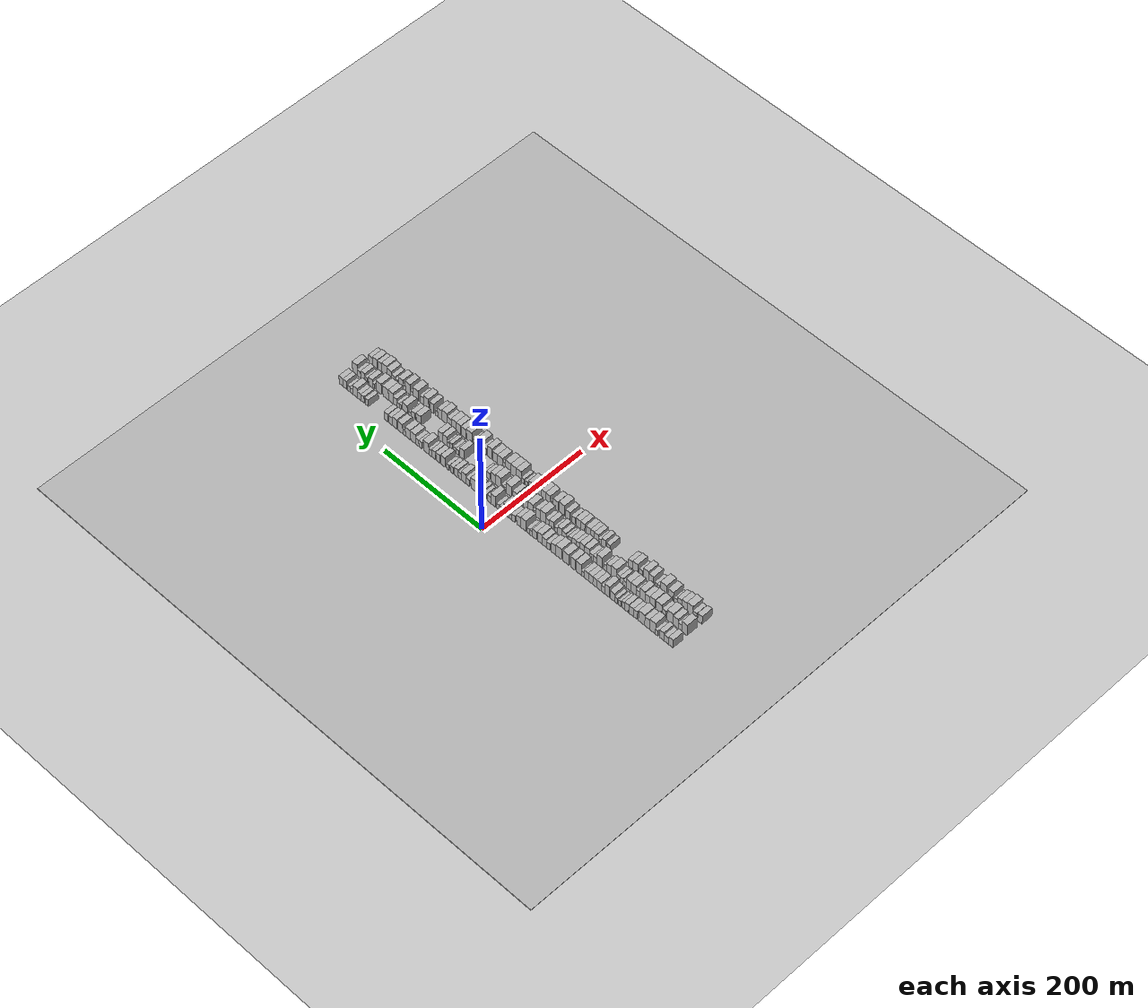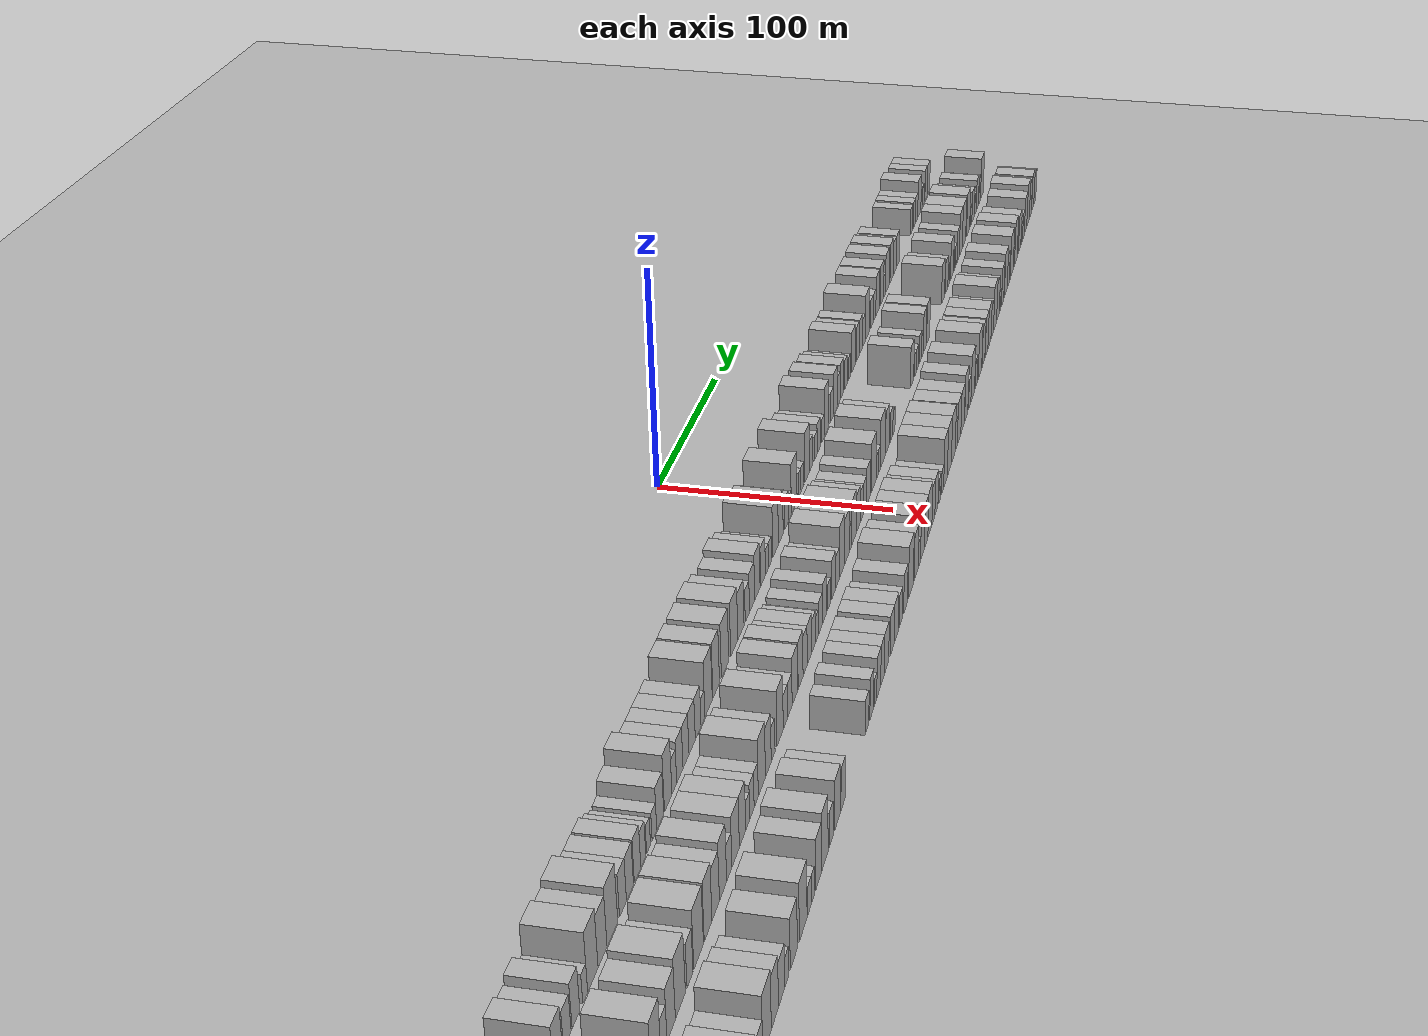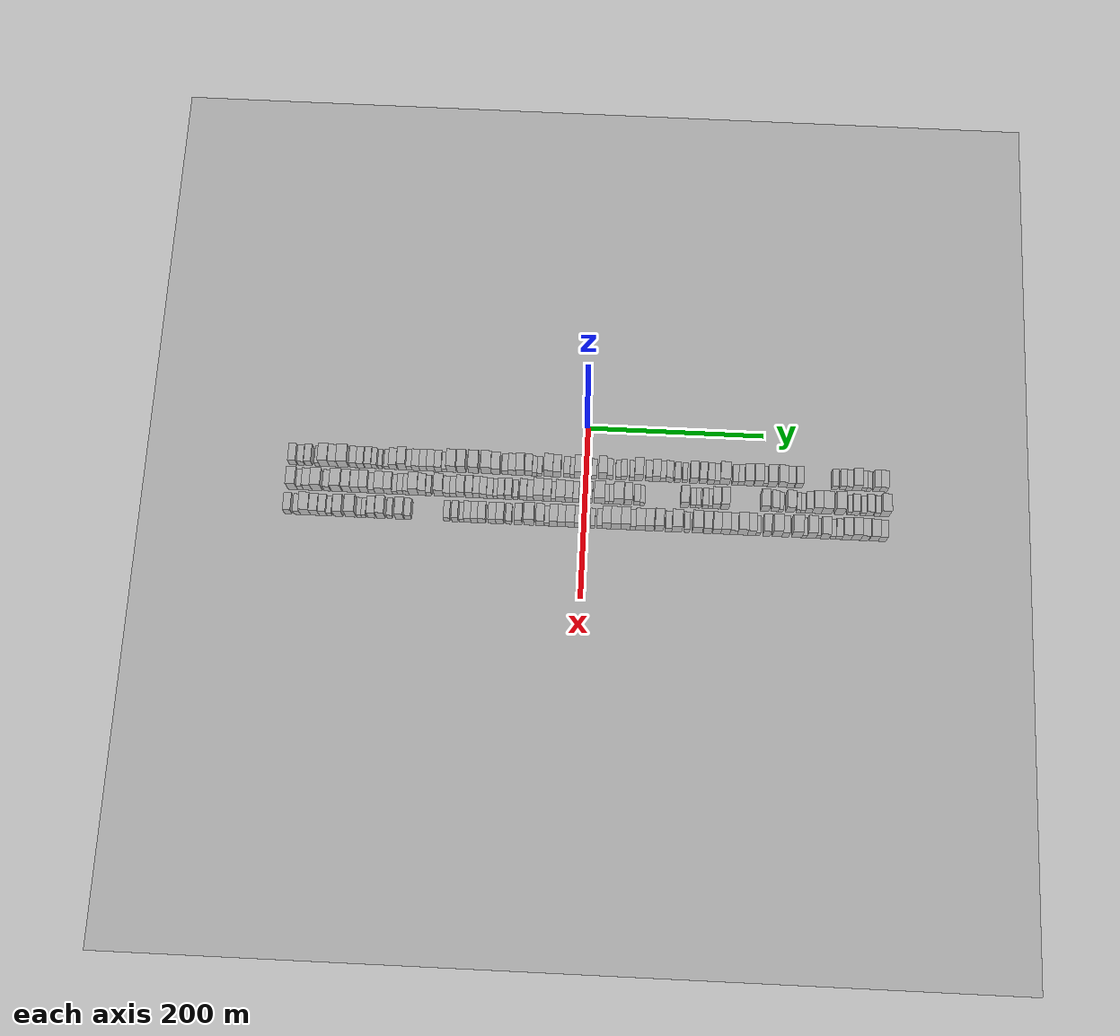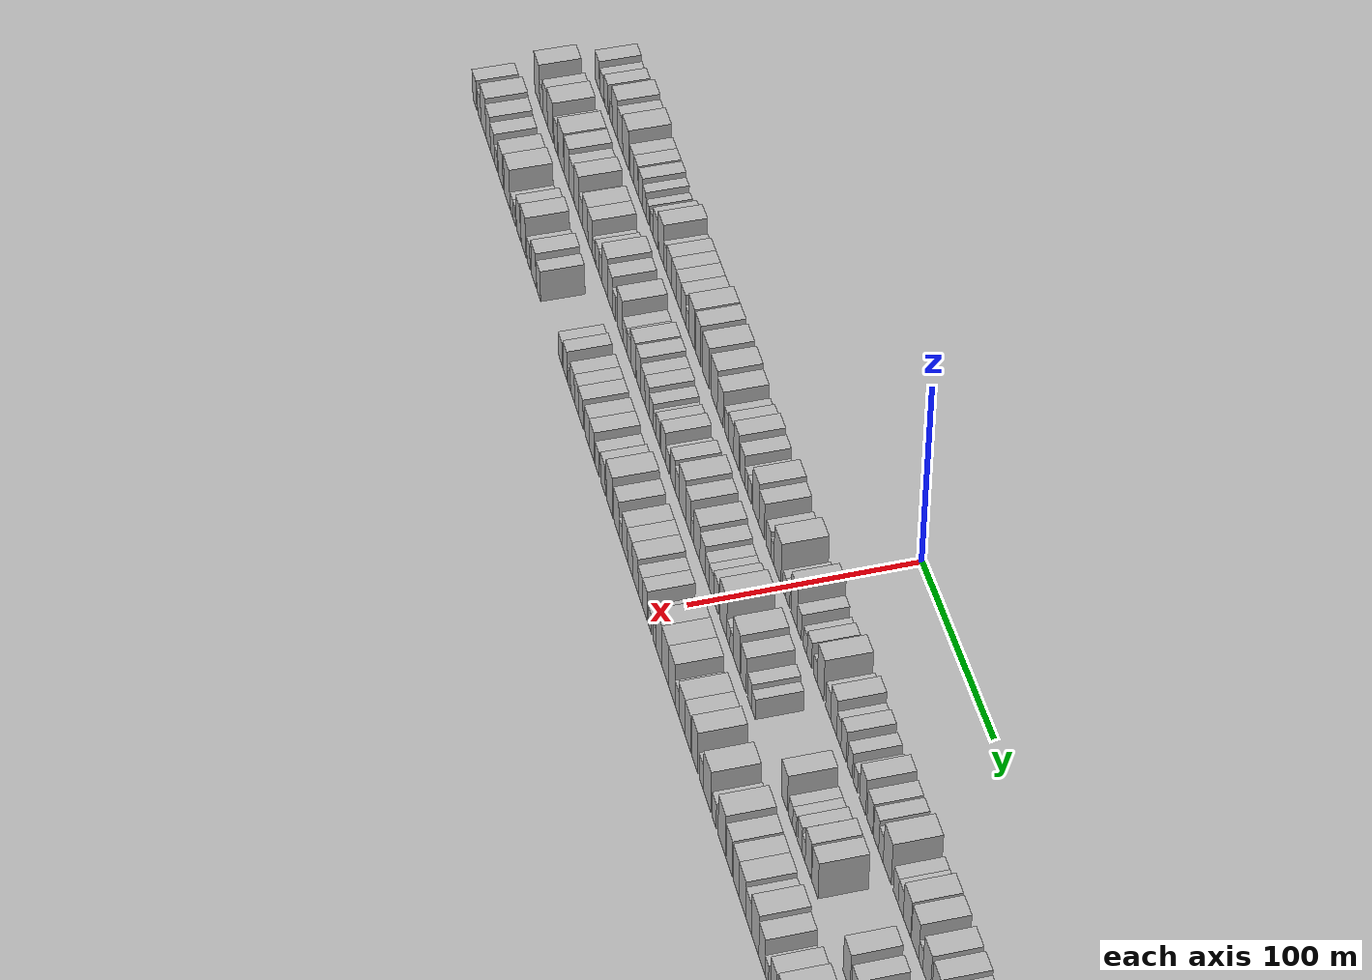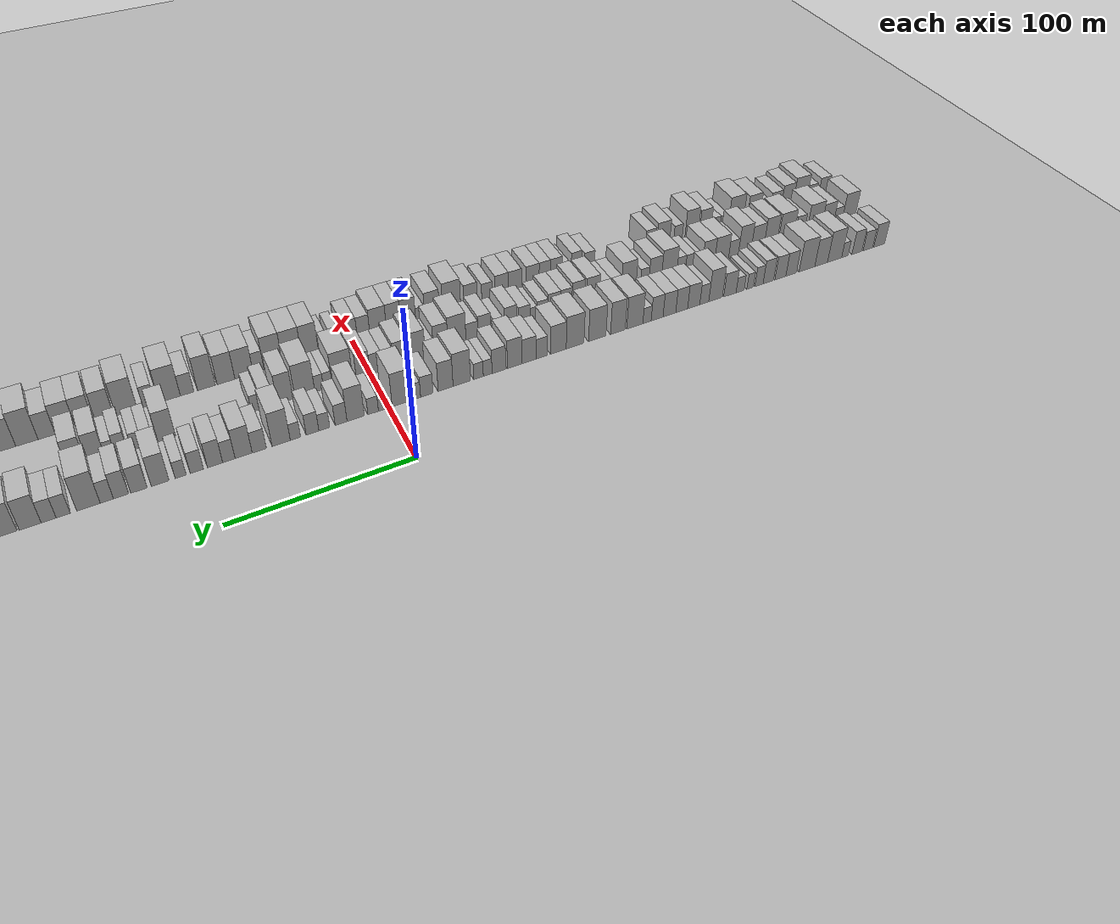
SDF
<?xml version="1.0" encoding="utf-8"?>

<sdf version="1.6">

   <world name="default">

      <gui fullscreen="0">

         <camera name="user_camera">

            <pose>-15 0 4.57585 0 0 0</pose>

            <view_controller>orbit</view_controller>

         </camera>

      </gui>

      <scene>

         <sky>

           <clouds>

             <speed>12</speed>

           </clouds>

         </sky>

         <ambient>0.4 0.4 0.4 1</ambient>

         <background>0.7 0.7 0.7 1</background>

         <shadows>1</shadows>

      </scene>

      <gravity>0 0 -9.8066</gravity>

      <magnetic_field>6e-06 2.3e-05 -4.2e-05</magnetic_field>

      <physics default="0" name="default_physics" type="ode">

         <ode>

            <solver>

               <type>quick</type>

               <iters>10</iters>

               <sor>1.0</sor>

               <use_dynamic_moi_rescaling>0</use_dynamic_moi_rescaling>

            </solver>

            <constraints>

               <cfm>0</cfm>

               <erp>0.2</erp>

               <contact_max_correcting_vel>100</contact_max_correcting_vel>

               <contact_surface_layer>0.001</contact_surface_layer>

            </constraints>

         </ode>

         <max_step_size>0.004</max_step_size>

         <real_time_factor>1</real_time_factor>

         <real_time_update_rate>250</real_time_update_rate>

      </physics>

      <light name="sun" type="directional">

         <cast_shadows>1</cast_shadows>

         <pose>0 0 10 0 0 0</pose>

         <diffuse>0.8 0.8 0.8 1</diffuse>

         <specular>0.2 0.2 0.2 1</specular>

         <attenuation>

            <range>1000</range>

            <constant>0.9</constant>

            <linear>0.01</linear>

            <quadratic>0.001</quadratic>

         </attenuation>

         <direction>-0.5 0.1 -0.9</direction>

      </light>

      <include>

         <name>ground_plane_1</name>

         <uri>model://HANNAS_ground_plane</uri>

         <pose>0 0 0  0 0 0</pose>

      </include>

      <include>

         <name>ground_plane_2</name>

         <uri>model://HANNAS_ground_plane</uri>

         <pose>100 0 0  0 0 0</pose>

      </include>

      <model name="building_1">

         <static>1</static>

         <pose frame="">50.0000 -331.6397 0 0.000000 0.000000 0.000000</pose>

         <link name="link">

            <pose frame="">0 0 9.00 0 0 0</pose>

            <collision name="collision">

               <geometry>

                  <box>

                     <size>20.0000 8.7205 18.0000</size>

                  </box>

               </geometry>

               <max_contacts>10</max_contacts>

               <surface>

                  <contact>

                     <ode/>

                  </contact>

                  <bounce/>

                  <friction>

                     <torsional>

                        <ode/>

                     </torsional>

                     <ode/>

                  </friction>

               </surface>

            </collision>

            <visual name="visual">

               <cast_shadows>0</cast_shadows>

               <geometry>

                  <box>

                     <size>20.0000 8.7205 18.0000</size>

                  </box>

               </geometry>

               <material>

                  <script>

                     <uri>model://HANNAS_wall/materials/scripts</uri>

                     <uri>model://HANNAS_wall/materials/textures</uri>

                     <name>vrc/HANNAS_wall</name>

                  </script>

               </material>

            </visual>

            <self_collide>0</self_collide>

            <enable_wind>0</enable_wind>

            <kinematic>0</kinematic>

         </link>

      </model>

      <model name="building_2">

         <static>1</static>

         <pose frame="">50.0000 -322.5313 0 0.000000 0.000000 0.000000</pose>

         <link name="link">

            <pose frame="">0 0 7.50 0 0 0</pose>

            <collision name="collision">

               <geometry>

                  <box>

                     <size>20.0000 7.4964 15.0000</size>

                  </box>

               </geometry>

               <max_contacts>10</max_contacts>

               <surface>

                  <contact>

                     <ode/>

                  </contact>

                  <bounce/>

                  <friction>

                     <torsional>

                        <ode/>

                     </torsional>

                     <ode/>

                  </friction>

               </surface>

            </collision>

            <visual name="visual">

               <cast_shadows>0</cast_shadows>

               <geometry>

                  <box>

                     <size>20.0000 7.4964 15.0000</size>

                  </box>

               </geometry>

               <material>

                  <script>

                     <uri>model://HANNAS_wall/materials/scripts</uri>

                     <uri>model://HANNAS_wall/materials/textures</uri>

                     <name>vrc/HANNAS_wall</name>

                  </script>

               </material>

            </visual>

            <self_collide>0</self_collide>

            <enable_wind>0</enable_wind>

            <kinematic>0</kinematic>

         </link>

      </model>

      <model name="building_3">

         <static>1</static>

         <pose frame="">50.0000 -313.8501 0 0.000000 0.000000 0.000000</pose>

         <link name="link">

            <pose frame="">0 0 9.00 0 0 0</pose>

            <collision name="collision">

               <geometry>

                  <box>

                     <size>20.0000 7.8660 18.0000</size>

                  </box>

               </geometry>

               <max_contacts>10</max_contacts>

               <surface>

                  <contact>

                     <ode/>

                  </contact>

                  <bounce/>

                  <friction>

                     <torsional>

                        <ode/>

                     </torsional>

                     <ode/>

                  </friction>

               </surface>

            </collision>

            <visual name="visual">

               <cast_shadows>0</cast_shadows>

               <geometry>

                  <box>

                     <size>20.0000 7.8660 18.0000</size>

                  </box>

               </geometry>

               <material>

                  <script>

                     <uri>model://HANNAS_wall/materials/scripts</uri>

                     <uri>model://HANNAS_wall/materials/textures</uri>

                     <name>vrc/HANNAS_wall</name>

                  </script>

               </material>

            </visual>

            <self_collide>0</self_collide>

            <enable_wind>0</enable_wind>

            <kinematic>0</kinematic>

         </link>

      </model>

      <model name="building_4">

         <static>1</static>

         <pose frame="">50.0000 -304.3838 0 0.000000 0.000000 0.000000</pose>

         <link name="link">

            <pose frame="">0 0 6.00 0 0 0</pose>

            <collision name="collision">

               <geometry>

                  <box>

                     <size>20.0000 5.0666 12.0000</size>

                  </box>

               </geometry>

               <max_contacts>10</max_contacts>

               <surface>

                  <contact>

                     <ode/>

                  </contact>

                  <bounce/>

                  <friction>

                     <torsional>

                        <ode/>

                     </torsional>

                     <ode/>

                  </friction>

               </surface>

            </collision>

            <visual name="visual">

               <cast_shadows>0</cast_shadows>

               <geometry>

                  <box>

                     <size>20.0000 5.0666 12.0000</size>

                  </box>

               </geometry>

               <material>

                  <script>

                     <uri>model://HANNAS_wall/materials/scripts</uri>

                     <uri>model://HANNAS_wall/materials/textures</uri>

                     <name>vrc/HANNAS_wall</name>

                  </script>

               </material>

            </visual>

            <self_collide>0</self_collide>

            <enable_wind>0</enable_wind>

            <kinematic>0</kinematic>

         </link>

      </model>

      <model name="building_5">

         <static>1</static>

         <pose frame="">50.0000 -296.3426 0 0.000000 0.000000 0.000000</pose>

         <link name="link">

            <pose frame="">0 0 12.00 0 0 0</pose>

            <collision name="collision">

               <geometry>

                  <box>

                     <size>20.0000 11.0157 24.0000</size>

                  </box>

               </geometry>

               <max_contacts>10</max_contacts>

               <surface>

                  <contact>

                     <ode/>

                  </contact>

                  <bounce/>

                  <friction>

                     <torsional>

                        <ode/>

                     </torsional>

                     <ode/>

                  </friction>

               </surface>

            </collision>

            <visual name="visual">

               <cast_shadows>0</cast_shadows>

               <geometry>

                  <box>

                     <size>20.0000 11.0157 24.0000</size>

                  </box>

               </geometry>

               <material>

                  <script>

                     <uri>model://HANNAS_wall/materials/scripts</uri>

                     <uri>model://HANNAS_wall/materials/textures</uri>

                     <name>vrc/HANNAS_wall</name>

                  </script>

               </material>

            </visual>

            <self_collide>0</self_collide>

            <enable_wind>0</enable_wind>

            <kinematic>0</kinematic>

         </link>

      </model>

      <model name="building_6">

         <static>1</static>

         <pose frame="">50.0000 -285.9676 0 0.000000 0.000000 0.000000</pose>

         <link name="link">

            <pose frame="">0 0 10.50 0 0 0</pose>

            <collision name="collision">

               <geometry>

                  <box>

                     <size>20.0000 9.7342 21.0000</size>

                  </box>

               </geometry>

               <max_contacts>10</max_contacts>

               <surface>

                  <contact>

                     <ode/>

                  </contact>

                  <bounce/>

                  <friction>

                     <torsional>

                        <ode/>

                     </torsional>

                     <ode/>

                  </friction>

               </surface>

            </collision>

            <visual name="visual">

               <cast_shadows>0</cast_shadows>

               <geometry>

                  <box>

                     <size>20.0000 9.7342 21.0000</size>

                  </box>

               </geometry>

               <material>

                  <script>

                     <uri>model://HANNAS_wall/materials/scripts</uri>

                     <uri>model://HANNAS_wall/materials/textures</uri>

                     <name>vrc/HANNAS_wall</name>

                  </script>

               </material>

            </visual>

            <self_collide>0</self_collide>

            <enable_wind>0</enable_wind>

            <kinematic>0</kinematic>

         </link>

      </model>

      <model name="building_7">

         <static>1</static>

         <pose frame="">50.0000 -275.1267 0 0.000000 0.000000 0.000000</pose>

         <link name="link">

            <pose frame="">0 0 12.00 0 0 0</pose>

            <collision name="collision">

               <geometry>

                  <box>

                     <size>20.0000 11.9476 24.0000</size>

                  </box>

               </geometry>

               <max_contacts>10</max_contacts>

               <surface>

                  <contact>

                     <ode/>

                  </contact>

                  <bounce/>

                  <friction>

                     <torsional>

                        <ode/>

                     </torsional>

                     <ode/>

                  </friction>

               </surface>

            </collision>

            <visual name="visual">

               <cast_shadows>0</cast_shadows>

               <geometry>

                  <box>

                     <size>20.0000 11.9476 24.0000</size>

                  </box>

               </geometry>

               <material>

                  <script>

                     <uri>model://HANNAS_wall/materials/scripts</uri>

                     <uri>model://HANNAS_wall/materials/textures</uri>

                     <name>vrc/HANNAS_wall</name>

                  </script>

               </material>

            </visual>

            <self_collide>0</self_collide>

            <enable_wind>0</enable_wind>

            <kinematic>0</kinematic>

         </link>

      </model>

      <model name="building_8">

         <static>1</static>

         <pose frame="">50.0000 -263.1664 0 0.000000 0.000000 0.000000</pose>

         <link name="link">

            <pose frame="">0 0 9.00 0 0 0</pose>

            <collision name="collision">

               <geometry>

                  <box>

                     <size>20.0000 7.9730 18.0000</size>

                  </box>

               </geometry>

               <max_contacts>10</max_contacts>

               <surface>

                  <contact>

                     <ode/>

                  </contact>

                  <bounce/>

                  <friction>

                     <torsional>

                        <ode/>

                     </torsional>

                     <ode/>

                  </friction>

               </surface>

            </collision>

            <visual name="visual">

               <cast_shadows>0</cast_shadows>

               <geometry>

                  <box>

                     <size>20.0000 7.9730 18.0000</size>

                  </box>

               </geometry>

               <material>

                  <script>

                     <uri>model://HANNAS_wall/materials/scripts</uri>

                     <uri>model://HANNAS_wall/materials/textures</uri>

                     <name>vrc/HANNAS_wall</name>

                  </script>

               </material>

            </visual>

            <self_collide>0</self_collide>

            <enable_wind>0</enable_wind>

            <kinematic>0</kinematic>

         </link>

      </model>

      <model name="building_9">

         <static>1</static>

         <pose frame="">50.0000 -255.0837 0 0.000000 0.000000 0.000000</pose>

         <link name="link">

            <pose frame="">0 0 9.00 0 0 0</pose>

            <collision name="collision">

               <geometry>

                  <box>

                     <size>20.0000 8.1924 18.0000</size>

                  </box>

               </geometry>

               <max_contacts>10</max_contacts>

               <surface>

                  <contact>

                     <ode/>

                  </contact>

                  <bounce/>

                  <friction>

                     <torsional>

                        <ode/>

                     </torsional>

                     <ode/>

                  </friction>

               </surface>

            </collision>

            <visual name="visual">

               <cast_shadows>0</cast_shadows>

               <geometry>

                  <box>

                     <size>20.0000 8.1924 18.0000</size>

                  </box>

               </geometry>

               <material>

                  <script>

                     <uri>model://HANNAS_wall/materials/scripts</uri>

                     <uri>model://HANNAS_wall/materials/textures</uri>

                     <name>vrc/HANNAS_wall</name>

                  </script>

               </material>

            </visual>

            <self_collide>0</self_collide>

            <enable_wind>0</enable_wind>

            <kinematic>0</kinematic>

         </link>

      </model>

      <model name="building_10">

         <static>1</static>

         <pose frame="">50.0000 -246.1191 0 0.000000 0.000000 0.000000</pose>

         <link name="link">

            <pose frame="">0 0 9.00 0 0 0</pose>

            <collision name="collision">

               <geometry>

                  <box>

                     <size>20.0000 7.7369 18.0000</size>

                  </box>

               </geometry>

               <max_contacts>10</max_contacts>

               <surface>

                  <contact>

                     <ode/>

                  </contact>

                  <bounce/>

                  <friction>

                     <torsional>

                        <ode/>

                     </torsional>

                     <ode/>

                  </friction>

               </surface>

            </collision>

            <visual name="visual">

               <cast_shadows>0</cast_shadows>

               <geometry>

                  <box>

                     <size>20.0000 7.7369 18.0000</size>

                  </box>

               </geometry>

               <material>

                  <script>

                     <uri>model://HANNAS_wall/materials/scripts</uri>

                     <uri>model://HANNAS_wall/materials/textures</uri>

                     <name>vrc/HANNAS_wall</name>

                  </script>

               </material>

            </visual>

            <self_collide>0</self_collide>

            <enable_wind>0</enable_wind>

            <kinematic>0</kinematic>

         </link>

      </model>

      <model name="building_11">

         <static>1</static>

         <pose frame="">50.0000 -239.2232 0 0.000000 0.000000 0.000000</pose>

         <link name="link">

            <pose frame="">0 0 7.50 0 0 0</pose>

            <collision name="collision">

               <geometry>

                  <box>

                     <size>20.0000 6.0549 15.0000</size>

                  </box>

               </geometry>

               <max_contacts>10</max_contacts>

               <surface>

                  <contact>

                     <ode/>

                  </contact>

                  <bounce/>

                  <friction>

                     <torsional>

                        <ode/>

                     </torsional>

                     <ode/>

                  </friction>

               </surface>

            </collision>

            <visual name="visual">

               <cast_shadows>0</cast_shadows>

               <geometry>

                  <box>

                     <size>20.0000 6.0549 15.0000</size>

                  </box>

               </geometry>

               <material>

                  <script>

                     <uri>model://HANNAS_wall/materials/scripts</uri>

                     <uri>model://HANNAS_wall/materials/textures</uri>

                     <name>vrc/HANNAS_wall</name>

                  </script>

               </material>

            </visual>

            <self_collide>0</self_collide>

            <enable_wind>0</enable_wind>

            <kinematic>0</kinematic>

         </link>

      </model>

      <model name="building_12">

         <static>1</static>

         <pose frame="">50.0000 -232.7923 0 0.000000 0.000000 0.000000</pose>

         <link name="link">

            <pose frame="">0 0 6.00 0 0 0</pose>

            <collision name="collision">

               <geometry>

                  <box>

                     <size>20.0000 4.8070 12.0000</size>

                  </box>

               </geometry>

               <max_contacts>10</max_contacts>

               <surface>

                  <contact>

                     <ode/>

                  </contact>

                  <bounce/>

                  <friction>

                     <torsional>

                        <ode/>

                     </torsional>

                     <ode/>

                  </friction>

               </surface>

            </collision>

            <visual name="visual">

               <cast_shadows>0</cast_shadows>

               <geometry>

                  <box>

                     <size>20.0000 4.8070 12.0000</size>

                  </box>

               </geometry>

               <material>

                  <script>

                     <uri>model://HANNAS_wall/materials/scripts</uri>

                     <uri>model://HANNAS_wall/materials/textures</uri>

                     <name>vrc/HANNAS_wall</name>

                  </script>

               </material>

            </visual>

            <self_collide>0</self_collide>

            <enable_wind>0</enable_wind>

            <kinematic>0</kinematic>

         </link>

      </model>

      <model name="building_13">

         <static>1</static>

         <pose frame="">50.0000 -225.4865 0 0.000000 0.000000 0.000000</pose>

         <link name="link">

            <pose frame="">0 0 6.00 0 0 0</pose>

            <collision name="collision">

               <geometry>

                  <box>

                     <size>20.0000 5.8045 12.0000</size>

                  </box>

               </geometry>

               <max_contacts>10</max_contacts>

               <surface>

                  <contact>

                     <ode/>

                  </contact>

                  <bounce/>

                  <friction>

                     <torsional>

                        <ode/>

                     </torsional>

                     <ode/>

                  </friction>

               </surface>

            </collision>

            <visual name="visual">

               <cast_shadows>0</cast_shadows>

               <geometry>

                  <box>

                     <size>20.0000 5.8045 12.0000</size>

                  </box>

               </geometry>

               <material>

                  <script>

                     <uri>model://HANNAS_wall/materials/scripts</uri>

                     <uri>model://HANNAS_wall/materials/textures</uri>

                     <name>vrc/HANNAS_wall</name>

                  </script>

               </material>

            </visual>

            <self_collide>0</self_collide>

            <enable_wind>0</enable_wind>

            <kinematic>0</kinematic>

         </link>

      </model>

      <model name="building_14">

         <static>1</static>

         <pose frame="">50.0000 -218.1348 0 0.000000 0.000000 0.000000</pose>

         <link name="link">

            <pose frame="">0 0 9.00 0 0 0</pose>

            <collision name="collision">

               <geometry>

                  <box>

                     <size>20.0000 8.8989 18.0000</size>

                  </box>

               </geometry>

               <max_contacts>10</max_contacts>

               <surface>

                  <contact>

                     <ode/>

                  </contact>

                  <bounce/>

                  <friction>

                     <torsional>

                        <ode/>

                     </torsional>

                     <ode/>

                  </friction>

               </surface>

            </collision>

            <visual name="visual">

               <cast_shadows>0</cast_shadows>

               <geometry>

                  <box>

                     <size>20.0000 8.8989 18.0000</size>

                  </box>

               </geometry>

               <material>

                  <script>

                     <uri>model://HANNAS_wall/materials/scripts</uri>

                     <uri>model://HANNAS_wall/materials/textures</uri>

                     <name>vrc/HANNAS_wall</name>

                  </script>

               </material>

            </visual>

            <self_collide>0</self_collide>

            <enable_wind>0</enable_wind>

            <kinematic>0</kinematic>

         </link>

      </model>

      <model name="building_15">

         <static>1</static>

         <pose frame="">50.0000 -207.8480 0 0.000000 0.000000 0.000000</pose>

         <link name="link">

            <pose frame="">0 0 12.00 0 0 0</pose>

            <collision name="collision">

               <geometry>

                  <box>

                     <size>20.0000 9.6747 24.0000</size>

                  </box>

               </geometry>

               <max_contacts>10</max_contacts>

               <surface>

                  <contact>

                     <ode/>

                  </contact>

                  <bounce/>

                  <friction>

                     <torsional>

                        <ode/>

                     </torsional>

                     <ode/>

                  </friction>

               </surface>

            </collision>

            <visual name="visual">

               <cast_shadows>0</cast_shadows>

               <geometry>

                  <box>

                     <size>20.0000 9.6747 24.0000</size>

                  </box>

               </geometry>

               <material>

                  <script>

                     <uri>model://HANNAS_wall/materials/scripts</uri>

                     <uri>model://HANNAS_wall/materials/textures</uri>

                     <name>vrc/HANNAS_wall</name>

                  </script>

               </material>

            </visual>

            <self_collide>0</self_collide>

            <enable_wind>0</enable_wind>

            <kinematic>0</kinematic>

         </link>

      </model>

      <model name="building_16">

         <static>1</static>

         <pose frame="">50.0000 -199.8449 0 0.000000 0.000000 0.000000</pose>

         <link name="link">

            <pose frame="">0 0 7.50 0 0 0</pose>

            <collision name="collision">

               <geometry>

                  <box>

                     <size>20.0000 6.3316 15.0000</size>

                  </box>

               </geometry>

               <max_contacts>10</max_contacts>

               <surface>

                  <contact>

                     <ode/>

                  </contact>

                  <bounce/>

                  <friction>

                     <torsional>

                        <ode/>

                     </torsional>

                     <ode/>

                  </friction>

               </surface>

            </collision>

            <visual name="visual">

               <cast_shadows>0</cast_shadows>

               <geometry>

                  <box>

                     <size>20.0000 6.3316 15.0000</size>

                  </box>

               </geometry>

               <material>

                  <script>

                     <uri>model://HANNAS_wall/materials/scripts</uri>

                     <uri>model://HANNAS_wall/materials/textures</uri>

                     <name>vrc/HANNAS_wall</name>

                  </script>

               </material>

            </visual>

            <self_collide>0</self_collide>

            <enable_wind>0</enable_wind>

            <kinematic>0</kinematic>

         </link>

      </model>

      <model name="building_17">

         <static>1</static>

         <pose frame="">50.0000 -192.4107 0 0.000000 0.000000 0.000000</pose>

         <link name="link">

            <pose frame="">0 0 9.00 0 0 0</pose>

            <collision name="collision">

               <geometry>

                  <box>

                     <size>20.0000 8.5367 18.0000</size>

                  </box>

               </geometry>

               <max_contacts>10</max_contacts>

               <surface>

                  <contact>

                     <ode/>

                  </contact>

                  <bounce/>

                  <friction>

                     <torsional>

                        <ode/>

                     </torsional>

                     <ode/>

                  </friction>

               </surface>

            </collision>

            <visual name="visual">

               <cast_shadows>0</cast_shadows>

               <geometry>

                  <box>

                     <size>20.0000 8.5367 18.0000</size>

                  </box>

               </geometry>

               <material>

                  <script>

                     <uri>model://HANNAS_wall/materials/scripts</uri>

                     <uri>model://HANNAS_wall/materials/textures</uri>

                     <name>vrc/HANNAS_wall</name>

                  </script>

               </material>

            </visual>

            <self_collide>0</self_collide>

            <enable_wind>0</enable_wind>

            <kinematic>0</kinematic>

         </link>

      </model>

      <model name="building_18">

         <static>1</static>

         <pose frame="">50.0000 -184.0415 0 0.000000 0.000000 0.000000</pose>

         <link name="link">

            <pose frame="">0 0 9.00 0 0 0</pose>

            <collision name="collision">

               <geometry>

                  <box>

                     <size>20.0000 8.2016 18.0000</size>

                  </box>

               </geometry>

               <max_contacts>10</max_contacts>

               <surface>

                  <contact>

                     <ode/>

                  </contact>

                  <bounce/>

                  <friction>

                     <torsional>

                        <ode/>

                     </torsional>

                     <ode/>

                  </friction>

               </surface>

            </collision>

            <visual name="visual">

               <cast_shadows>0</cast_shadows>

               <geometry>

                  <box>

                     <size>20.0000 8.2016 18.0000</size>

                  </box>

               </geometry>

               <material>

                  <script>

                     <uri>model://HANNAS_wall/materials/scripts</uri>

                     <uri>model://HANNAS_wall/materials/textures</uri>

                     <name>vrc/HANNAS_wall</name>

                  </script>

               </material>

            </visual>

            <self_collide>0</self_collide>

            <enable_wind>0</enable_wind>

            <kinematic>0</kinematic>

         </link>

      </model>

      <model name="building_19">

         <static>1</static>

         <pose frame="">50.0000 -175.5516 0 0.000000 0.000000 0.000000</pose>

         <link name="link">

            <pose frame="">0 0 9.00 0 0 0</pose>

            <collision name="collision">

               <geometry>

                  <box>

                     <size>20.0000 8.7783 18.0000</size>

                  </box>

               </geometry>

               <max_contacts>10</max_contacts>

               <surface>

                  <contact>

                     <ode/>

                  </contact>

                  <bounce/>

                  <friction>

                     <torsional>

                        <ode/>

                     </torsional>

                     <ode/>

                  </friction>

               </surface>

            </collision>

            <visual name="visual">

               <cast_shadows>0</cast_shadows>

               <geometry>

                  <box>

                     <size>20.0000 8.7783 18.0000</size>

                  </box>

               </geometry>

               <material>

                  <script>

                     <uri>model://HANNAS_wall/materials/scripts</uri>

                     <uri>model://HANNAS_wall/materials/textures</uri>

                     <name>vrc/HANNAS_wall</name>

                  </script>

               </material>

            </visual>

            <self_collide>0</self_collide>

            <enable_wind>0</enable_wind>

            <kinematic>0</kinematic>

         </link>

      </model>

      <model name="building_20">

         <static>1</static>

         <pose frame="">50.0000 -167.0960 0 0.000000 0.000000 0.000000</pose>

         <link name="link">

            <pose frame="">0 0 9.00 0 0 0</pose>

            <collision name="collision">

               <geometry>

                  <box>

                     <size>20.0000 8.1327 18.0000</size>

                  </box>

               </geometry>

               <max_contacts>10</max_contacts>

               <surface>

                  <contact>

                     <ode/>

                  </contact>

                  <bounce/>

                  <friction>

                     <torsional>

                        <ode/>

                     </torsional>

                     <ode/>

                  </friction>

               </surface>

            </collision>

            <visual name="visual">

               <cast_shadows>0</cast_shadows>

               <geometry>

                  <box>

                     <size>20.0000 8.1327 18.0000</size>

                  </box>

               </geometry>

               <material>

                  <script>

                     <uri>model://HANNAS_wall/materials/scripts</uri>

                     <uri>model://HANNAS_wall/materials/textures</uri>

                     <name>vrc/HANNAS_wall</name>

                  </script>

               </material>

            </visual>

            <self_collide>0</self_collide>

            <enable_wind>0</enable_wind>

            <kinematic>0</kinematic>

         </link>

      </model>

      <model name="building_21">

         <static>1</static>

         <pose frame="">50.0000 -160.2294 0 0.000000 0.000000 0.000000</pose>

         <link name="link">

            <pose frame="">0 0 6.00 0 0 0</pose>

            <collision name="collision">

               <geometry>

                  <box>

                     <size>20.0000 5.6006 12.0000</size>

                  </box>

               </geometry>

               <max_contacts>10</max_contacts>

               <surface>

                  <contact>

                     <ode/>

                  </contact>

                  <bounce/>

                  <friction>

                     <torsional>

                        <ode/>

                     </torsional>

                     <ode/>

                  </friction>

               </surface>

            </collision>

            <visual name="visual">

               <cast_shadows>0</cast_shadows>

               <geometry>

                  <box>

                     <size>20.0000 5.6006 12.0000</size>

                  </box>

               </geometry>

               <material>

                  <script>

                     <uri>model://HANNAS_wall/materials/scripts</uri>

                     <uri>model://HANNAS_wall/materials/textures</uri>

                     <name>vrc/HANNAS_wall</name>

                  </script>

               </material>

            </visual>

            <self_collide>0</self_collide>

            <enable_wind>0</enable_wind>

            <kinematic>0</kinematic>

         </link>

      </model>

      <model name="building_22">

         <static>1</static>

         <pose frame="">50.0000 -151.9978 0 0.000000 0.000000 0.000000</pose>

         <link name="link">

            <pose frame="">0 0 12.00 0 0 0</pose>

            <collision name="collision">

               <geometry>

                  <box>

                     <size>20.0000 10.8625 24.0000</size>

                  </box>

               </geometry>

               <max_contacts>10</max_contacts>

               <surface>

                  <contact>

                     <ode/>

                  </contact>

                  <bounce/>

                  <friction>

                     <torsional>

                        <ode/>

                     </torsional>

                     <ode/>

                  </friction>

               </surface>

            </collision>

            <visual name="visual">

               <cast_shadows>0</cast_shadows>

               <geometry>

                  <box>

                     <size>20.0000 10.8625 24.0000</size>

                  </box>

               </geometry>

               <material>

                  <script>

                     <uri>model://HANNAS_wall/materials/scripts</uri>

                     <uri>model://HANNAS_wall/materials/textures</uri>

                     <name>vrc/HANNAS_wall</name>

                  </script>

               </material>

            </visual>

            <self_collide>0</self_collide>

            <enable_wind>0</enable_wind>

            <kinematic>0</kinematic>

         </link>

      </model>

      <model name="building_23">

         <static>1</static>

         <pose frame="">50.0000 -140.6740 0 0.000000 0.000000 0.000000</pose>

         <link name="link">

            <pose frame="">0 0 12.00 0 0 0</pose>

            <collision name="collision">

               <geometry>

                  <box>

                     <size>20.0000 9.7850 24.0000</size>

                  </box>

               </geometry>

               <max_contacts>10</max_contacts>

               <surface>

                  <contact>

                     <ode/>

                  </contact>

                  <bounce/>

                  <friction>

                     <torsional>

                        <ode/>

                     </torsional>

                     <ode/>

                  </friction>

               </surface>

            </collision>

            <visual name="visual">

               <cast_shadows>0</cast_shadows>

               <geometry>

                  <box>

                     <size>20.0000 9.7850 24.0000</size>

                  </box>

               </geometry>

               <material>

                  <script>

                     <uri>model://HANNAS_wall/materials/scripts</uri>

                     <uri>model://HANNAS_wall/materials/textures</uri>

                     <name>vrc/HANNAS_wall</name>

                  </script>

               </material>

            </visual>

            <self_collide>0</self_collide>

            <enable_wind>0</enable_wind>

            <kinematic>0</kinematic>

         </link>

      </model>

      <model name="building_24">

         <static>1</static>

         <pose frame="">50.0000 -127.0697 0 0.000000 0.000000 0.000000</pose>

         <link name="link">

            <pose frame="">0 0 12.00 0 0 0</pose>

            <collision name="collision">

               <geometry>

                  <box>

                     <size>20.0000 11.4236 24.0000</size>

                  </box>

               </geometry>

               <max_contacts>10</max_contacts>

               <surface>

                  <contact>

                     <ode/>

                  </contact>

                  <bounce/>

                  <friction>

                     <torsional>

                        <ode/>

                     </torsional>

                     <ode/>

                  </friction>

               </surface>

            </collision>

            <visual name="visual">

               <cast_shadows>0</cast_shadows>

               <geometry>

                  <box>

                     <size>20.0000 11.4236 24.0000</size>

                  </box>

               </geometry>

               <material>

                  <script>

                     <uri>model://HANNAS_wall/materials/scripts</uri>

                     <uri>model://HANNAS_wall/materials/textures</uri>

                     <name>vrc/HANNAS_wall</name>

                  </script>

               </material>

            </visual>

            <self_collide>0</self_collide>

            <enable_wind>0</enable_wind>

            <kinematic>0</kinematic>

         </link>

      </model>

      <model name="building_25">

         <static>1</static>

         <pose frame="">50.0000 -112.6428 0 0.000000 0.000000 0.000000</pose>

         <link name="link">

            <pose frame="">0 0 12.00 0 0 0</pose>

            <collision name="collision">

               <geometry>

                  <box>

                     <size>20.0000 11.4302 24.0000</size>

                  </box>

               </geometry>

               <max_contacts>10</max_contacts>

               <surface>

                  <contact>

                     <ode/>

                  </contact>

                  <bounce/>

                  <friction>

                     <torsional>

                        <ode/>

                     </torsional>

                     <ode/>

                  </friction>

               </surface>

            </collision>

            <visual name="visual">

               <cast_shadows>0</cast_shadows>

               <geometry>

                  <box>

                     <size>20.0000 11.4302 24.0000</size>

                  </box>

               </geometry>

               <material>

                  <script>

                     <uri>model://HANNAS_wall/materials/scripts</uri>

                     <uri>model://HANNAS_wall/materials/textures</uri>

                     <name>vrc/HANNAS_wall</name>

                  </script>

               </material>

            </visual>

            <self_collide>0</self_collide>

            <enable_wind>0</enable_wind>

            <kinematic>0</kinematic>

         </link>

      </model>

      <model name="building_26">

         <static>1</static>

         <pose frame="">50.0000 -101.9458 0 0.000000 0.000000 0.000000</pose>

         <link name="link">

            <pose frame="">0 0 10.50 0 0 0</pose>

            <collision name="collision">

               <geometry>

                  <box>

                     <size>20.0000 9.9638 21.0000</size>

                  </box>

               </geometry>

               <max_contacts>10</max_contacts>

               <surface>

                  <contact>

                     <ode/>

                  </contact>

                  <bounce/>

                  <friction>

                     <torsional>

                        <ode/>

                     </torsional>

                     <ode/>

                  </friction>

               </surface>

            </collision>

            <visual name="visual">

               <cast_shadows>0</cast_shadows>

               <geometry>

                  <box>

                     <size>20.0000 9.9638 21.0000</size>

                  </box>

               </geometry>

               <material>

                  <script>

                     <uri>model://HANNAS_wall/materials/scripts</uri>

                     <uri>model://HANNAS_wall/materials/textures</uri>

                     <name>vrc/HANNAS_wall</name>

                  </script>

               </material>

            </visual>

            <self_collide>0</self_collide>

            <enable_wind>0</enable_wind>

            <kinematic>0</kinematic>

         </link>

      </model>

      <model name="building_27">

         <static>1</static>

         <pose frame="">50.0000 -91.4111 0 0.000000 0.000000 0.000000</pose>

         <link name="link">

            <pose frame="">0 0 7.50 0 0 0</pose>

            <collision name="collision">

               <geometry>

                  <box>

                     <size>20.0000 7.1054 15.0000</size>

                  </box>

               </geometry>

               <max_contacts>10</max_contacts>

               <surface>

                  <contact>

                     <ode/>

                  </contact>

                  <bounce/>

                  <friction>

                     <torsional>

                        <ode/>

                     </torsional>

                     <ode/>

                  </friction>

               </surface>

            </collision>

            <visual name="visual">

               <cast_shadows>0</cast_shadows>

               <geometry>

                  <box>

                     <size>20.0000 7.1054 15.0000</size>

                  </box>

               </geometry>

               <material>

                  <script>

                     <uri>model://HANNAS_wall/materials/scripts</uri>

                     <uri>model://HANNAS_wall/materials/textures</uri>

                     <name>vrc/HANNAS_wall</name>

                  </script>

               </material>

            </visual>

            <self_collide>0</self_collide>

            <enable_wind>0</enable_wind>

            <kinematic>0</kinematic>

         </link>

      </model>

      <model name="building_28">

         <static>1</static>

         <pose frame="">50.0000 -83.4727 0 0.000000 0.000000 0.000000</pose>

         <link name="link">

            <pose frame="">0 0 9.00 0 0 0</pose>

            <collision name="collision">

               <geometry>

                  <box>

                     <size>20.0000 8.7715 18.0000</size>

                  </box>

               </geometry>

               <max_contacts>10</max_contacts>

               <surface>

                  <contact>

                     <ode/>

                  </contact>

                  <bounce/>

                  <friction>

                     <torsional>

                        <ode/>

                     </torsional>

                     <ode/>

                  </friction>

               </surface>

            </collision>

            <visual name="visual">

               <cast_shadows>0</cast_shadows>

               <geometry>

                  <box>

                     <size>20.0000 8.7715 18.0000</size>

                  </box>

               </geometry>

               <material>

                  <script>

                     <uri>model://HANNAS_wall/materials/scripts</uri>

                     <uri>model://HANNAS_wall/materials/textures</uri>

                     <name>vrc/HANNAS_wall</name>

                  </script>

               </material>

            </visual>

            <self_collide>0</self_collide>

            <enable_wind>0</enable_wind>

            <kinematic>0</kinematic>

         </link>

      </model>

      <model name="building_29">

         <static>1</static>

         <pose frame="">50.0000 -74.4863 0 0.000000 0.000000 0.000000</pose>

         <link name="link">

            <pose frame="">0 0 10.50 0 0 0</pose>

            <collision name="collision">

               <geometry>

                  <box>

                     <size>20.0000 9.2012 21.0000</size>

                  </box>

               </geometry>

               <max_contacts>10</max_contacts>

               <surface>

                  <contact>

                     <ode/>

                  </contact>

                  <bounce/>

                  <friction>

                     <torsional>

                        <ode/>

                     </torsional>

                     <ode/>

                  </friction>

               </surface>

            </collision>

            <visual name="visual">

               <cast_shadows>0</cast_shadows>

               <geometry>

                  <box>

                     <size>20.0000 9.2012 21.0000</size>

                  </box>

               </geometry>

               <material>

                  <script>

                     <uri>model://HANNAS_wall/materials/scripts</uri>

                     <uri>model://HANNAS_wall/materials/textures</uri>

                     <name>vrc/HANNAS_wall</name>

                  </script>

               </material>

            </visual>

            <self_collide>0</self_collide>

            <enable_wind>0</enable_wind>

            <kinematic>0</kinematic>

         </link>

      </model>

      <model name="building_30">

         <static>1</static>

         <pose frame="">50.0000 -64.7141 0 0.000000 0.000000 0.000000</pose>

         <link name="link">

            <pose frame="">0 0 9.00 0 0 0</pose>

            <collision name="collision">

               <geometry>

                  <box>

                     <size>20.0000 8.3432 18.0000</size>

                  </box>

               </geometry>

               <max_contacts>10</max_contacts>

               <surface>

                  <contact>

                     <ode/>

                  </contact>

                  <bounce/>

                  <friction>

                     <torsional>

                        <ode/>

                     </torsional>

                     <ode/>

                  </friction>

               </surface>

            </collision>

            <visual name="visual">

               <cast_shadows>0</cast_shadows>

               <geometry>

                  <box>

                     <size>20.0000 8.3432 18.0000</size>

                  </box>

               </geometry>

               <material>

                  <script>

                     <uri>model://HANNAS_wall/materials/scripts</uri>

                     <uri>model://HANNAS_wall/materials/textures</uri>

                     <name>vrc/HANNAS_wall</name>

                  </script>

               </material>

            </visual>

            <self_collide>0</self_collide>

            <enable_wind>0</enable_wind>

            <kinematic>0</kinematic>

         </link>

      </model>

      <model name="building_31">

         <static>1</static>

         <pose frame="">50.0000 -57.9060 0 0.000000 0.000000 0.000000</pose>

         <link name="link">

            <pose frame="">0 0 6.00 0 0 0</pose>

            <collision name="collision">

               <geometry>

                  <box>

                     <size>20.0000 5.2730 12.0000</size>

                  </box>

               </geometry>

               <max_contacts>10</max_contacts>

               <surface>

                  <contact>

                     <ode/>

                  </contact>

                  <bounce/>

                  <friction>

                     <torsional>

                        <ode/>

                     </torsional>

                     <ode/>

                  </friction>

               </surface>

            </collision>

            <visual name="visual">

               <cast_shadows>0</cast_shadows>

               <geometry>

                  <box>

                     <size>20.0000 5.2730 12.0000</size>

                  </box>

               </geometry>

               <material>

                  <script>

                     <uri>model://HANNAS_wall/materials/scripts</uri>

                     <uri>model://HANNAS_wall/materials/textures</uri>

                     <name>vrc/HANNAS_wall</name>

                  </script>

               </material>

            </visual>

            <self_collide>0</self_collide>

            <enable_wind>0</enable_wind>

            <kinematic>0</kinematic>

         </link>

      </model>

      <model name="building_32">

         <static>1</static>

         <pose frame="">50.0000 -52.3699 0 0.000000 0.000000 0.000000</pose>

         <link name="link">

            <pose frame="">0 0 6.00 0 0 0</pose>

            <collision name="collision">

               <geometry>

                  <box>

                     <size>20.0000 5.7993 12.0000</size>

                  </box>

               </geometry>

               <max_contacts>10</max_contacts>

               <surface>

                  <contact>

                     <ode/>

                  </contact>

                  <bounce/>

                  <friction>

                     <torsional>

                        <ode/>

                     </torsional>

                     <ode/>

                  </friction>

               </surface>

            </collision>

            <visual name="visual">

               <cast_shadows>0</cast_shadows>

               <geometry>

                  <box>

                     <size>20.0000 5.7993 12.0000</size>

                  </box>

               </geometry>

               <material>

                  <script>

                     <uri>model://HANNAS_wall/materials/scripts</uri>

                     <uri>model://HANNAS_wall/materials/textures</uri>

                     <name>vrc/HANNAS_wall</name>

                  </script>

               </material>

            </visual>

            <self_collide>0</self_collide>

            <enable_wind>0</enable_wind>

            <kinematic>0</kinematic>

         </link>

      </model>

      <model name="building_33">

         <static>1</static>

         <pose frame="">50.0000 -42.2846 0 0.000000 0.000000 0.000000</pose>

         <link name="link">

            <pose frame="">0 0 12.00 0 0 0</pose>

            <collision name="collision">

               <geometry>

                  <box>

                     <size>20.0000 10.3713 24.0000</size>

                  </box>

               </geometry>

               <max_contacts>10</max_contacts>

               <surface>

                  <contact>

                     <ode/>

                  </contact>

                  <bounce/>

                  <friction>

                     <torsional>

                        <ode/>

                     </torsional>

                     <ode/>

                  </friction>

               </surface>

            </collision>

            <visual name="visual">

               <cast_shadows>0</cast_shadows>

               <geometry>

                  <box>

                     <size>20.0000 10.3713 24.0000</size>

                  </box>

               </geometry>

               <material>

                  <script>

                     <uri>model://HANNAS_wall/materials/scripts</uri>

                     <uri>model://HANNAS_wall/materials/textures</uri>

                     <name>vrc/HANNAS_wall</name>

                  </script>

               </material>

            </visual>

            <self_collide>0</self_collide>

            <enable_wind>0</enable_wind>

            <kinematic>0</kinematic>

         </link>

      </model>

      <model name="building_34">

         <static>1</static>

         <pose frame="">50.0000 -32.6914 0 0.000000 0.000000 0.000000</pose>

         <link name="link">

            <pose frame="">0 0 10.50 0 0 0</pose>

            <collision name="collision">

               <geometry>

                  <box>

                     <size>20.0000 8.8151 21.0000</size>

                  </box>

               </geometry>

               <max_contacts>10</max_contacts>

               <surface>

                  <contact>

                     <ode/>

                  </contact>

                  <bounce/>

                  <friction>

                     <torsional>

                        <ode/>

                     </torsional>

                     <ode/>

                  </friction>

               </surface>

            </collision>

            <visual name="visual">

               <cast_shadows>0</cast_shadows>

               <geometry>

                  <box>

                     <size>20.0000 8.8151 21.0000</size>

                  </box>

               </geometry>

               <material>

                  <script>

                     <uri>model://HANNAS_wall/materials/scripts</uri>

                     <uri>model://HANNAS_wall/materials/textures</uri>

                     <name>vrc/HANNAS_wall</name>

                  </script>

               </material>

            </visual>

            <self_collide>0</self_collide>

            <enable_wind>0</enable_wind>

            <kinematic>0</kinematic>

         </link>

      </model>

      <model name="building_35">

         <static>1</static>

         <pose frame="">50.0000 -21.6587 0 0.000000 0.000000 0.000000</pose>

         <link name="link">

            <pose frame="">0 0 7.50 0 0 0</pose>

            <collision name="collision">

               <geometry>

                  <box>

                     <size>20.0000 7.2503 15.0000</size>

                  </box>

               </geometry>

               <max_contacts>10</max_contacts>

               <surface>

                  <contact>

                     <ode/>

                  </contact>

                  <bounce/>

                  <friction>

                     <torsional>

                        <ode/>

                     </torsional>

                     <ode/>

                  </friction>

               </surface>

            </collision>

            <visual name="visual">

               <cast_shadows>0</cast_shadows>

               <geometry>

                  <box>

                     <size>20.0000 7.2503 15.0000</size>

                  </box>

               </geometry>

               <material>

                  <script>

                     <uri>model://HANNAS_wall/materials/scripts</uri>

                     <uri>model://HANNAS_wall/materials/textures</uri>

                     <name>vrc/HANNAS_wall</name>

                  </script>

               </material>

            </visual>

            <self_collide>0</self_collide>

            <enable_wind>0</enable_wind>

            <kinematic>0</kinematic>

         </link>

      </model>

      <model name="building_36">

         <static>1</static>

         <pose frame="">50.0000 -15.4284 0 0.000000 0.000000 0.000000</pose>

         <link name="link">

            <pose frame="">0 0 6.00 0 0 0</pose>

            <collision name="collision">

               <geometry>

                  <box>

                     <size>20.0000 5.2104 12.0000</size>

                  </box>

               </geometry>

               <max_contacts>10</max_contacts>

               <surface>

                  <contact>

                     <ode/>

                  </contact>

                  <bounce/>

                  <friction>

                     <torsional>

                        <ode/>

                     </torsional>

                     <ode/>

                  </friction>

               </surface>

            </collision>

            <visual name="visual">

               <cast_shadows>0</cast_shadows>

               <geometry>

                  <box>

                     <size>20.0000 5.2104 12.0000</size>

                  </box>

               </geometry>

               <material>

                  <script>

                     <uri>model://HANNAS_wall/materials/scripts</uri>

                     <uri>model://HANNAS_wall/materials/textures</uri>

                     <name>vrc/HANNAS_wall</name>

                  </script>

               </material>

            </visual>

            <self_collide>0</self_collide>

            <enable_wind>0</enable_wind>

            <kinematic>0</kinematic>

         </link>

      </model>

      <model name="building_37">

         <static>1</static>

         <pose frame="">50.0000 -7.2156 0 0.000000 0.000000 0.000000</pose>

         <link name="link">

            <pose frame="">0 0 12.00 0 0 0</pose>

            <collision name="collision">

               <geometry>

                  <box>

                     <size>20.0000 11.2152 24.0000</size>

                  </box>

               </geometry>

               <max_contacts>10</max_contacts>

               <surface>

                  <contact>

                     <ode/>

                  </contact>

                  <bounce/>

                  <friction>

                     <torsional>

                        <ode/>

                     </torsional>

                     <ode/>

                  </friction>

               </surface>

            </collision>

            <visual name="visual">

               <cast_shadows>0</cast_shadows>

               <geometry>

                  <box>

                     <size>20.0000 11.2152 24.0000</size>

                  </box>

               </geometry>

               <material>

                  <script>

                     <uri>model://HANNAS_wall/materials/scripts</uri>

                     <uri>model://HANNAS_wall/materials/textures</uri>

                     <name>vrc/HANNAS_wall</name>

                  </script>

               </material>

            </visual>

            <self_collide>0</self_collide>

            <enable_wind>0</enable_wind>

            <kinematic>0</kinematic>

         </link>

      </model>

      <model name="building_38">

         <static>1</static>

         <pose frame="">50.0000 3.7937 0 0.000000 0.000000 0.000000</pose>

         <link name="link">

            <pose frame="">0 0 6.00 0 0 0</pose>

            <collision name="collision">

               <geometry>

                  <box>

                     <size>20.0000 4.8033 12.0000</size>

                  </box>

               </geometry>

               <max_contacts>10</max_contacts>

               <surface>

                  <contact>

                     <ode/>

                  </contact>

                  <bounce/>

                  <friction>

                     <torsional>

                        <ode/>

                     </torsional>

                     <ode/>

                  </friction>

               </surface>

            </collision>

            <visual name="visual">

               <cast_shadows>0</cast_shadows>

               <geometry>

                  <box>

                     <size>20.0000 4.8033 12.0000</size>

                  </box>

               </geometry>

               <material>

                  <script>

                     <uri>model://HANNAS_wall/materials/scripts</uri>

                     <uri>model://HANNAS_wall/materials/textures</uri>

                     <name>vrc/HANNAS_wall</name>

                  </script>

               </material>

            </visual>

            <self_collide>0</self_collide>

            <enable_wind>0</enable_wind>

            <kinematic>0</kinematic>

         </link>

      </model>

      <model name="building_39">

         <static>1</static>

         <pose frame="">50.0000 9.1888 0 0.000000 0.000000 0.000000</pose>

         <link name="link">

            <pose frame="">0 0 6.00 0 0 0</pose>

            <collision name="collision">

               <geometry>

                  <box>

                     <size>20.0000 5.9868 12.0000</size>

                  </box>

               </geometry>

               <max_contacts>10</max_contacts>

               <surface>

                  <contact>

                     <ode/>

                  </contact>

                  <bounce/>

                  <friction>

                     <torsional>

                        <ode/>

                     </torsional>

                     <ode/>

                  </friction>

               </surface>

            </collision>

            <visual name="visual">

               <cast_shadows>0</cast_shadows>

               <geometry>

                  <box>

                     <size>20.0000 5.9868 12.0000</size>

                  </box>

               </geometry>

               <material>

                  <script>

                     <uri>model://HANNAS_wall/materials/scripts</uri>

                     <uri>model://HANNAS_wall/materials/textures</uri>

                     <name>vrc/HANNAS_wall</name>

                  </script>

               </material>

            </visual>

            <self_collide>0</self_collide>

            <enable_wind>0</enable_wind>

            <kinematic>0</kinematic>

         </link>

      </model>

      <model name="building_40">

         <static>1</static>

         <pose frame="">50.0000 18.9999 0 0.000000 0.000000 0.000000</pose>

         <link name="link">

            <pose frame="">0 0 12.00 0 0 0</pose>

            <collision name="collision">

               <geometry>

                  <box>

                     <size>20.0000 9.6355 24.0000</size>

                  </box>

               </geometry>

               <max_contacts>10</max_contacts>

               <surface>

                  <contact>

                     <ode/>

                  </contact>

                  <bounce/>

                  <friction>

                     <torsional>

                        <ode/>

                     </torsional>

                     <ode/>

                  </friction>

               </surface>

            </collision>

            <visual name="visual">

               <cast_shadows>0</cast_shadows>

               <geometry>

                  <box>

                     <size>20.0000 9.6355 24.0000</size>

                  </box>

               </geometry>

               <material>

                  <script>

                     <uri>model://HANNAS_wall/materials/scripts</uri>

                     <uri>model://HANNAS_wall/materials/textures</uri>

                     <name>vrc/HANNAS_wall</name>

                  </script>

               </material>

            </visual>

            <self_collide>0</self_collide>

            <enable_wind>0</enable_wind>

            <kinematic>0</kinematic>

         </link>

      </model>

      <model name="building_41">

         <static>1</static>

         <pose frame="">50.0000 27.0947 0 0.000000 0.000000 0.000000</pose>

         <link name="link">

            <pose frame="">0 0 7.50 0 0 0</pose>

            <collision name="collision">

               <geometry>

                  <box>

                     <size>20.0000 6.5542 15.0000</size>

                  </box>

               </geometry>

               <max_contacts>10</max_contacts>

               <surface>

                  <contact>

                     <ode/>

                  </contact>

                  <bounce/>

                  <friction>

                     <torsional>

                        <ode/>

                     </torsional>

                     <ode/>

                  </friction>

               </surface>

            </collision>

            <visual name="visual">

               <cast_shadows>0</cast_shadows>

               <geometry>

                  <box>

                     <size>20.0000 6.5542 15.0000</size>

                  </box>

               </geometry>

               <material>

                  <script>

                     <uri>model://HANNAS_wall/materials/scripts</uri>

                     <uri>model://HANNAS_wall/materials/textures</uri>

                     <name>vrc/HANNAS_wall</name>

                  </script>

               </material>

            </visual>

            <self_collide>0</self_collide>

            <enable_wind>0</enable_wind>

            <kinematic>0</kinematic>

         </link>

      </model>

      <model name="building_42">

         <static>1</static>

         <pose frame="">50.0000 36.3470 0 0.000000 0.000000 0.000000</pose>

         <link name="link">

            <pose frame="">0 0 6.00 0 0 0</pose>

            <collision name="collision">

               <geometry>

                  <box>

                     <size>20.0000 5.9503 12.0000</size>

                  </box>

               </geometry>

               <max_contacts>10</max_contacts>

               <surface>

                  <contact>

                     <ode/>

                  </contact>

                  <bounce/>

                  <friction>

                     <torsional>

                        <ode/>

                     </torsional>

                     <ode/>

                  </friction>

               </surface>

            </collision>

            <visual name="visual">

               <cast_shadows>0</cast_shadows>

               <geometry>

                  <box>

                     <size>20.0000 5.9503 12.0000</size>

                  </box>

               </geometry>

               <material>

                  <script>

                     <uri>model://HANNAS_wall/materials/scripts</uri>

                     <uri>model://HANNAS_wall/materials/textures</uri>

                     <name>vrc/HANNAS_wall</name>

                  </script>

               </material>

            </visual>

            <self_collide>0</self_collide>

            <enable_wind>0</enable_wind>

            <kinematic>0</kinematic>

         </link>

      </model>

      <model name="building_43">

         <static>1</static>

         <pose frame="">50.0000 42.7750 0 0.000000 0.000000 0.000000</pose>

         <link name="link">

            <pose frame="">0 0 7.50 0 0 0</pose>

            <collision name="collision">

               <geometry>

                  <box>

                     <size>20.0000 6.9056 15.0000</size>

                  </box>

               </geometry>

               <max_contacts>10</max_contacts>

               <surface>

                  <contact>

                     <ode/>

                  </contact>

                  <bounce/>

                  <friction>

                     <torsional>

                        <ode/>

                     </torsional>

                     <ode/>

                  </friction>

               </surface>

            </collision>

            <visual name="visual">

               <cast_shadows>0</cast_shadows>

               <geometry>

                  <box>

                     <size>20.0000 6.9056 15.0000</size>

                  </box>

               </geometry>

               <material>

                  <script>

                     <uri>model://HANNAS_wall/materials/scripts</uri>

                     <uri>model://HANNAS_wall/materials/textures</uri>

                     <name>vrc/HANNAS_wall</name>

                  </script>

               </material>

            </visual>

            <self_collide>0</self_collide>

            <enable_wind>0</enable_wind>

            <kinematic>0</kinematic>

         </link>

      </model>

      <model name="building_44">

         <static>1</static>

         <pose frame="">50.0000 51.9969 0 0.000000 0.000000 0.000000</pose>

         <link name="link">

            <pose frame="">0 0 6.00 0 0 0</pose>

            <collision name="collision">

               <geometry>

                  <box>

                     <size>20.0000 5.5381 12.0000</size>

                  </box>

               </geometry>

               <max_contacts>10</max_contacts>

               <surface>

                  <contact>

                     <ode/>

                  </contact>

                  <bounce/>

                  <friction>

                     <torsional>

                        <ode/>

                     </torsional>

                     <ode/>

                  </friction>

               </surface>

            </collision>

            <visual name="visual">

               <cast_shadows>0</cast_shadows>

               <geometry>

                  <box>

                     <size>20.0000 5.5381 12.0000</size>

                  </box>

               </geometry>

               <material>

                  <script>

                     <uri>model://HANNAS_wall/materials/scripts</uri>

                     <uri>model://HANNAS_wall/materials/textures</uri>

                     <name>vrc/HANNAS_wall</name>

                  </script>

               </material>

            </visual>

            <self_collide>0</self_collide>

            <enable_wind>0</enable_wind>

            <kinematic>0</kinematic>

         </link>

      </model>

      <model name="building_45">

         <static>1</static>

         <pose frame="">50.0000 59.6336 0 0.000000 0.000000 0.000000</pose>

         <link name="link">

            <pose frame="">0 0 12.00 0 0 0</pose>

            <collision name="collision">

               <geometry>

                  <box>

                     <size>20.0000 9.7353 24.0000</size>

                  </box>

               </geometry>

               <max_contacts>10</max_contacts>

               <surface>

                  <contact>

                     <ode/>

                  </contact>

                  <bounce/>

                  <friction>

                     <torsional>

                        <ode/>

                     </torsional>

                     <ode/>

                  </friction>

               </surface>

            </collision>

            <visual name="visual">

               <cast_shadows>0</cast_shadows>

               <geometry>

                  <box>

                     <size>20.0000 9.7353 24.0000</size>

                  </box>

               </geometry>

               <material>

                  <script>

                     <uri>model://HANNAS_wall/materials/scripts</uri>

                     <uri>model://HANNAS_wall/materials/textures</uri>

                     <name>vrc/HANNAS_wall</name>

                  </script>

               </material>

            </visual>

            <self_collide>0</self_collide>

            <enable_wind>0</enable_wind>

            <kinematic>0</kinematic>

         </link>

      </model>

      <model name="building_46">

         <static>1</static>

         <pose frame="">50.0000 71.2349 0 0.000000 0.000000 0.000000</pose>

         <link name="link">

            <pose frame="">0 0 7.50 0 0 0</pose>

            <collision name="collision">

               <geometry>

                  <box>

                     <size>20.0000 7.4674 15.0000</size>

                  </box>

               </geometry>

               <max_contacts>10</max_contacts>

               <surface>

                  <contact>

                     <ode/>

                  </contact>

                  <bounce/>

                  <friction>

                     <torsional>

                        <ode/>

                     </torsional>

                     <ode/>

                  </friction>

               </surface>

            </collision>

            <visual name="visual">

               <cast_shadows>0</cast_shadows>

               <geometry>

                  <box>

                     <size>20.0000 7.4674 15.0000</size>

                  </box>

               </geometry>

               <material>

                  <script>

                     <uri>model://HANNAS_wall/materials/scripts</uri>

                     <uri>model://HANNAS_wall/materials/textures</uri>

                     <name>vrc/HANNAS_wall</name>

                  </script>

               </material>

            </visual>

            <self_collide>0</self_collide>

            <enable_wind>0</enable_wind>

            <kinematic>0</kinematic>

         </link>

      </model>

      <model name="building_47">

         <static>1</static>

         <pose frame="">50.0000 79.4312 0 0.000000 0.000000 0.000000</pose>

         <link name="link">

            <pose frame="">0 0 10.50 0 0 0</pose>

            <collision name="collision">

               <geometry>

                  <box>

                     <size>20.0000 8.9253 21.0000</size>

                  </box>

               </geometry>

               <max_contacts>10</max_contacts>

               <surface>

                  <contact>

                     <ode/>

                  </contact>

                  <bounce/>

                  <friction>

                     <torsional>

                        <ode/>

                     </torsional>

                     <ode/>

                  </friction>

               </surface>

            </collision>

            <visual name="visual">

               <cast_shadows>0</cast_shadows>

               <geometry>

                  <box>

                     <size>20.0000 8.9253 21.0000</size>

                  </box>

               </geometry>

               <material>

                  <script>

                     <uri>model://HANNAS_wall/materials/scripts</uri>

                     <uri>model://HANNAS_wall/materials/textures</uri>

                     <name>vrc/HANNAS_wall</name>

                  </script>

               </material>

            </visual>

            <self_collide>0</self_collide>

            <enable_wind>0</enable_wind>

            <kinematic>0</kinematic>

         </link>

      </model>

      <model name="building_48">

         <static>1</static>

         <pose frame="">50.0000 87.1075 0 0.000000 0.000000 0.000000</pose>

         <link name="link">

            <pose frame="">0 0 7.50 0 0 0</pose>

            <collision name="collision">

               <geometry>

                  <box>

                     <size>20.0000 6.4273 15.0000</size>

                  </box>

               </geometry>

               <max_contacts>10</max_contacts>

               <surface>

                  <contact>

                     <ode/>

                  </contact>

                  <bounce/>

                  <friction>

                     <torsional>

                        <ode/>

                     </torsional>

                     <ode/>

                  </friction>

               </surface>

            </collision>

            <visual name="visual">

               <cast_shadows>0</cast_shadows>

               <geometry>

                  <box>

                     <size>20.0000 6.4273 15.0000</size>

                  </box>

               </geometry>

               <material>

                  <script>

                     <uri>model://HANNAS_wall/materials/scripts</uri>

                     <uri>model://HANNAS_wall/materials/textures</uri>

                     <name>vrc/HANNAS_wall</name>

                  </script>

               </material>

            </visual>

            <self_collide>0</self_collide>

            <enable_wind>0</enable_wind>

            <kinematic>0</kinematic>

         </link>

      </model>

      <model name="building_49">

         <static>1</static>

         <pose frame="">50.0000 94.1932 0 0.000000 0.000000 0.000000</pose>

         <link name="link">

            <pose frame="">0 0 9.00 0 0 0</pose>

            <collision name="collision">

               <geometry>

                  <box>

                     <size>20.0000 7.7441 18.0000</size>

                  </box>

               </geometry>

               <max_contacts>10</max_contacts>

               <surface>

                  <contact>

                     <ode/>

                  </contact>

                  <bounce/>

                  <friction>

                     <torsional>

                        <ode/>

                     </torsional>

                     <ode/>

                  </friction>

               </surface>

            </collision>

            <visual name="visual">

               <cast_shadows>0</cast_shadows>

               <geometry>

                  <box>

                     <size>20.0000 7.7441 18.0000</size>

                  </box>

               </geometry>

               <material>

                  <script>

                     <uri>model://HANNAS_wall/materials/scripts</uri>

                     <uri>model://HANNAS_wall/materials/textures</uri>

                     <name>vrc/HANNAS_wall</name>

                  </script>

               </material>

            </visual>

            <self_collide>0</self_collide>

            <enable_wind>0</enable_wind>

            <kinematic>0</kinematic>

         </link>

      </model>

      <model name="building_50">

         <static>1</static>

         <pose frame="">50.0000 103.4503 0 0.000000 0.000000 0.000000</pose>

         <link name="link">

            <pose frame="">0 0 7.50 0 0 0</pose>

            <collision name="collision">

               <geometry>

                  <box>

                     <size>20.0000 6.7701 15.0000</size>

                  </box>

               </geometry>

               <max_contacts>10</max_contacts>

               <surface>

                  <contact>

                     <ode/>

                  </contact>

                  <bounce/>

                  <friction>

                     <torsional>

                        <ode/>

                     </torsional>

                     <ode/>

                  </friction>

               </surface>

            </collision>

            <visual name="visual">

               <cast_shadows>0</cast_shadows>

               <geometry>

                  <box>

                     <size>20.0000 6.7701 15.0000</size>

                  </box>

               </geometry>

               <material>

                  <script>

                     <uri>model://HANNAS_wall/materials/scripts</uri>

                     <uri>model://HANNAS_wall/materials/textures</uri>

                     <name>vrc/HANNAS_wall</name>

                  </script>

               </material>

            </visual>

            <self_collide>0</self_collide>

            <enable_wind>0</enable_wind>

            <kinematic>0</kinematic>

         </link>

      </model>

      <model name="building_51">

         <static>1</static>

         <pose frame="">50.0000 111.6134 0 0.000000 0.000000 0.000000</pose>

         <link name="link">

            <pose frame="">0 0 6.00 0 0 0</pose>

            <collision name="collision">

               <geometry>

                  <box>

                     <size>20.0000 5.5561 12.0000</size>

                  </box>

               </geometry>

               <max_contacts>10</max_contacts>

               <surface>

                  <contact>

                     <ode/>

                  </contact>

                  <bounce/>

                  <friction>

                     <torsional>

                        <ode/>

                     </torsional>

                     <ode/>

                  </friction>

               </surface>

            </collision>

            <visual name="visual">

               <cast_shadows>0</cast_shadows>

               <geometry>

                  <box>

                     <size>20.0000 5.5561 12.0000</size>

                  </box>

               </geometry>

               <material>

                  <script>

                     <uri>model://HANNAS_wall/materials/scripts</uri>

                     <uri>model://HANNAS_wall/materials/textures</uri>

                     <name>vrc/HANNAS_wall</name>

                  </script>

               </material>

            </visual>

            <self_collide>0</self_collide>

            <enable_wind>0</enable_wind>

            <kinematic>0</kinematic>

         </link>

      </model>

      <model name="building_52">

         <static>1</static>

         <pose frame="">50.0000 121.8254 0 0.000000 0.000000 0.000000</pose>

         <link name="link">

            <pose frame="">0 0 10.50 0 0 0</pose>

            <collision name="collision">

               <geometry>

                  <box>

                     <size>20.0000 8.8678 21.0000</size>

                  </box>

               </geometry>

               <max_contacts>10</max_contacts>

               <surface>

                  <contact>

                     <ode/>

                  </contact>

                  <bounce/>

                  <friction>

                     <torsional>

                        <ode/>

                     </torsional>

                     <ode/>

                  </friction>

               </surface>

            </collision>

            <visual name="visual">

               <cast_shadows>0</cast_shadows>

               <geometry>

                  <box>

                     <size>20.0000 8.8678 21.0000</size>

                  </box>

               </geometry>

               <material>

                  <script>

                     <uri>model://HANNAS_wall/materials/scripts</uri>

                     <uri>model://HANNAS_wall/materials/textures</uri>

                     <name>vrc/HANNAS_wall</name>

                  </script>

               </material>

            </visual>

            <self_collide>0</self_collide>

            <enable_wind>0</enable_wind>

            <kinematic>0</kinematic>

         </link>

      </model>

      <model name="building_53">

         <static>1</static>

         <pose frame="">50.0000 132.2861 0 0.000000 0.000000 0.000000</pose>

         <link name="link">

            <pose frame="">0 0 9.00 0 0 0</pose>

            <collision name="collision">

               <geometry>

                  <box>

                     <size>20.0000 8.0538 18.0000</size>

                  </box>

               </geometry>

               <max_contacts>10</max_contacts>

               <surface>

                  <contact>

                     <ode/>

                  </contact>

                  <bounce/>

                  <friction>

                     <torsional>

                        <ode/>

                     </torsional>

                     <ode/>

                  </friction>

               </surface>

            </collision>

            <visual name="visual">

               <cast_shadows>0</cast_shadows>

               <geometry>

                  <box>

                     <size>20.0000 8.0538 18.0000</size>

                  </box>

               </geometry>

               <material>

                  <script>

                     <uri>model://HANNAS_wall/materials/scripts</uri>

                     <uri>model://HANNAS_wall/materials/textures</uri>

                     <name>vrc/HANNAS_wall</name>

                  </script>

               </material>

            </visual>

            <self_collide>0</self_collide>

            <enable_wind>0</enable_wind>

            <kinematic>0</kinematic>

         </link>

      </model>

      <model name="building_54">

         <static>1</static>

         <pose frame="">50.0000 140.9783 0 0.000000 0.000000 0.000000</pose>

         <link name="link">

            <pose frame="">0 0 9.00 0 0 0</pose>

            <collision name="collision">

               <geometry>

                  <box>

                     <size>20.0000 7.3305 18.0000</size>

                  </box>

               </geometry>

               <max_contacts>10</max_contacts>

               <surface>

                  <contact>

                     <ode/>

                  </contact>

                  <bounce/>

                  <friction>

                     <torsional>

                        <ode/>

                     </torsional>

                     <ode/>

                  </friction>

               </surface>

            </collision>

            <visual name="visual">

               <cast_shadows>0</cast_shadows>

               <geometry>

                  <box>

                     <size>20.0000 7.3305 18.0000</size>

                  </box>

               </geometry>

               <material>

                  <script>

                     <uri>model://HANNAS_wall/materials/scripts</uri>

                     <uri>model://HANNAS_wall/materials/textures</uri>

                     <name>vrc/HANNAS_wall</name>

                  </script>

               </material>

            </visual>

            <self_collide>0</self_collide>

            <enable_wind>0</enable_wind>

            <kinematic>0</kinematic>

         </link>

      </model>

      <model name="building_55">

         <static>1</static>

         <pose frame="">50.0000 147.8227 0 0.000000 0.000000 0.000000</pose>

         <link name="link">

            <pose frame="">0 0 7.50 0 0 0</pose>

            <collision name="collision">

               <geometry>

                  <box>

                     <size>20.0000 6.3583 15.0000</size>

                  </box>

               </geometry>

               <max_contacts>10</max_contacts>

               <surface>

                  <contact>

                     <ode/>

                  </contact>

                  <bounce/>

                  <friction>

                     <torsional>

                        <ode/>

                     </torsional>

                     <ode/>

                  </friction>

               </surface>

            </collision>

            <visual name="visual">

               <cast_shadows>0</cast_shadows>

               <geometry>

                  <box>

                     <size>20.0000 6.3583 15.0000</size>

                  </box>

               </geometry>

               <material>

                  <script>

                     <uri>model://HANNAS_wall/materials/scripts</uri>

                     <uri>model://HANNAS_wall/materials/textures</uri>

                     <name>vrc/HANNAS_wall</name>

                  </script>

               </material>

            </visual>

            <self_collide>0</self_collide>

            <enable_wind>0</enable_wind>

            <kinematic>0</kinematic>

         </link>

      </model>

      <model name="building_56">

         <static>1</static>

         <pose frame="">50.0000 156.5805 0 0.000000 0.000000 0.000000</pose>

         <link name="link">

            <pose frame="">0 0 12.00 0 0 0</pose>

            <collision name="collision">

               <geometry>

                  <box>

                     <size>20.0000 11.1573 24.0000</size>

                  </box>

               </geometry>

               <max_contacts>10</max_contacts>

               <surface>

                  <contact>

                     <ode/>

                  </contact>

                  <bounce/>

                  <friction>

                     <torsional>

                        <ode/>

                     </torsional>

                     <ode/>

                  </friction>

               </surface>

            </collision>

            <visual name="visual">

               <cast_shadows>0</cast_shadows>

               <geometry>

                  <box>

                     <size>20.0000 11.1573 24.0000</size>

                  </box>

               </geometry>

               <material>

                  <script>

                     <uri>model://HANNAS_wall/materials/scripts</uri>

                     <uri>model://HANNAS_wall/materials/textures</uri>

                     <name>vrc/HANNAS_wall</name>

                  </script>

               </material>

            </visual>

            <self_collide>0</self_collide>

            <enable_wind>0</enable_wind>

            <kinematic>0</kinematic>

         </link>

      </model>

      <model name="building_57">

         <static>1</static>

         <pose frame="">50.0000 168.4880 0 0.000000 0.000000 0.000000</pose>

         <link name="link">

            <pose frame="">0 0 7.50 0 0 0</pose>

            <collision name="collision">

               <geometry>

                  <box>

                     <size>20.0000 6.6577 15.0000</size>

                  </box>

               </geometry>

               <max_contacts>10</max_contacts>

               <surface>

                  <contact>

                     <ode/>

                  </contact>

                  <bounce/>

                  <friction>

                     <torsional>

                        <ode/>

                     </torsional>

                     <ode/>

                  </friction>

               </surface>

            </collision>

            <visual name="visual">

               <cast_shadows>0</cast_shadows>

               <geometry>

                  <box>

                     <size>20.0000 6.6577 15.0000</size>

                  </box>

               </geometry>

               <material>

                  <script>

                     <uri>model://HANNAS_wall/materials/scripts</uri>

                     <uri>model://HANNAS_wall/materials/textures</uri>

                     <name>vrc/HANNAS_wall</name>

                  </script>

               </material>

            </visual>

            <self_collide>0</self_collide>

            <enable_wind>0</enable_wind>

            <kinematic>0</kinematic>

         </link>

      </model>

      <model name="building_58">

         <static>1</static>

         <pose frame="">50.0000 175.2801 0 0.000000 0.000000 0.000000</pose>

         <link name="link">

            <pose frame="">0 0 7.50 0 0 0</pose>

            <collision name="collision">

               <geometry>

                  <box>

                     <size>20.0000 6.9265 15.0000</size>

                  </box>

               </geometry>

               <max_contacts>10</max_contacts>

               <surface>

                  <contact>

                     <ode/>

                  </contact>

                  <bounce/>

                  <friction>

                     <torsional>

                        <ode/>

                     </torsional>

                     <ode/>

                  </friction>

               </surface>

            </collision>

            <visual name="visual">

               <cast_shadows>0</cast_shadows>

               <geometry>

                  <box>

                     <size>20.0000 6.9265 15.0000</size>

                  </box>

               </geometry>

               <material>

                  <script>

                     <uri>model://HANNAS_wall/materials/scripts</uri>

                     <uri>model://HANNAS_wall/materials/textures</uri>

                     <name>vrc/HANNAS_wall</name>

                  </script>

               </material>

            </visual>

            <self_collide>0</self_collide>

            <enable_wind>0</enable_wind>

            <kinematic>0</kinematic>

         </link>

      </model>

      <model name="building_59">

         <static>1</static>

         <pose frame="">50.0000 183.7782 0 0.000000 0.000000 0.000000</pose>

         <link name="link">

            <pose frame="">0 0 10.50 0 0 0</pose>

            <collision name="collision">

               <geometry>

                  <box>

                     <size>20.0000 10.0697 21.0000</size>

                  </box>

               </geometry>

               <max_contacts>10</max_contacts>

               <surface>

                  <contact>

                     <ode/>

                  </contact>

                  <bounce/>

                  <friction>

                     <torsional>

                        <ode/>

                     </torsional>

                     <ode/>

                  </friction>

               </surface>

            </collision>

            <visual name="visual">

               <cast_shadows>0</cast_shadows>

               <geometry>

                  <box>

                     <size>20.0000 10.0697 21.0000</size>

                  </box>

               </geometry>

               <material>

                  <script>

                     <uri>model://HANNAS_wall/materials/scripts</uri>

                     <uri>model://HANNAS_wall/materials/textures</uri>

                     <name>vrc/HANNAS_wall</name>

                  </script>

               </material>

            </visual>

            <self_collide>0</self_collide>

            <enable_wind>0</enable_wind>

            <kinematic>0</kinematic>

         </link>

      </model>

      <model name="building_60">

         <static>1</static>

         <pose frame="">50.0000 194.8084 0 0.000000 0.000000 0.000000</pose>

         <link name="link">

            <pose frame="">0 0 10.50 0 0 0</pose>

            <collision name="collision">

               <geometry>

                  <box>

                     <size>20.0000 9.9906 21.0000</size>

                  </box>

               </geometry>

               <max_contacts>10</max_contacts>

               <surface>

                  <contact>

                     <ode/>

                  </contact>

                  <bounce/>

                  <friction>

                     <torsional>

                        <ode/>

                     </torsional>

                     <ode/>

                  </friction>

               </surface>

            </collision>

            <visual name="visual">

               <cast_shadows>0</cast_shadows>

               <geometry>

                  <box>

                     <size>20.0000 9.9906 21.0000</size>

                  </box>

               </geometry>

               <material>

                  <script>

                     <uri>model://HANNAS_wall/materials/scripts</uri>

                     <uri>model://HANNAS_wall/materials/textures</uri>

                     <name>vrc/HANNAS_wall</name>

                  </script>

               </material>

            </visual>

            <self_collide>0</self_collide>

            <enable_wind>0</enable_wind>

            <kinematic>0</kinematic>

         </link>

      </model>

      <model name="building_61">

         <static>1</static>

         <pose frame="">50.0000 202.5305 0 0.000000 0.000000 0.000000</pose>

         <link name="link">

            <pose frame="">0 0 6.00 0 0 0</pose>

            <collision name="collision">

               <geometry>

                  <box>

                     <size>20.0000 5.4536 12.0000</size>

                  </box>

               </geometry>

               <max_contacts>10</max_contacts>

               <surface>

                  <contact>

                     <ode/>

                  </contact>

                  <bounce/>

                  <friction>

                     <torsional>

                        <ode/>

                     </torsional>

                     <ode/>

                  </friction>

               </surface>

            </collision>

            <visual name="visual">

               <cast_shadows>0</cast_shadows>

               <geometry>

                  <box>

                     <size>20.0000 5.4536 12.0000</size>

                  </box>

               </geometry>

               <material>

                  <script>

                     <uri>model://HANNAS_wall/materials/scripts</uri>

                     <uri>model://HANNAS_wall/materials/textures</uri>

                     <name>vrc/HANNAS_wall</name>

                  </script>

               </material>

            </visual>

            <self_collide>0</self_collide>

            <enable_wind>0</enable_wind>

            <kinematic>0</kinematic>

         </link>

      </model>

      <model name="building_62">

         <static>1</static>

         <pose frame="">50.0000 210.3117 0 0.000000 0.000000 0.000000</pose>

         <link name="link">

            <pose frame="">0 0 10.50 0 0 0</pose>

            <collision name="collision">

               <geometry>

                  <box>

                     <size>20.0000 10.1088 21.0000</size>

                  </box>

               </geometry>

               <max_contacts>10</max_contacts>

               <surface>

                  <contact>

                     <ode/>

                  </contact>

                  <bounce/>

                  <friction>

                     <torsional>

                        <ode/>

                     </torsional>

                     <ode/>

                  </friction>

               </surface>

            </collision>

            <visual name="visual">

               <cast_shadows>0</cast_shadows>

               <geometry>

                  <box>

                     <size>20.0000 10.1088 21.0000</size>

                  </box>

               </geometry>

               <material>

                  <script>

                     <uri>model://HANNAS_wall/materials/scripts</uri>

                     <uri>model://HANNAS_wall/materials/textures</uri>

                     <name>vrc/HANNAS_wall</name>

                  </script>

               </material>

            </visual>

            <self_collide>0</self_collide>

            <enable_wind>0</enable_wind>

            <kinematic>0</kinematic>

         </link>

      </model>

      <model name="building_63">

         <static>1</static>

         <pose frame="">50.0000 222.0658 0 0.000000 0.000000 0.000000</pose>

         <link name="link">

            <pose frame="">0 0 10.50 0 0 0</pose>

            <collision name="collision">

               <geometry>

                  <box>

                     <size>20.0000 9.3994 21.0000</size>

                  </box>

               </geometry>

               <max_contacts>10</max_contacts>

               <surface>

                  <contact>

                     <ode/>

                  </contact>

                  <bounce/>

                  <friction>

                     <torsional>

                        <ode/>

                     </torsional>

                     <ode/>

                  </friction>

               </surface>

            </collision>

            <visual name="visual">

               <cast_shadows>0</cast_shadows>

               <geometry>

                  <box>

                     <size>20.0000 9.3994 21.0000</size>

                  </box>

               </geometry>

               <material>

                  <script>

                     <uri>model://HANNAS_wall/materials/scripts</uri>

                     <uri>model://HANNAS_wall/materials/textures</uri>

                     <name>vrc/HANNAS_wall</name>

                  </script>

               </material>

            </visual>

            <self_collide>0</self_collide>

            <enable_wind>0</enable_wind>

            <kinematic>0</kinematic>

         </link>

      </model>

      <model name="building_64">

         <static>1</static>

         <pose frame="">50.0000 230.9824 0 0.000000 0.000000 0.000000</pose>

         <link name="link">

            <pose frame="">0 0 9.00 0 0 0</pose>

            <collision name="collision">

               <geometry>

                  <box>

                     <size>20.0000 8.4338 18.0000</size>

                  </box>

               </geometry>

               <max_contacts>10</max_contacts>

               <surface>

                  <contact>

                     <ode/>

                  </contact>

                  <bounce/>

                  <friction>

                     <torsional>

                        <ode/>

                     </torsional>

                     <ode/>

                  </friction>

               </surface>

            </collision>

            <visual name="visual">

               <cast_shadows>0</cast_shadows>

               <geometry>

                  <box>

                     <size>20.0000 8.4338 18.0000</size>

                  </box>

               </geometry>

               <material>

                  <script>

                     <uri>model://HANNAS_wall/materials/scripts</uri>

                     <uri>model://HANNAS_wall/materials/textures</uri>

                     <name>vrc/HANNAS_wall</name>

                  </script>

               </material>

            </visual>

            <self_collide>0</self_collide>

            <enable_wind>0</enable_wind>

            <kinematic>0</kinematic>

         </link>

      </model>

      <model name="building_65">

         <static>1</static>

         <pose frame="">50.0000 240.2731 0 0.000000 0.000000 0.000000</pose>

         <link name="link">

            <pose frame="">0 0 9.00 0 0 0</pose>

            <collision name="collision">

               <geometry>

                  <box>

                     <size>20.0000 8.1475 18.0000</size>

                  </box>

               </geometry>

               <max_contacts>10</max_contacts>

               <surface>

                  <contact>

                     <ode/>

                  </contact>

                  <bounce/>

                  <friction>

                     <torsional>

                        <ode/>

                     </torsional>

                     <ode/>

                  </friction>

               </surface>

            </collision>

            <visual name="visual">

               <cast_shadows>0</cast_shadows>

               <geometry>

                  <box>

                     <size>20.0000 8.1475 18.0000</size>

                  </box>

               </geometry>

               <material>

                  <script>

                     <uri>model://HANNAS_wall/materials/scripts</uri>

                     <uri>model://HANNAS_wall/materials/textures</uri>

                     <name>vrc/HANNAS_wall</name>

                  </script>

               </material>

            </visual>

            <self_collide>0</self_collide>

            <enable_wind>0</enable_wind>

            <kinematic>0</kinematic>

         </link>

      </model>

      <model name="building_66">

         <static>1</static>

         <pose frame="">50.0000 280.9391 0 0.000000 0.000000 0.000000</pose>

         <link name="link">

            <pose frame="">0 0 7.50 0 0 0</pose>

            <collision name="collision">

               <geometry>

                  <box>

                     <size>20.0000 7.0615 15.0000</size>

                  </box>

               </geometry>

               <max_contacts>10</max_contacts>

               <surface>

                  <contact>

                     <ode/>

                  </contact>

                  <bounce/>

                  <friction>

                     <torsional>

                        <ode/>

                     </torsional>

                     <ode/>

                  </friction>

               </surface>

            </collision>

            <visual name="visual">

               <cast_shadows>0</cast_shadows>

               <geometry>

                  <box>

                     <size>20.0000 7.0615 15.0000</size>

                  </box>

               </geometry>

               <material>

                  <script>

                     <uri>model://HANNAS_wall/materials/scripts</uri>

                     <uri>model://HANNAS_wall/materials/textures</uri>

                     <name>vrc/HANNAS_wall</name>

                  </script>

               </material>

            </visual>

            <self_collide>0</self_collide>

            <enable_wind>0</enable_wind>

            <kinematic>0</kinematic>

         </link>

      </model>

      <model name="building_67">

         <static>1</static>

         <pose frame="">50.0000 289.9208 0 0.000000 0.000000 0.000000</pose>

         <link name="link">

            <pose frame="">0 0 7.50 0 0 0</pose>

            <collision name="collision">

               <geometry>

                  <box>

                     <size>20.0000 6.9018 15.0000</size>

                  </box>

               </geometry>

               <max_contacts>10</max_contacts>

               <surface>

                  <contact>

                     <ode/>

                  </contact>

                  <bounce/>

                  <friction>

                     <torsional>

                        <ode/>

                     </torsional>

                     <ode/>

                  </friction>

               </surface>

            </collision>

            <visual name="visual">

               <cast_shadows>0</cast_shadows>

               <geometry>

                  <box>

                     <size>20.0000 6.9018 15.0000</size>

                  </box>

               </geometry>

               <material>

                  <script>

                     <uri>model://HANNAS_wall/materials/scripts</uri>

                     <uri>model://HANNAS_wall/materials/textures</uri>

                     <name>vrc/HANNAS_wall</name>

                  </script>

               </material>

            </visual>

            <self_collide>0</self_collide>

            <enable_wind>0</enable_wind>

            <kinematic>0</kinematic>

         </link>

      </model>

      <model name="building_68">

         <static>1</static>

         <pose frame="">50.0000 296.9847 0 0.000000 0.000000 0.000000</pose>

         <link name="link">

            <pose frame="">0 0 7.50 0 0 0</pose>

            <collision name="collision">

               <geometry>

                  <box>

                     <size>20.0000 7.2260 15.0000</size>

                  </box>

               </geometry>

               <max_contacts>10</max_contacts>

               <surface>

                  <contact>

                     <ode/>

                  </contact>

                  <bounce/>

                  <friction>

                     <torsional>

                        <ode/>

                     </torsional>

                     <ode/>

                  </friction>

               </surface>

            </collision>

            <visual name="visual">

               <cast_shadows>0</cast_shadows>

               <geometry>

                  <box>

                     <size>20.0000 7.2260 15.0000</size>

                  </box>

               </geometry>

               <material>

                  <script>

                     <uri>model://HANNAS_wall/materials/scripts</uri>

                     <uri>model://HANNAS_wall/materials/textures</uri>

                     <name>vrc/HANNAS_wall</name>

                  </script>

               </material>

            </visual>

            <self_collide>0</self_collide>

            <enable_wind>0</enable_wind>

            <kinematic>0</kinematic>

         </link>

      </model>

      <model name="building_69">

         <static>1</static>

         <pose frame="">50.0000 305.7222 0 0.000000 0.000000 0.000000</pose>

         <link name="link">

            <pose frame="">0 0 10.50 0 0 0</pose>

            <collision name="collision">

               <geometry>

                  <box>

                     <size>20.0000 10.2491 21.0000</size>

                  </box>

               </geometry>

               <max_contacts>10</max_contacts>

               <surface>

                  <contact>

                     <ode/>

                  </contact>

                  <bounce/>

                  <friction>

                     <torsional>

                        <ode/>

                     </torsional>

                     <ode/>

                  </friction>

               </surface>

            </collision>

            <visual name="visual">

               <cast_shadows>0</cast_shadows>

               <geometry>

                  <box>

                     <size>20.0000 10.2491 21.0000</size>

                  </box>

               </geometry>

               <material>

                  <script>

                     <uri>model://HANNAS_wall/materials/scripts</uri>

                     <uri>model://HANNAS_wall/materials/textures</uri>

                     <name>vrc/HANNAS_wall</name>

                  </script>

               </material>

            </visual>

            <self_collide>0</self_collide>

            <enable_wind>0</enable_wind>

            <kinematic>0</kinematic>

         </link>

      </model>

      <model name="building_70">

         <static>1</static>

         <pose frame="">50.0000 313.7695 0 0.000000 0.000000 0.000000</pose>

         <link name="link">

            <pose frame="">0 0 6.00 0 0 0</pose>

            <collision name="collision">

               <geometry>

                  <box>

                     <size>20.0000 5.8454 12.0000</size>

                  </box>

               </geometry>

               <max_contacts>10</max_contacts>

               <surface>

                  <contact>

                     <ode/>

                  </contact>

                  <bounce/>

                  <friction>

                     <torsional>

                        <ode/>

                     </torsional>

                     <ode/>

                  </friction>

               </surface>

            </collision>

            <visual name="visual">

               <cast_shadows>0</cast_shadows>

               <geometry>

                  <box>

                     <size>20.0000 5.8454 12.0000</size>

                  </box>

               </geometry>

               <material>

                  <script>

                     <uri>model://HANNAS_wall/materials/scripts</uri>

                     <uri>model://HANNAS_wall/materials/textures</uri>

                     <name>vrc/HANNAS_wall</name>

                  </script>

               </material>

            </visual>

            <self_collide>0</self_collide>

            <enable_wind>0</enable_wind>

            <kinematic>0</kinematic>

         </link>

      </model>

      <model name="building_71">

         <static>1</static>

         <pose frame="">50.0000 319.2532 0 0.000000 0.000000 0.000000</pose>

         <link name="link">

            <pose frame="">0 0 6.00 0 0 0</pose>

            <collision name="collision">

               <geometry>

                  <box>

                     <size>20.0000 5.1220 12.0000</size>

                  </box>

               </geometry>

               <max_contacts>10</max_contacts>

               <surface>

                  <contact>

                     <ode/>

                  </contact>

                  <bounce/>

                  <friction>

                     <torsional>

                        <ode/>

                     </torsional>

                     <ode/>

                  </friction>

               </surface>

            </collision>

            <visual name="visual">

               <cast_shadows>0</cast_shadows>

               <geometry>

                  <box>

                     <size>20.0000 5.1220 12.0000</size>

                  </box>

               </geometry>

               <material>

                  <script>

                     <uri>model://HANNAS_wall/materials/scripts</uri>

                     <uri>model://HANNAS_wall/materials/textures</uri>

                     <name>vrc/HANNAS_wall</name>

                  </script>

               </material>

            </visual>

            <self_collide>0</self_collide>

            <enable_wind>0</enable_wind>

            <kinematic>0</kinematic>

         </link>

      </model>

      <model name="building_72">

         <static>1</static>

         <pose frame="">50.0000 327.5269 0 0.000000 0.000000 0.000000</pose>

         <link name="link">

            <pose frame="">0 0 9.00 0 0 0</pose>

            <collision name="collision">

               <geometry>

                  <box>

                     <size>20.0000 7.4254 18.0000</size>

                  </box>

               </geometry>

               <max_contacts>10</max_contacts>

               <surface>

                  <contact>

                     <ode/>

                  </contact>

                  <bounce/>

                  <friction>

                     <torsional>

                        <ode/>

                     </torsional>

                     <ode/>

                  </friction>

               </surface>

            </collision>

            <visual name="visual">

               <cast_shadows>0</cast_shadows>

               <geometry>

                  <box>

                     <size>20.0000 7.4254 18.0000</size>

                  </box>

               </geometry>

               <material>

                  <script>

                     <uri>model://HANNAS_wall/materials/scripts</uri>

                     <uri>model://HANNAS_wall/materials/textures</uri>

                     <name>vrc/HANNAS_wall</name>

                  </script>

               </material>

            </visual>

            <self_collide>0</self_collide>

            <enable_wind>0</enable_wind>

            <kinematic>0</kinematic>

         </link>

      </model>

      <model name="building_73">

         <static>1</static>

         <pose frame="">50.0000 335.5805 0 0.000000 0.000000 0.000000</pose>

         <link name="link">

            <pose frame="">0 0 9.00 0 0 0</pose>

            <collision name="collision">

               <geometry>

                  <box>

                     <size>20.0000 8.6818 18.0000</size>

                  </box>

               </geometry>

               <max_contacts>10</max_contacts>

               <surface>

                  <contact>

                     <ode/>

                  </contact>

                  <bounce/>

                  <friction>

                     <torsional>

                        <ode/>

                     </torsional>

                     <ode/>

                  </friction>

               </surface>

            </collision>

            <visual name="visual">

               <cast_shadows>0</cast_shadows>

               <geometry>

                  <box>

                     <size>20.0000 8.6818 18.0000</size>

                  </box>

               </geometry>

               <material>

                  <script>

                     <uri>model://HANNAS_wall/materials/scripts</uri>

                     <uri>model://HANNAS_wall/materials/textures</uri>

                     <name>vrc/HANNAS_wall</name>

                  </script>

               </material>

            </visual>

            <self_collide>0</self_collide>

            <enable_wind>0</enable_wind>

            <kinematic>0</kinematic>

         </link>

      </model>

      <model name="building_74">

         <static>1</static>

         <pose frame="">79.0000 -329.6952 0 0.000000 0.000000 0.000000</pose>

         <link name="link">

            <pose frame="">0 0 12.00 0 0 0</pose>

            <collision name="collision">

               <geometry>

                  <box>

                     <size>20.0000 10.6097 24.0000</size>

                  </box>

               </geometry>

               <max_contacts>10</max_contacts>

               <surface>

                  <contact>

                     <ode/>

                  </contact>

                  <bounce/>

                  <friction>

                     <torsional>

                        <ode/>

                     </torsional>

                     <ode/>

                  </friction>

               </surface>

            </collision>

            <visual name="visual">

               <cast_shadows>0</cast_shadows>

               <geometry>

                  <box>

                     <size>20.0000 10.6097 24.0000</size>

                  </box>

               </geometry>

               <material>

                  <script>

                     <uri>model://HANNAS_wall/materials/scripts</uri>

                     <uri>model://HANNAS_wall/materials/textures</uri>

                     <name>vrc/HANNAS_wall</name>

                  </script>

               </material>

            </visual>

            <self_collide>0</self_collide>

            <enable_wind>0</enable_wind>

            <kinematic>0</kinematic>

         </link>

      </model>

      <model name="building_75">

         <static>1</static>

         <pose frame="">79.0000 -320.9436 0 0.000000 0.000000 0.000000</pose>

         <link name="link">

            <pose frame="">0 0 7.50 0 0 0</pose>

            <collision name="collision">

               <geometry>

                  <box>

                     <size>20.0000 6.8934 15.0000</size>

                  </box>

               </geometry>

               <max_contacts>10</max_contacts>

               <surface>

                  <contact>

                     <ode/>

                  </contact>

                  <bounce/>

                  <friction>

                     <torsional>

                        <ode/>

                     </torsional>

                     <ode/>

                  </friction>

               </surface>

            </collision>

            <visual name="visual">

               <cast_shadows>0</cast_shadows>

               <geometry>

                  <box>

                     <size>20.0000 6.8934 15.0000</size>

                  </box>

               </geometry>

               <material>

                  <script>

                     <uri>model://HANNAS_wall/materials/scripts</uri>

                     <uri>model://HANNAS_wall/materials/textures</uri>

                     <name>vrc/HANNAS_wall</name>

                  </script>

               </material>

            </visual>

            <self_collide>0</self_collide>

            <enable_wind>0</enable_wind>

            <kinematic>0</kinematic>

         </link>

      </model>

      <model name="building_76">

         <static>1</static>

         <pose frame="">79.0000 -312.7170 0 0.000000 0.000000 0.000000</pose>

         <link name="link">

            <pose frame="">0 0 10.50 0 0 0</pose>

            <collision name="collision">

               <geometry>

                  <box>

                     <size>20.0000 9.5599 21.0000</size>

                  </box>

               </geometry>

               <max_contacts>10</max_contacts>

               <surface>

                  <contact>

                     <ode/>

                  </contact>

                  <bounce/>

                  <friction>

                     <torsional>

                        <ode/>

                     </torsional>

                     <ode/>

                  </friction>

               </surface>

            </collision>

            <visual name="visual">

               <cast_shadows>0</cast_shadows>

               <geometry>

                  <box>

                     <size>20.0000 9.5599 21.0000</size>

                  </box>

               </geometry>

               <material>

                  <script>

                     <uri>model://HANNAS_wall/materials/scripts</uri>

                     <uri>model://HANNAS_wall/materials/textures</uri>

                     <name>vrc/HANNAS_wall</name>

                  </script>

               </material>

            </visual>

            <self_collide>0</self_collide>

            <enable_wind>0</enable_wind>

            <kinematic>0</kinematic>

         </link>

      </model>

      <model name="building_77">

         <static>1</static>

         <pose frame="">79.0000 -302.0661 0 0.000000 0.000000 0.000000</pose>

         <link name="link">

            <pose frame="">0 0 12.00 0 0 0</pose>

            <collision name="collision">

               <geometry>

                  <box>

                     <size>20.0000 11.7419 24.0000</size>

                  </box>

               </geometry>

               <max_contacts>10</max_contacts>

               <surface>

                  <contact>

                     <ode/>

                  </contact>

                  <bounce/>

                  <friction>

                     <torsional>

                        <ode/>

                     </torsional>

                     <ode/>

                  </friction>

               </surface>

            </collision>

            <visual name="visual">

               <cast_shadows>0</cast_shadows>

               <geometry>

                  <box>

                     <size>20.0000 11.7419 24.0000</size>

                  </box>

               </geometry>

               <material>

                  <script>

                     <uri>model://HANNAS_wall/materials/scripts</uri>

                     <uri>model://HANNAS_wall/materials/textures</uri>

                     <name>vrc/HANNAS_wall</name>

                  </script>

               </material>

            </visual>

            <self_collide>0</self_collide>

            <enable_wind>0</enable_wind>

            <kinematic>0</kinematic>

         </link>

      </model>

      <model name="building_78">

         <static>1</static>

         <pose frame="">79.0000 -290.5935 0 0.000000 0.000000 0.000000</pose>

         <link name="link">

            <pose frame="">0 0 9.00 0 0 0</pose>

            <collision name="collision">

               <geometry>

                  <box>

                     <size>20.0000 7.2033 18.0000</size>

                  </box>

               </geometry>

               <max_contacts>10</max_contacts>

               <surface>

                  <contact>

                     <ode/>

                  </contact>

                  <bounce/>

                  <friction>

                     <torsional>

                        <ode/>

                     </torsional>

                     <ode/>

                  </friction>

               </surface>

            </collision>

            <visual name="visual">

               <cast_shadows>0</cast_shadows>

               <geometry>

                  <box>

                     <size>20.0000 7.2033 18.0000</size>

                  </box>

               </geometry>

               <material>

                  <script>

                     <uri>model://HANNAS_wall/materials/scripts</uri>

                     <uri>model://HANNAS_wall/materials/textures</uri>

                     <name>vrc/HANNAS_wall</name>

                  </script>

               </material>

            </visual>

            <self_collide>0</self_collide>

            <enable_wind>0</enable_wind>

            <kinematic>0</kinematic>

         </link>

      </model>

      <model name="building_79">

         <static>1</static>

         <pose frame="">79.0000 -280.0081 0 0.000000 0.000000 0.000000</pose>

         <link name="link">

            <pose frame="">0 0 12.00 0 0 0</pose>

            <collision name="collision">

               <geometry>

                  <box>

                     <size>20.0000 11.9673 24.0000</size>

                  </box>

               </geometry>

               <max_contacts>10</max_contacts>

               <surface>

                  <contact>

                     <ode/>

                  </contact>

                  <bounce/>

                  <friction>

                     <torsional>

                        <ode/>

                     </torsional>

                     <ode/>

                  </friction>

               </surface>

            </collision>

            <visual name="visual">

               <cast_shadows>0</cast_shadows>

               <geometry>

                  <box>

                     <size>20.0000 11.9673 24.0000</size>

                  </box>

               </geometry>

               <material>

                  <script>

                     <uri>model://HANNAS_wall/materials/scripts</uri>

                     <uri>model://HANNAS_wall/materials/textures</uri>

                     <name>vrc/HANNAS_wall</name>

                  </script>

               </material>

            </visual>

            <self_collide>0</self_collide>

            <enable_wind>0</enable_wind>

            <kinematic>0</kinematic>

         </link>

      </model>

      <model name="building_80">

         <static>1</static>

         <pose frame="">79.0000 -268.0527 0 0.000000 0.000000 0.000000</pose>

         <link name="link">

            <pose frame="">0 0 12.00 0 0 0</pose>

            <collision name="collision">

               <geometry>

                  <box>

                     <size>20.0000 9.9436 24.0000</size>

                  </box>

               </geometry>

               <max_contacts>10</max_contacts>

               <surface>

                  <contact>

                     <ode/>

                  </contact>

                  <bounce/>

                  <friction>

                     <torsional>

                        <ode/>

                     </torsional>

                     <ode/>

                  </friction>

               </surface>

            </collision>

            <visual name="visual">

               <cast_shadows>0</cast_shadows>

               <geometry>

                  <box>

                     <size>20.0000 9.9436 24.0000</size>

                  </box>

               </geometry>

               <material>

                  <script>

                     <uri>model://HANNAS_wall/materials/scripts</uri>

                     <uri>model://HANNAS_wall/materials/textures</uri>

                     <name>vrc/HANNAS_wall</name>

                  </script>

               </material>

            </visual>

            <self_collide>0</self_collide>

            <enable_wind>0</enable_wind>

            <kinematic>0</kinematic>

         </link>

      </model>

      <model name="building_81">

         <static>1</static>

         <pose frame="">79.0000 -258.1868 0 0.000000 0.000000 0.000000</pose>

         <link name="link">

            <pose frame="">0 0 10.50 0 0 0</pose>

            <collision name="collision">

               <geometry>

                  <box>

                     <size>20.0000 9.7882 21.0000</size>

                  </box>

               </geometry>

               <max_contacts>10</max_contacts>

               <surface>

                  <contact>

                     <ode/>

                  </contact>

                  <bounce/>

                  <friction>

                     <torsional>

                        <ode/>

                     </torsional>

                     <ode/>

                  </friction>

               </surface>

            </collision>

            <visual name="visual">

               <cast_shadows>0</cast_shadows>

               <geometry>

                  <box>

                     <size>20.0000 9.7882 21.0000</size>

                  </box>

               </geometry>

               <material>

                  <script>

                     <uri>model://HANNAS_wall/materials/scripts</uri>

                     <uri>model://HANNAS_wall/materials/textures</uri>

                     <name>vrc/HANNAS_wall</name>

                  </script>

               </material>

            </visual>

            <self_collide>0</self_collide>

            <enable_wind>0</enable_wind>

            <kinematic>0</kinematic>

         </link>

      </model>

      <model name="building_82">

         <static>1</static>

         <pose frame="">79.0000 -248.4612 0 0.000000 0.000000 0.000000</pose>

         <link name="link">

            <pose frame="">0 0 12.00 0 0 0</pose>

            <collision name="collision">

               <geometry>

                  <box>

                     <size>20.0000 9.6630 24.0000</size>

                  </box>

               </geometry>

               <max_contacts>10</max_contacts>

               <surface>

                  <contact>

                     <ode/>

                  </contact>

                  <bounce/>

                  <friction>

                     <torsional>

                        <ode/>

                     </torsional>

                     <ode/>

                  </friction>

               </surface>

            </collision>

            <visual name="visual">

               <cast_shadows>0</cast_shadows>

               <geometry>

                  <box>

                     <size>20.0000 9.6630 24.0000</size>

                  </box>

               </geometry>

               <material>

                  <script>

                     <uri>model://HANNAS_wall/materials/scripts</uri>

                     <uri>model://HANNAS_wall/materials/textures</uri>

                     <name>vrc/HANNAS_wall</name>

                  </script>

               </material>

            </visual>

            <self_collide>0</self_collide>

            <enable_wind>0</enable_wind>

            <kinematic>0</kinematic>

         </link>

      </model>

      <model name="building_83">

         <static>1</static>

         <pose frame="">79.0000 -240.0196 0 0.000000 0.000000 0.000000</pose>

         <link name="link">

            <pose frame="">0 0 7.50 0 0 0</pose>

            <collision name="collision">

               <geometry>

                  <box>

                     <size>20.0000 7.2202 15.0000</size>

                  </box>

               </geometry>

               <max_contacts>10</max_contacts>

               <surface>

                  <contact>

                     <ode/>

                  </contact>

                  <bounce/>

                  <friction>

                     <torsional>

                        <ode/>

                     </torsional>

                     <ode/>

                  </friction>

               </surface>

            </collision>

            <visual name="visual">

               <cast_shadows>0</cast_shadows>

               <geometry>

                  <box>

                     <size>20.0000 7.2202 15.0000</size>

                  </box>

               </geometry>

               <material>

                  <script>

                     <uri>model://HANNAS_wall/materials/scripts</uri>

                     <uri>model://HANNAS_wall/materials/textures</uri>

                     <name>vrc/HANNAS_wall</name>

                  </script>

               </material>

            </visual>

            <self_collide>0</self_collide>

            <enable_wind>0</enable_wind>

            <kinematic>0</kinematic>

         </link>

      </model>

      <model name="building_84">

         <static>1</static>

         <pose frame="">79.0000 -231.1957 0 0.000000 0.000000 0.000000</pose>

         <link name="link">

            <pose frame="">0 0 10.50 0 0 0</pose>

            <collision name="collision">

               <geometry>

                  <box>

                     <size>20.0000 10.4277 21.0000</size>

                  </box>

               </geometry>

               <max_contacts>10</max_contacts>

               <surface>

                  <contact>

                     <ode/>

                  </contact>

                  <bounce/>

                  <friction>

                     <torsional>

                        <ode/>

                     </torsional>

                     <ode/>

                  </friction>

               </surface>

            </collision>

            <visual name="visual">

               <cast_shadows>0</cast_shadows>

               <geometry>

                  <box>

                     <size>20.0000 10.4277 21.0000</size>

                  </box>

               </geometry>

               <material>

                  <script>

                     <uri>model://HANNAS_wall/materials/scripts</uri>

                     <uri>model://HANNAS_wall/materials/textures</uri>

                     <name>vrc/HANNAS_wall</name>

                  </script>

               </material>

            </visual>

            <self_collide>0</self_collide>

            <enable_wind>0</enable_wind>

            <kinematic>0</kinematic>

         </link>

      </model>

      <model name="building_85">

         <static>1</static>

         <pose frame="">79.0000 -221.4396 0 0.000000 0.000000 0.000000</pose>

         <link name="link">

            <pose frame="">0 0 10.50 0 0 0</pose>

            <collision name="collision">

               <geometry>

                  <box>

                     <size>20.0000 9.0845 21.0000</size>

                  </box>

               </geometry>

               <max_contacts>10</max_contacts>

               <surface>

                  <contact>

                     <ode/>

                  </contact>

                  <bounce/>

                  <friction>

                     <torsional>

                        <ode/>

                     </torsional>

                     <ode/>

                  </friction>

               </surface>

            </collision>

            <visual name="visual">

               <cast_shadows>0</cast_shadows>

               <geometry>

                  <box>

                     <size>20.0000 9.0845 21.0000</size>

                  </box>

               </geometry>

               <material>

                  <script>

                     <uri>model://HANNAS_wall/materials/scripts</uri>

                     <uri>model://HANNAS_wall/materials/textures</uri>

                     <name>vrc/HANNAS_wall</name>

                  </script>

               </material>

            </visual>

            <self_collide>0</self_collide>

            <enable_wind>0</enable_wind>

            <kinematic>0</kinematic>

         </link>

      </model>

      <model name="building_86">

         <static>1</static>

         <pose frame="">79.0000 -214.0187 0 0.000000 0.000000 0.000000</pose>

         <link name="link">

            <pose frame="">0 0 6.00 0 0 0</pose>

            <collision name="collision">

               <geometry>

                  <box>

                     <size>20.0000 5.7572 12.0000</size>

                  </box>

               </geometry>

               <max_contacts>10</max_contacts>

               <surface>

                  <contact>

                     <ode/>

                  </contact>

                  <bounce/>

                  <friction>

                     <torsional>

                        <ode/>

                     </torsional>

                     <ode/>

                  </friction>

               </surface>

            </collision>

            <visual name="visual">

               <cast_shadows>0</cast_shadows>

               <geometry>

                  <box>

                     <size>20.0000 5.7572 12.0000</size>

                  </box>

               </geometry>

               <material>

                  <script>

                     <uri>model://HANNAS_wall/materials/scripts</uri>

                     <uri>model://HANNAS_wall/materials/textures</uri>

                     <name>vrc/HANNAS_wall</name>

                  </script>

               </material>

            </visual>

            <self_collide>0</self_collide>

            <enable_wind>0</enable_wind>

            <kinematic>0</kinematic>

         </link>

      </model>

      <model name="building_87">

         <static>1</static>

         <pose frame="">79.0000 -207.8769 0 0.000000 0.000000 0.000000</pose>

         <link name="link">

            <pose frame="">0 0 7.50 0 0 0</pose>

            <collision name="collision">

               <geometry>

                  <box>

                     <size>20.0000 6.5265 15.0000</size>

                  </box>

               </geometry>

               <max_contacts>10</max_contacts>

               <surface>

                  <contact>

                     <ode/>

                  </contact>

                  <bounce/>

                  <friction>

                     <torsional>

                        <ode/>

                     </torsional>

                     <ode/>

                  </friction>

               </surface>

            </collision>

            <visual name="visual">

               <cast_shadows>0</cast_shadows>

               <geometry>

                  <box>

                     <size>20.0000 6.5265 15.0000</size>

                  </box>

               </geometry>

               <material>

                  <script>

                     <uri>model://HANNAS_wall/materials/scripts</uri>

                     <uri>model://HANNAS_wall/materials/textures</uri>

                     <name>vrc/HANNAS_wall</name>

                  </script>

               </material>

            </visual>

            <self_collide>0</self_collide>

            <enable_wind>0</enable_wind>

            <kinematic>0</kinematic>

         </link>

      </model>

      <model name="building_88">

         <static>1</static>

         <pose frame="">79.0000 -201.4958 0 0.000000 0.000000 0.000000</pose>

         <link name="link">

            <pose frame="">0 0 7.50 0 0 0</pose>

            <collision name="collision">

               <geometry>

                  <box>

                     <size>20.0000 6.2356 15.0000</size>

                  </box>

               </geometry>

               <max_contacts>10</max_contacts>

               <surface>

                  <contact>

                     <ode/>

                  </contact>

                  <bounce/>

                  <friction>

                     <torsional>

                        <ode/>

                     </torsional>

                     <ode/>

                  </friction>

               </surface>

            </collision>

            <visual name="visual">

               <cast_shadows>0</cast_shadows>

               <geometry>

                  <box>

                     <size>20.0000 6.2356 15.0000</size>

                  </box>

               </geometry>

               <material>

                  <script>

                     <uri>model://HANNAS_wall/materials/scripts</uri>

                     <uri>model://HANNAS_wall/materials/textures</uri>

                     <name>vrc/HANNAS_wall</name>

                  </script>

               </material>

            </visual>

            <self_collide>0</self_collide>

            <enable_wind>0</enable_wind>

            <kinematic>0</kinematic>

         </link>

      </model>

      <model name="building_89">

         <static>1</static>

         <pose frame="">79.0000 -192.9186 0 0.000000 0.000000 0.000000</pose>

         <link name="link">

            <pose frame="">0 0 12.00 0 0 0</pose>

            <collision name="collision">

               <geometry>

                  <box>

                     <size>20.0000 10.9186 24.0000</size>

                  </box>

               </geometry>

               <max_contacts>10</max_contacts>

               <surface>

                  <contact>

                     <ode/>

                  </contact>

                  <bounce/>

                  <friction>

                     <torsional>

                        <ode/>

                     </torsional>

                     <ode/>

                  </friction>

               </surface>

            </collision>

            <visual name="visual">

               <cast_shadows>0</cast_shadows>

               <geometry>

                  <box>

                     <size>20.0000 10.9186 24.0000</size>

                  </box>

               </geometry>

               <material>

                  <script>

                     <uri>model://HANNAS_wall/materials/scripts</uri>

                     <uri>model://HANNAS_wall/materials/textures</uri>

                     <name>vrc/HANNAS_wall</name>

                  </script>

               </material>

            </visual>

            <self_collide>0</self_collide>

            <enable_wind>0</enable_wind>

            <kinematic>0</kinematic>

         </link>

      </model>

      <model name="building_90">

         <static>1</static>

         <pose frame="">79.0000 -183.0087 0 0.000000 0.000000 0.000000</pose>

         <link name="link">

            <pose frame="">0 0 10.50 0 0 0</pose>

            <collision name="collision">

               <geometry>

                  <box>

                     <size>20.0000 8.9011 21.0000</size>

                  </box>

               </geometry>

               <max_contacts>10</max_contacts>

               <surface>

                  <contact>

                     <ode/>

                  </contact>

                  <bounce/>

                  <friction>

                     <torsional>

                        <ode/>

                     </torsional>

                     <ode/>

                  </friction>

               </surface>

            </collision>

            <visual name="visual">

               <cast_shadows>0</cast_shadows>

               <geometry>

                  <box>

                     <size>20.0000 8.9011 21.0000</size>

                  </box>

               </geometry>

               <material>

                  <script>

                     <uri>model://HANNAS_wall/materials/scripts</uri>

                     <uri>model://HANNAS_wall/materials/textures</uri>

                     <name>vrc/HANNAS_wall</name>

                  </script>

               </material>

            </visual>

            <self_collide>0</self_collide>

            <enable_wind>0</enable_wind>

            <kinematic>0</kinematic>

         </link>

      </model>

      <model name="building_91">

         <static>1</static>

         <pose frame="">79.0000 -175.5439 0 0.000000 0.000000 0.000000</pose>

         <link name="link">

            <pose frame="">0 0 7.50 0 0 0</pose>

            <collision name="collision">

               <geometry>

                  <box>

                     <size>20.0000 6.0286 15.0000</size>

                  </box>

               </geometry>

               <max_contacts>10</max_contacts>

               <surface>

                  <contact>

                     <ode/>

                  </contact>

                  <bounce/>

                  <friction>

                     <torsional>

                        <ode/>

                     </torsional>

                     <ode/>

                  </friction>

               </surface>

            </collision>

            <visual name="visual">

               <cast_shadows>0</cast_shadows>

               <geometry>

                  <box>

                     <size>20.0000 6.0286 15.0000</size>

                  </box>

               </geometry>

               <material>

                  <script>

                     <uri>model://HANNAS_wall/materials/scripts</uri>

                     <uri>model://HANNAS_wall/materials/textures</uri>

                     <name>vrc/HANNAS_wall</name>

                  </script>

               </material>

            </visual>

            <self_collide>0</self_collide>

            <enable_wind>0</enable_wind>

            <kinematic>0</kinematic>

         </link>

      </model>

      <model name="building_92">

         <static>1</static>

         <pose frame="">79.0000 -164.3843 0 0.000000 0.000000 0.000000</pose>

         <link name="link">

            <pose frame="">0 0 12.00 0 0 0</pose>

            <collision name="collision">

               <geometry>

                  <box>

                     <size>20.0000 10.2905 24.0000</size>

                  </box>

               </geometry>

               <max_contacts>10</max_contacts>

               <surface>

                  <contact>

                     <ode/>

                  </contact>

                  <bounce/>

                  <friction>

                     <torsional>

                        <ode/>

                     </torsional>

                     <ode/>

                  </friction>

               </surface>

            </collision>

            <visual name="visual">

               <cast_shadows>0</cast_shadows>

               <geometry>

                  <box>

                     <size>20.0000 10.2905 24.0000</size>

                  </box>

               </geometry>

               <material>

                  <script>

                     <uri>model://HANNAS_wall/materials/scripts</uri>

                     <uri>model://HANNAS_wall/materials/textures</uri>

                     <name>vrc/HANNAS_wall</name>

                  </script>

               </material>

            </visual>

            <self_collide>0</self_collide>

            <enable_wind>0</enable_wind>

            <kinematic>0</kinematic>

         </link>

      </model>

      <model name="building_93">

         <static>1</static>

         <pose frame="">79.0000 -155.5538 0 0.000000 0.000000 0.000000</pose>

         <link name="link">

            <pose frame="">0 0 7.50 0 0 0</pose>

            <collision name="collision">

               <geometry>

                  <box>

                     <size>20.0000 7.3704 15.0000</size>

                  </box>

               </geometry>

               <max_contacts>10</max_contacts>

               <surface>

                  <contact>

                     <ode/>

                  </contact>

                  <bounce/>

                  <friction>

                     <torsional>

                        <ode/>

                     </torsional>

                     <ode/>

                  </friction>

               </surface>

            </collision>

            <visual name="visual">

               <cast_shadows>0</cast_shadows>

               <geometry>

                  <box>

                     <size>20.0000 7.3704 15.0000</size>

                  </box>

               </geometry>

               <material>

                  <script>

                     <uri>model://HANNAS_wall/materials/scripts</uri>

                     <uri>model://HANNAS_wall/materials/textures</uri>

                     <name>vrc/HANNAS_wall</name>

                  </script>

               </material>

            </visual>

            <self_collide>0</self_collide>

            <enable_wind>0</enable_wind>

            <kinematic>0</kinematic>

         </link>

      </model>

      <model name="building_94">

         <static>1</static>

         <pose frame="">79.0000 -148.1777 0 0.000000 0.000000 0.000000</pose>

         <link name="link">

            <pose frame="">0 0 7.50 0 0 0</pose>

            <collision name="collision">

               <geometry>

                  <box>

                     <size>20.0000 7.3819 15.0000</size>

                  </box>

               </geometry>

               <max_contacts>10</max_contacts>

               <surface>

                  <contact>

                     <ode/>

                  </contact>

                  <bounce/>

                  <friction>

                     <torsional>

                        <ode/>

                     </torsional>

                     <ode/>

                  </friction>

               </surface>

            </collision>

            <visual name="visual">

               <cast_shadows>0</cast_shadows>

               <geometry>

                  <box>

                     <size>20.0000 7.3819 15.0000</size>

                  </box>

               </geometry>

               <material>

                  <script>

                     <uri>model://HANNAS_wall/materials/scripts</uri>

                     <uri>model://HANNAS_wall/materials/textures</uri>

                     <name>vrc/HANNAS_wall</name>

                  </script>

               </material>

            </visual>

            <self_collide>0</self_collide>

            <enable_wind>0</enable_wind>

            <kinematic>0</kinematic>

         </link>

      </model>

      <model name="building_95">

         <static>1</static>

         <pose frame="">79.0000 -139.8655 0 0.000000 0.000000 0.000000</pose>

         <link name="link">

            <pose frame="">0 0 10.50 0 0 0</pose>

            <collision name="collision">

               <geometry>

                  <box>

                     <size>20.0000 9.2426 21.0000</size>

                  </box>

               </geometry>

               <max_contacts>10</max_contacts>

               <surface>

                  <contact>

                     <ode/>

                  </contact>

                  <bounce/>

                  <friction>

                     <torsional>

                        <ode/>

                     </torsional>

                     <ode/>

                  </friction>

               </surface>

            </collision>

            <visual name="visual">

               <cast_shadows>0</cast_shadows>

               <geometry>

                  <box>

                     <size>20.0000 9.2426 21.0000</size>

                  </box>

               </geometry>

               <material>

                  <script>

                     <uri>model://HANNAS_wall/materials/scripts</uri>

                     <uri>model://HANNAS_wall/materials/textures</uri>

                     <name>vrc/HANNAS_wall</name>

                  </script>

               </material>

            </visual>

            <self_collide>0</self_collide>

            <enable_wind>0</enable_wind>

            <kinematic>0</kinematic>

         </link>

      </model>

      <model name="building_96">

         <static>1</static>

         <pose frame="">79.0000 -129.9756 0 0.000000 0.000000 0.000000</pose>

         <link name="link">

            <pose frame="">0 0 10.50 0 0 0</pose>

            <collision name="collision">

               <geometry>

                  <box>

                     <size>20.0000 8.5372 21.0000</size>

                  </box>

               </geometry>

               <max_contacts>10</max_contacts>

               <surface>

                  <contact>

                     <ode/>

                  </contact>

                  <bounce/>

                  <friction>

                     <torsional>

                        <ode/>

                     </torsional>

                     <ode/>

                  </friction>

               </surface>

            </collision>

            <visual name="visual">

               <cast_shadows>0</cast_shadows>

               <geometry>

                  <box>

                     <size>20.0000 8.5372 21.0000</size>

                  </box>

               </geometry>

               <material>

                  <script>

                     <uri>model://HANNAS_wall/materials/scripts</uri>

                     <uri>model://HANNAS_wall/materials/textures</uri>

                     <name>vrc/HANNAS_wall</name>

                  </script>

               </material>

            </visual>

            <self_collide>0</self_collide>

            <enable_wind>0</enable_wind>

            <kinematic>0</kinematic>

         </link>

      </model>

      <model name="building_97">

         <static>1</static>

         <pose frame="">79.0000 -122.0044 0 0.000000 0.000000 0.000000</pose>

         <link name="link">

            <pose frame="">0 0 9.00 0 0 0</pose>

            <collision name="collision">

               <geometry>

                  <box>

                     <size>20.0000 7.4051 18.0000</size>

                  </box>

               </geometry>

               <max_contacts>10</max_contacts>

               <surface>

                  <contact>

                     <ode/>

                  </contact>

                  <bounce/>

                  <friction>

                     <torsional>

                        <ode/>

                     </torsional>

                     <ode/>

                  </friction>

               </surface>

            </collision>

            <visual name="visual">

               <cast_shadows>0</cast_shadows>

               <geometry>

                  <box>

                     <size>20.0000 7.4051 18.0000</size>

                  </box>

               </geometry>

               <material>

                  <script>

                     <uri>model://HANNAS_wall/materials/scripts</uri>

                     <uri>model://HANNAS_wall/materials/textures</uri>

                     <name>vrc/HANNAS_wall</name>

                  </script>

               </material>

            </visual>

            <self_collide>0</self_collide>

            <enable_wind>0</enable_wind>

            <kinematic>0</kinematic>

         </link>

      </model>

      <model name="building_98">

         <static>1</static>

         <pose frame="">79.0000 -114.1997 0 0.000000 0.000000 0.000000</pose>

         <link name="link">

            <pose frame="">0 0 9.00 0 0 0</pose>

            <collision name="collision">

               <geometry>

                  <box>

                     <size>20.0000 8.2044 18.0000</size>

                  </box>

               </geometry>

               <max_contacts>10</max_contacts>

               <surface>

                  <contact>

                     <ode/>

                  </contact>

                  <bounce/>

                  <friction>

                     <torsional>

                        <ode/>

                     </torsional>

                     <ode/>

                  </friction>

               </surface>

            </collision>

            <visual name="visual">

               <cast_shadows>0</cast_shadows>

               <geometry>

                  <box>

                     <size>20.0000 8.2044 18.0000</size>

                  </box>

               </geometry>

               <material>

                  <script>

                     <uri>model://HANNAS_wall/materials/scripts</uri>

                     <uri>model://HANNAS_wall/materials/textures</uri>

                     <name>vrc/HANNAS_wall</name>

                  </script>

               </material>

            </visual>

            <self_collide>0</self_collide>

            <enable_wind>0</enable_wind>

            <kinematic>0</kinematic>

         </link>

      </model>

      <model name="building_99">

         <static>1</static>

         <pose frame="">79.0000 -106.5419 0 0.000000 0.000000 0.000000</pose>

         <link name="link">

            <pose frame="">0 0 7.50 0 0 0</pose>

            <collision name="collision">

               <geometry>

                  <box>

                     <size>20.0000 7.1112 15.0000</size>

                  </box>

               </geometry>

               <max_contacts>10</max_contacts>

               <surface>

                  <contact>

                     <ode/>

                  </contact>

                  <bounce/>

                  <friction>

                     <torsional>

                        <ode/>

                     </torsional>

                     <ode/>

                  </friction>

               </surface>

            </collision>

            <visual name="visual">

               <cast_shadows>0</cast_shadows>

               <geometry>

                  <box>

                     <size>20.0000 7.1112 15.0000</size>

                  </box>

               </geometry>

               <material>

                  <script>

                     <uri>model://HANNAS_wall/materials/scripts</uri>

                     <uri>model://HANNAS_wall/materials/textures</uri>

                     <name>vrc/HANNAS_wall</name>

                  </script>

               </material>

            </visual>

            <self_collide>0</self_collide>

            <enable_wind>0</enable_wind>

            <kinematic>0</kinematic>

         </link>

      </model>

      <model name="building_100">

         <static>1</static>

         <pose frame="">79.0000 -100.5685 0 0.000000 0.000000 0.000000</pose>

         <link name="link">

            <pose frame="">0 0 6.00 0 0 0</pose>

            <collision name="collision">

               <geometry>

                  <box>

                     <size>20.0000 4.8355 12.0000</size>

                  </box>

               </geometry>

               <max_contacts>10</max_contacts>

               <surface>

                  <contact>

                     <ode/>

                  </contact>

                  <bounce/>

                  <friction>

                     <torsional>

                        <ode/>

                     </torsional>

                     <ode/>

                  </friction>

               </surface>

            </collision>

            <visual name="visual">

               <cast_shadows>0</cast_shadows>

               <geometry>

                  <box>

                     <size>20.0000 4.8355 12.0000</size>

                  </box>

               </geometry>

               <material>

                  <script>

                     <uri>model://HANNAS_wall/materials/scripts</uri>

                     <uri>model://HANNAS_wall/materials/textures</uri>

                     <name>vrc/HANNAS_wall</name>

                  </script>

               </material>

            </visual>

            <self_collide>0</self_collide>

            <enable_wind>0</enable_wind>

            <kinematic>0</kinematic>

         </link>

      </model>

      <model name="building_101">

         <static>1</static>

         <pose frame="">79.0000 -94.4095 0 0.000000 0.000000 0.000000</pose>

         <link name="link">

            <pose frame="">0 0 7.50 0 0 0</pose>

            <collision name="collision">

               <geometry>

                  <box>

                     <size>20.0000 7.4825 15.0000</size>

                  </box>

               </geometry>

               <max_contacts>10</max_contacts>

               <surface>

                  <contact>

                     <ode/>

                  </contact>

                  <bounce/>

                  <friction>

                     <torsional>

                        <ode/>

                     </torsional>

                     <ode/>

                  </friction>

               </surface>

            </collision>

            <visual name="visual">

               <cast_shadows>0</cast_shadows>

               <geometry>

                  <box>

                     <size>20.0000 7.4825 15.0000</size>

                  </box>

               </geometry>

               <material>

                  <script>

                     <uri>model://HANNAS_wall/materials/scripts</uri>

                     <uri>model://HANNAS_wall/materials/textures</uri>

                     <name>vrc/HANNAS_wall</name>

                  </script>

               </material>

            </visual>

            <self_collide>0</self_collide>

            <enable_wind>0</enable_wind>

            <kinematic>0</kinematic>

         </link>

      </model>

      <model name="building_102">

         <static>1</static>

         <pose frame="">79.0000 -85.7606 0 0.000000 0.000000 0.000000</pose>

         <link name="link">

            <pose frame="">0 0 9.00 0 0 0</pose>

            <collision name="collision">

               <geometry>

                  <box>

                     <size>20.0000 7.8154 18.0000</size>

                  </box>

               </geometry>

               <max_contacts>10</max_contacts>

               <surface>

                  <contact>

                     <ode/>

                  </contact>

                  <bounce/>

                  <friction>

                     <torsional>

                        <ode/>

                     </torsional>

                     <ode/>

                  </friction>

               </surface>

            </collision>

            <visual name="visual">

               <cast_shadows>0</cast_shadows>

               <geometry>

                  <box>

                     <size>20.0000 7.8154 18.0000</size>

                  </box>

               </geometry>

               <material>

                  <script>

                     <uri>model://HANNAS_wall/materials/scripts</uri>

                     <uri>model://HANNAS_wall/materials/textures</uri>

                     <name>vrc/HANNAS_wall</name>

                  </script>

               </material>

            </visual>

            <self_collide>0</self_collide>

            <enable_wind>0</enable_wind>

            <kinematic>0</kinematic>

         </link>

      </model>

      <model name="building_103">

         <static>1</static>

         <pose frame="">79.0000 -77.9012 0 0.000000 0.000000 0.000000</pose>

         <link name="link">

            <pose frame="">0 0 6.00 0 0 0</pose>

            <collision name="collision">

               <geometry>

                  <box>

                     <size>20.0000 5.9033 12.0000</size>

                  </box>

               </geometry>

               <max_contacts>10</max_contacts>

               <surface>

                  <contact>

                     <ode/>

                  </contact>

                  <bounce/>

                  <friction>

                     <torsional>

                        <ode/>

                     </torsional>

                     <ode/>

                  </friction>

               </surface>

            </collision>

            <visual name="visual">

               <cast_shadows>0</cast_shadows>

               <geometry>

                  <box>

                     <size>20.0000 5.9033 12.0000</size>

                  </box>

               </geometry>

               <material>

                  <script>

                     <uri>model://HANNAS_wall/materials/scripts</uri>

                     <uri>model://HANNAS_wall/materials/textures</uri>

                     <name>vrc/HANNAS_wall</name>

                  </script>

               </material>

            </visual>

            <self_collide>0</self_collide>

            <enable_wind>0</enable_wind>

            <kinematic>0</kinematic>

         </link>

      </model>

      <model name="building_104">

         <static>1</static>

         <pose frame="">79.0000 -68.9861 0 0.000000 0.000000 0.000000</pose>

         <link name="link">

            <pose frame="">0 0 9.00 0 0 0</pose>

            <collision name="collision">

               <geometry>

                  <box>

                     <size>20.0000 7.9268 18.0000</size>

                  </box>

               </geometry>

               <max_contacts>10</max_contacts>

               <surface>

                  <contact>

                     <ode/>

                  </contact>

                  <bounce/>

                  <friction>

                     <torsional>

                        <ode/>

                     </torsional>

                     <ode/>

                  </friction>

               </surface>

            </collision>

            <visual name="visual">

               <cast_shadows>0</cast_shadows>

               <geometry>

                  <box>

                     <size>20.0000 7.9268 18.0000</size>

                  </box>

               </geometry>

               <material>

                  <script>

                     <uri>model://HANNAS_wall/materials/scripts</uri>

                     <uri>model://HANNAS_wall/materials/textures</uri>

                     <name>vrc/HANNAS_wall</name>

                  </script>

               </material>

            </visual>

            <self_collide>0</self_collide>

            <enable_wind>0</enable_wind>

            <kinematic>0</kinematic>

         </link>

      </model>

      <model name="building_105">

         <static>1</static>

         <pose frame="">79.0000 -61.2761 0 0.000000 0.000000 0.000000</pose>

         <link name="link">

            <pose frame="">0 0 7.50 0 0 0</pose>

            <collision name="collision">

               <geometry>

                  <box>

                     <size>20.0000 7.4932 15.0000</size>

                  </box>

               </geometry>

               <max_contacts>10</max_contacts>

               <surface>

                  <contact>

                     <ode/>

                  </contact>

                  <bounce/>

                  <friction>

                     <torsional>

                        <ode/>

                     </torsional>

                     <ode/>

                  </friction>

               </surface>

            </collision>

            <visual name="visual">

               <cast_shadows>0</cast_shadows>

               <geometry>

                  <box>

                     <size>20.0000 7.4932 15.0000</size>

                  </box>

               </geometry>

               <material>

                  <script>

                     <uri>model://HANNAS_wall/materials/scripts</uri>

                     <uri>model://HANNAS_wall/materials/textures</uri>

                     <name>vrc/HANNAS_wall</name>

                  </script>

               </material>

            </visual>

            <self_collide>0</self_collide>

            <enable_wind>0</enable_wind>

            <kinematic>0</kinematic>

         </link>

      </model>

      <model name="building_106">

         <static>1</static>

         <pose frame="">79.0000 -51.9977 0 0.000000 0.000000 0.000000</pose>

         <link name="link">

            <pose frame="">0 0 12.00 0 0 0</pose>

            <collision name="collision">

               <geometry>

                  <box>

                     <size>20.0000 11.0637 24.0000</size>

                  </box>

               </geometry>

               <max_contacts>10</max_contacts>

               <surface>

                  <contact>

                     <ode/>

                  </contact>

                  <bounce/>

                  <friction>

                     <torsional>

                        <ode/>

                     </torsional>

                     <ode/>

                  </friction>

               </surface>

            </collision>

            <visual name="visual">

               <cast_shadows>0</cast_shadows>

               <geometry>

                  <box>

                     <size>20.0000 11.0637 24.0000</size>

                  </box>

               </geometry>

               <material>

                  <script>

                     <uri>model://HANNAS_wall/materials/scripts</uri>

                     <uri>model://HANNAS_wall/materials/textures</uri>

                     <name>vrc/HANNAS_wall</name>

                  </script>

               </material>

            </visual>

            <self_collide>0</self_collide>

            <enable_wind>0</enable_wind>

            <kinematic>0</kinematic>

         </link>

      </model>

      <model name="building_107">

         <static>1</static>

         <pose frame="">79.0000 -41.9970 0 0.000000 0.000000 0.000000</pose>

         <link name="link">

            <pose frame="">0 0 10.50 0 0 0</pose>

            <collision name="collision">

               <geometry>

                  <box>

                     <size>20.0000 8.9377 21.0000</size>

                  </box>

               </geometry>

               <max_contacts>10</max_contacts>

               <surface>

                  <contact>

                     <ode/>

                  </contact>

                  <bounce/>

                  <friction>

                     <torsional>

                        <ode/>

                     </torsional>

                     <ode/>

                  </friction>

               </surface>

            </collision>

            <visual name="visual">

               <cast_shadows>0</cast_shadows>

               <geometry>

                  <box>

                     <size>20.0000 8.9377 21.0000</size>

                  </box>

               </geometry>

               <material>

                  <script>

                     <uri>model://HANNAS_wall/materials/scripts</uri>

                     <uri>model://HANNAS_wall/materials/textures</uri>

                     <name>vrc/HANNAS_wall</name>

                  </script>

               </material>

            </visual>

            <self_collide>0</self_collide>

            <enable_wind>0</enable_wind>

            <kinematic>0</kinematic>

         </link>

      </model>

      <model name="building_108">

         <static>1</static>

         <pose frame="">79.0000 -35.0214 0 0.000000 0.000000 0.000000</pose>

         <link name="link">

            <pose frame="">0 0 6.00 0 0 0</pose>

            <collision name="collision">

               <geometry>

                  <box>

                     <size>20.0000 5.0135 12.0000</size>

                  </box>

               </geometry>

               <max_contacts>10</max_contacts>

               <surface>

                  <contact>

                     <ode/>

                  </contact>

                  <bounce/>

                  <friction>

                     <torsional>

                        <ode/>

                     </torsional>

                     <ode/>

                  </friction>

               </surface>

            </collision>

            <visual name="visual">

               <cast_shadows>0</cast_shadows>

               <geometry>

                  <box>

                     <size>20.0000 5.0135 12.0000</size>

                  </box>

               </geometry>

               <material>

                  <script>

                     <uri>model://HANNAS_wall/materials/scripts</uri>

                     <uri>model://HANNAS_wall/materials/textures</uri>

                     <name>vrc/HANNAS_wall</name>

                  </script>

               </material>

            </visual>

            <self_collide>0</self_collide>

            <enable_wind>0</enable_wind>

            <kinematic>0</kinematic>

         </link>

      </model>

      <model name="building_109">

         <static>1</static>

         <pose frame="">79.0000 -27.3393 0 0.000000 0.000000 0.000000</pose>

         <link name="link">

            <pose frame="">0 0 10.50 0 0 0</pose>

            <collision name="collision">

               <geometry>

                  <box>

                     <size>20.0000 10.3507 21.0000</size>

                  </box>

               </geometry>

               <max_contacts>10</max_contacts>

               <surface>

                  <contact>

                     <ode/>

                  </contact>

                  <bounce/>

                  <friction>

                     <torsional>

                        <ode/>

                     </torsional>

                     <ode/>

                  </friction>

               </surface>

            </collision>

            <visual name="visual">

               <cast_shadows>0</cast_shadows>

               <geometry>

                  <box>

                     <size>20.0000 10.3507 21.0000</size>

                  </box>

               </geometry>

               <material>

                  <script>

                     <uri>model://HANNAS_wall/materials/scripts</uri>

                     <uri>model://HANNAS_wall/materials/textures</uri>

                     <name>vrc/HANNAS_wall</name>

                  </script>

               </material>

            </visual>

            <self_collide>0</self_collide>

            <enable_wind>0</enable_wind>

            <kinematic>0</kinematic>

         </link>

      </model>

      <model name="building_110">

         <static>1</static>

         <pose frame="">79.0000 -17.7648 0 0.000000 0.000000 0.000000</pose>

         <link name="link">

            <pose frame="">0 0 9.00 0 0 0</pose>

            <collision name="collision">

               <geometry>

                  <box>

                     <size>20.0000 8.7983 18.0000</size>

                  </box>

               </geometry>

               <max_contacts>10</max_contacts>

               <surface>

                  <contact>

                     <ode/>

                  </contact>

                  <bounce/>

                  <friction>

                     <torsional>

                        <ode/>

                     </torsional>

                     <ode/>

                  </friction>

               </surface>

            </collision>

            <visual name="visual">

               <cast_shadows>0</cast_shadows>

               <geometry>

                  <box>

                     <size>20.0000 8.7983 18.0000</size>

                  </box>

               </geometry>

               <material>

                  <script>

                     <uri>model://HANNAS_wall/materials/scripts</uri>

                     <uri>model://HANNAS_wall/materials/textures</uri>

                     <name>vrc/HANNAS_wall</name>

                  </script>

               </material>

            </visual>

            <self_collide>0</self_collide>

            <enable_wind>0</enable_wind>

            <kinematic>0</kinematic>

         </link>

      </model>

      <model name="building_111">

         <static>1</static>

         <pose frame="">79.0000 -10.0273 0 0.000000 0.000000 0.000000</pose>

         <link name="link">

            <pose frame="">0 0 7.50 0 0 0</pose>

            <collision name="collision">

               <geometry>

                  <box>

                     <size>20.0000 6.6767 15.0000</size>

                  </box>

               </geometry>

               <max_contacts>10</max_contacts>

               <surface>

                  <contact>

                     <ode/>

                  </contact>

                  <bounce/>

                  <friction>

                     <torsional>

                        <ode/>

                     </torsional>

                     <ode/>

                  </friction>

               </surface>

            </collision>

            <visual name="visual">

               <cast_shadows>0</cast_shadows>

               <geometry>

                  <box>

                     <size>20.0000 6.6767 15.0000</size>

                  </box>

               </geometry>

               <material>

                  <script>

                     <uri>model://HANNAS_wall/materials/scripts</uri>

                     <uri>model://HANNAS_wall/materials/textures</uri>

                     <name>vrc/HANNAS_wall</name>

                  </script>

               </material>

            </visual>

            <self_collide>0</self_collide>

            <enable_wind>0</enable_wind>

            <kinematic>0</kinematic>

         </link>

      </model>

      <model name="building_112">

         <static>1</static>

         <pose frame="">79.0000 -3.1164 0 0.000000 0.000000 0.000000</pose>

         <link name="link">

            <pose frame="">0 0 7.50 0 0 0</pose>

            <collision name="collision">

               <geometry>

                  <box>

                     <size>20.0000 7.1452 15.0000</size>

                  </box>

               </geometry>

               <max_contacts>10</max_contacts>

               <surface>

                  <contact>

                     <ode/>

                  </contact>

                  <bounce/>

                  <friction>

                     <torsional>

                        <ode/>

                     </torsional>

                     <ode/>

                  </friction>

               </surface>

            </collision>

            <visual name="visual">

               <cast_shadows>0</cast_shadows>

               <geometry>

                  <box>

                     <size>20.0000 7.1452 15.0000</size>

                  </box>

               </geometry>

               <material>

                  <script>

                     <uri>model://HANNAS_wall/materials/scripts</uri>

                     <uri>model://HANNAS_wall/materials/textures</uri>

                     <name>vrc/HANNAS_wall</name>

                  </script>

               </material>

            </visual>

            <self_collide>0</self_collide>

            <enable_wind>0</enable_wind>

            <kinematic>0</kinematic>

         </link>

      </model>

      <model name="building_113">

         <static>1</static>

         <pose frame="">79.0000 4.4821 0 0.000000 0.000000 0.000000</pose>

         <link name="link">

            <pose frame="">0 0 9.00 0 0 0</pose>

            <collision name="collision">

               <geometry>

                  <box>

                     <size>20.0000 8.0517 18.0000</size>

                  </box>

               </geometry>

               <max_contacts>10</max_contacts>

               <surface>

                  <contact>

                     <ode/>

                  </contact>

                  <bounce/>

                  <friction>

                     <torsional>

                        <ode/>

                     </torsional>

                     <ode/>

                  </friction>

               </surface>

            </collision>

            <visual name="visual">

               <cast_shadows>0</cast_shadows>

               <geometry>

                  <box>

                     <size>20.0000 8.0517 18.0000</size>

                  </box>

               </geometry>

               <material>

                  <script>

                     <uri>model://HANNAS_wall/materials/scripts</uri>

                     <uri>model://HANNAS_wall/materials/textures</uri>

                     <name>vrc/HANNAS_wall</name>

                  </script>

               </material>

            </visual>

            <self_collide>0</self_collide>

            <enable_wind>0</enable_wind>

            <kinematic>0</kinematic>

         </link>

      </model>

      <model name="building_114">

         <static>1</static>

         <pose frame="">79.0000 16.4042 0 0.000000 0.000000 0.000000</pose>

         <link name="link">

            <pose frame="">0 0 12.00 0 0 0</pose>

            <collision name="collision">

               <geometry>

                  <box>

                     <size>20.0000 11.7925 24.0000</size>

                  </box>

               </geometry>

               <max_contacts>10</max_contacts>

               <surface>

                  <contact>

                     <ode/>

                  </contact>

                  <bounce/>

                  <friction>

                     <torsional>

                        <ode/>

                     </torsional>

                     <ode/>

                  </friction>

               </surface>

            </collision>

            <visual name="visual">

               <cast_shadows>0</cast_shadows>

               <geometry>

                  <box>

                     <size>20.0000 11.7925 24.0000</size>

                  </box>

               </geometry>

               <material>

                  <script>

                     <uri>model://HANNAS_wall/materials/scripts</uri>

                     <uri>model://HANNAS_wall/materials/textures</uri>

                     <name>vrc/HANNAS_wall</name>

                  </script>

               </material>

            </visual>

            <self_collide>0</self_collide>

            <enable_wind>0</enable_wind>

            <kinematic>0</kinematic>

         </link>

      </model>

      <model name="building_115">

         <static>1</static>

         <pose frame="">79.0000 24.7798 0 0.000000 0.000000 0.000000</pose>

         <link name="link">

            <pose frame="">0 0 6.00 0 0 0</pose>

            <collision name="collision">

               <geometry>

                  <box>

                     <size>20.0000 4.9587 12.0000</size>

                  </box>

               </geometry>

               <max_contacts>10</max_contacts>

               <surface>

                  <contact>

                     <ode/>

                  </contact>

                  <bounce/>

                  <friction>

                     <torsional>

                        <ode/>

                     </torsional>

                     <ode/>

                  </friction>

               </surface>

            </collision>

            <visual name="visual">

               <cast_shadows>0</cast_shadows>

               <geometry>

                  <box>

                     <size>20.0000 4.9587 12.0000</size>

                  </box>

               </geometry>

               <material>

                  <script>

                     <uri>model://HANNAS_wall/materials/scripts</uri>

                     <uri>model://HANNAS_wall/materials/textures</uri>

                     <name>vrc/HANNAS_wall</name>

                  </script>

               </material>

            </visual>

            <self_collide>0</self_collide>

            <enable_wind>0</enable_wind>

            <kinematic>0</kinematic>

         </link>

      </model>

      <model name="building_116">

         <static>1</static>

         <pose frame="">79.0000 29.7670 0 0.000000 0.000000 0.000000</pose>

         <link name="link">

            <pose frame="">0 0 6.00 0 0 0</pose>

            <collision name="collision">

               <geometry>

                  <box>

                     <size>20.0000 5.0158 12.0000</size>

                  </box>

               </geometry>

               <max_contacts>10</max_contacts>

               <surface>

                  <contact>

                     <ode/>

                  </contact>

                  <bounce/>

                  <friction>

                     <torsional>

                        <ode/>

                     </torsional>

                     <ode/>

                  </friction>

               </surface>

            </collision>

            <visual name="visual">

               <cast_shadows>0</cast_shadows>

               <geometry>

                  <box>

                     <size>20.0000 5.0158 12.0000</size>

                  </box>

               </geometry>

               <material>

                  <script>

                     <uri>model://HANNAS_wall/materials/scripts</uri>

                     <uri>model://HANNAS_wall/materials/textures</uri>

                     <name>vrc/HANNAS_wall</name>

                  </script>

               </material>

            </visual>

            <self_collide>0</self_collide>

            <enable_wind>0</enable_wind>

            <kinematic>0</kinematic>

         </link>

      </model>

      <model name="building_117">

         <static>1</static>

         <pose frame="">79.0000 37.8632 0 0.000000 0.000000 0.000000</pose>

         <link name="link">

            <pose frame="">0 0 12.00 0 0 0</pose>

            <collision name="collision">

               <geometry>

                  <box>

                     <size>20.0000 11.1765 24.0000</size>

                  </box>

               </geometry>

               <max_contacts>10</max_contacts>

               <surface>

                  <contact>

                     <ode/>

                  </contact>

                  <bounce/>

                  <friction>

                     <torsional>

                        <ode/>

                     </torsional>

                     <ode/>

                  </friction>

               </surface>

            </collision>

            <visual name="visual">

               <cast_shadows>0</cast_shadows>

               <geometry>

                  <box>

                     <size>20.0000 11.1765 24.0000</size>

                  </box>

               </geometry>

               <material>

                  <script>

                     <uri>model://HANNAS_wall/materials/scripts</uri>

                     <uri>model://HANNAS_wall/materials/textures</uri>

                     <name>vrc/HANNAS_wall</name>

                  </script>

               </material>

            </visual>

            <self_collide>0</self_collide>

            <enable_wind>0</enable_wind>

            <kinematic>0</kinematic>

         </link>

      </model>

      <model name="building_118">

         <static>1</static>

         <pose frame="">79.0000 48.8683 0 0.000000 0.000000 0.000000</pose>

         <link name="link">

            <pose frame="">0 0 10.50 0 0 0</pose>

            <collision name="collision">

               <geometry>

                  <box>

                     <size>20.0000 8.8338 21.0000</size>

                  </box>

               </geometry>

               <max_contacts>10</max_contacts>

               <surface>

                  <contact>

                     <ode/>

                  </contact>

                  <bounce/>

                  <friction>

                     <torsional>

                        <ode/>

                     </torsional>

                     <ode/>

                  </friction>

               </surface>

            </collision>

            <visual name="visual">

               <cast_shadows>0</cast_shadows>

               <geometry>

                  <box>

                     <size>20.0000 8.8338 21.0000</size>

                  </box>

               </geometry>

               <material>

                  <script>

                     <uri>model://HANNAS_wall/materials/scripts</uri>

                     <uri>model://HANNAS_wall/materials/textures</uri>

                     <name>vrc/HANNAS_wall</name>

                  </script>

               </material>

            </visual>

            <self_collide>0</self_collide>

            <enable_wind>0</enable_wind>

            <kinematic>0</kinematic>

         </link>

      </model>

      <model name="building_119">

         <static>1</static>

         <pose frame="">79.0000 58.7326 0 0.000000 0.000000 0.000000</pose>

         <link name="link">

            <pose frame="">0 0 7.50 0 0 0</pose>

            <collision name="collision">

               <geometry>

                  <box>

                     <size>20.0000 6.8946 15.0000</size>

                  </box>

               </geometry>

               <max_contacts>10</max_contacts>

               <surface>

                  <contact>

                     <ode/>

                  </contact>

                  <bounce/>

                  <friction>

                     <torsional>

                        <ode/>

                     </torsional>

                     <ode/>

                  </friction>

               </surface>

            </collision>

            <visual name="visual">

               <cast_shadows>0</cast_shadows>

               <geometry>

                  <box>

                     <size>20.0000 6.8946 15.0000</size>

                  </box>

               </geometry>

               <material>

                  <script>

                     <uri>model://HANNAS_wall/materials/scripts</uri>

                     <uri>model://HANNAS_wall/materials/textures</uri>

                     <name>vrc/HANNAS_wall</name>

                  </script>

               </material>

            </visual>

            <self_collide>0</self_collide>

            <enable_wind>0</enable_wind>

            <kinematic>0</kinematic>

         </link>

      </model>

      <model name="building_120">

         <static>1</static>

         <pose frame="">79.0000 64.8728 0 0.000000 0.000000 0.000000</pose>

         <link name="link">

            <pose frame="">0 0 6.00 0 0 0</pose>

            <collision name="collision">

               <geometry>

                  <box>

                     <size>20.0000 5.3857 12.0000</size>

                  </box>

               </geometry>

               <max_contacts>10</max_contacts>

               <surface>

                  <contact>

                     <ode/>

                  </contact>

                  <bounce/>

                  <friction>

                     <torsional>

                        <ode/>

                     </torsional>

                     <ode/>

                  </friction>

               </surface>

            </collision>

            <visual name="visual">

               <cast_shadows>0</cast_shadows>

               <geometry>

                  <box>

                     <size>20.0000 5.3857 12.0000</size>

                  </box>

               </geometry>

               <material>

                  <script>

                     <uri>model://HANNAS_wall/materials/scripts</uri>

                     <uri>model://HANNAS_wall/materials/textures</uri>

                     <name>vrc/HANNAS_wall</name>

                  </script>

               </material>

            </visual>

            <self_collide>0</self_collide>

            <enable_wind>0</enable_wind>

            <kinematic>0</kinematic>

         </link>

      </model>

      <model name="building_121">

         <static>1</static>

         <pose frame="">79.0000 112.3462 0 0.000000 0.000000 0.000000</pose>

         <link name="link">

            <pose frame="">0 0 10.50 0 0 0</pose>

            <collision name="collision">

               <geometry>

                  <box>

                     <size>20.0000 9.1870 21.0000</size>

                  </box>

               </geometry>

               <max_contacts>10</max_contacts>

               <surface>

                  <contact>

                     <ode/>

                  </contact>

                  <bounce/>

                  <friction>

                     <torsional>

                        <ode/>

                     </torsional>

                     <ode/>

                  </friction>

               </surface>

            </collision>

            <visual name="visual">

               <cast_shadows>0</cast_shadows>

               <geometry>

                  <box>

                     <size>20.0000 9.1870 21.0000</size>

                  </box>

               </geometry>

               <material>

                  <script>

                     <uri>model://HANNAS_wall/materials/scripts</uri>

                     <uri>model://HANNAS_wall/materials/textures</uri>

                     <name>vrc/HANNAS_wall</name>

                  </script>

               </material>

            </visual>

            <self_collide>0</self_collide>

            <enable_wind>0</enable_wind>

            <kinematic>0</kinematic>

         </link>

      </model>

      <model name="building_122">

         <static>1</static>

         <pose frame="">79.0000 121.8624 0 0.000000 0.000000 0.000000</pose>

         <link name="link">

            <pose frame="">0 0 6.00 0 0 0</pose>

            <collision name="collision">

               <geometry>

                  <box>

                     <size>20.0000 5.8455 12.0000</size>

                  </box>

               </geometry>

               <max_contacts>10</max_contacts>

               <surface>

                  <contact>

                     <ode/>

                  </contact>

                  <bounce/>

                  <friction>

                     <torsional>

                        <ode/>

                     </torsional>

                     <ode/>

                  </friction>

               </surface>

            </collision>

            <visual name="visual">

               <cast_shadows>0</cast_shadows>

               <geometry>

                  <box>

                     <size>20.0000 5.8455 12.0000</size>

                  </box>

               </geometry>

               <material>

                  <script>

                     <uri>model://HANNAS_wall/materials/scripts</uri>

                     <uri>model://HANNAS_wall/materials/textures</uri>

                     <name>vrc/HANNAS_wall</name>

                  </script>

               </material>

            </visual>

            <self_collide>0</self_collide>

            <enable_wind>0</enable_wind>

            <kinematic>0</kinematic>

         </link>

      </model>

      <model name="building_123">

         <static>1</static>

         <pose frame="">79.0000 127.5414 0 0.000000 0.000000 0.000000</pose>

         <link name="link">

            <pose frame="">0 0 6.00 0 0 0</pose>

            <collision name="collision">

               <geometry>

                  <box>

                     <size>20.0000 5.5125 12.0000</size>

                  </box>

               </geometry>

               <max_contacts>10</max_contacts>

               <surface>

                  <contact>

                     <ode/>

                  </contact>

                  <bounce/>

                  <friction>

                     <torsional>

                        <ode/>

                     </torsional>

                     <ode/>

                  </friction>

               </surface>

            </collision>

            <visual name="visual">

               <cast_shadows>0</cast_shadows>

               <geometry>

                  <box>

                     <size>20.0000 5.5125 12.0000</size>

                  </box>

               </geometry>

               <material>

                  <script>

                     <uri>model://HANNAS_wall/materials/scripts</uri>

                     <uri>model://HANNAS_wall/materials/textures</uri>

                     <name>vrc/HANNAS_wall</name>

                  </script>

               </material>

            </visual>

            <self_collide>0</self_collide>

            <enable_wind>0</enable_wind>

            <kinematic>0</kinematic>

         </link>

      </model>

      <model name="building_124">

         <static>1</static>

         <pose frame="">79.0000 135.4292 0 0.000000 0.000000 0.000000</pose>

         <link name="link">

            <pose frame="">0 0 7.50 0 0 0</pose>

            <collision name="collision">

               <geometry>

                  <box>

                     <size>20.0000 6.2630 15.0000</size>

                  </box>

               </geometry>

               <max_contacts>10</max_contacts>

               <surface>

                  <contact>

                     <ode/>

                  </contact>

                  <bounce/>

                  <friction>

                     <torsional>

                        <ode/>

                     </torsional>

                     <ode/>

                  </friction>

               </surface>

            </collision>

            <visual name="visual">

               <cast_shadows>0</cast_shadows>

               <geometry>

                  <box>

                     <size>20.0000 6.2630 15.0000</size>

                  </box>

               </geometry>

               <material>

                  <script>

                     <uri>model://HANNAS_wall/materials/scripts</uri>

                     <uri>model://HANNAS_wall/materials/textures</uri>

                     <name>vrc/HANNAS_wall</name>

                  </script>

               </material>

            </visual>

            <self_collide>0</self_collide>

            <enable_wind>0</enable_wind>

            <kinematic>0</kinematic>

         </link>

      </model>

      <model name="building_125">

         <static>1</static>

         <pose frame="">79.0000 141.0356 0 0.000000 0.000000 0.000000</pose>

         <link name="link">

            <pose frame="">0 0 6.00 0 0 0</pose>

            <collision name="collision">

               <geometry>

                  <box>

                     <size>20.0000 4.9498 12.0000</size>

                  </box>

               </geometry>

               <max_contacts>10</max_contacts>

               <surface>

                  <contact>

                     <ode/>

                  </contact>

                  <bounce/>

                  <friction>

                     <torsional>

                        <ode/>

                     </torsional>

                     <ode/>

                  </friction>

               </surface>

            </collision>

            <visual name="visual">

               <cast_shadows>0</cast_shadows>

               <geometry>

                  <box>

                     <size>20.0000 4.9498 12.0000</size>

                  </box>

               </geometry>

               <material>

                  <script>

                     <uri>model://HANNAS_wall/materials/scripts</uri>

                     <uri>model://HANNAS_wall/materials/textures</uri>

                     <name>vrc/HANNAS_wall</name>

                  </script>

               </material>

            </visual>

            <self_collide>0</self_collide>

            <enable_wind>0</enable_wind>

            <kinematic>0</kinematic>

         </link>

      </model>

      <model name="building_126">

         <static>1</static>

         <pose frame="">79.0000 147.7983 0 0.000000 0.000000 0.000000</pose>

         <link name="link">

            <pose frame="">0 0 10.50 0 0 0</pose>

            <collision name="collision">

               <geometry>

                  <box>

                     <size>20.0000 8.5755 21.0000</size>

                  </box>

               </geometry>

               <max_contacts>10</max_contacts>

               <surface>

                  <contact>

                     <ode/>

                  </contact>

                  <bounce/>

                  <friction>

                     <torsional>

                        <ode/>

                     </torsional>

                     <ode/>

                  </friction>

               </surface>

            </collision>

            <visual name="visual">

               <cast_shadows>0</cast_shadows>

               <geometry>

                  <box>

                     <size>20.0000 8.5755 21.0000</size>

                  </box>

               </geometry>

               <material>

                  <script>

                     <uri>model://HANNAS_wall/materials/scripts</uri>

                     <uri>model://HANNAS_wall/materials/textures</uri>

                     <name>vrc/HANNAS_wall</name>

                  </script>

               </material>

            </visual>

            <self_collide>0</self_collide>

            <enable_wind>0</enable_wind>

            <kinematic>0</kinematic>

         </link>

      </model>

      <model name="building_127">

         <static>1</static>

         <pose frame="">79.0000 157.5935 0 0.000000 0.000000 0.000000</pose>

         <link name="link">

            <pose frame="">0 0 10.50 0 0 0</pose>

            <collision name="collision">

               <geometry>

                  <box>

                     <size>20.0000 9.0149 21.0000</size>

                  </box>

               </geometry>

               <max_contacts>10</max_contacts>

               <surface>

                  <contact>

                     <ode/>

                  </contact>

                  <bounce/>

                  <friction>

                     <torsional>

                        <ode/>

                     </torsional>

                     <ode/>

                  </friction>

               </surface>

            </collision>

            <visual name="visual">

               <cast_shadows>0</cast_shadows>

               <geometry>

                  <box>

                     <size>20.0000 9.0149 21.0000</size>

                  </box>

               </geometry>

               <material>

                  <script>

                     <uri>model://HANNAS_wall/materials/scripts</uri>

                     <uri>model://HANNAS_wall/materials/textures</uri>

                     <name>vrc/HANNAS_wall</name>

                  </script>

               </material>

            </visual>

            <self_collide>0</self_collide>

            <enable_wind>0</enable_wind>

            <kinematic>0</kinematic>

         </link>

      </model>

      <model name="building_128">

         <static>1</static>

         <pose frame="">79.0000 202.7211 0 0.000000 0.000000 0.000000</pose>

         <link name="link">

            <pose frame="">0 0 10.50 0 0 0</pose>

            <collision name="collision">

               <geometry>

                  <box>

                     <size>20.0000 9.7468 21.0000</size>

                  </box>

               </geometry>

               <max_contacts>10</max_contacts>

               <surface>

                  <contact>

                     <ode/>

                  </contact>

                  <bounce/>

                  <friction>

                     <torsional>

                        <ode/>

                     </torsional>

                     <ode/>

                  </friction>

               </surface>

            </collision>

            <visual name="visual">

               <cast_shadows>0</cast_shadows>

               <geometry>

                  <box>

                     <size>20.0000 9.7468 21.0000</size>

                  </box>

               </geometry>

               <material>

                  <script>

                     <uri>model://HANNAS_wall/materials/scripts</uri>

                     <uri>model://HANNAS_wall/materials/textures</uri>

                     <name>vrc/HANNAS_wall</name>

                  </script>

               </material>

            </visual>

            <self_collide>0</self_collide>

            <enable_wind>0</enable_wind>

            <kinematic>0</kinematic>

         </link>

      </model>

      <model name="building_129">

         <static>1</static>

         <pose frame="">79.0000 213.7651 0 0.000000 0.000000 0.000000</pose>

         <link name="link">

            <pose frame="">0 0 9.00 0 0 0</pose>

            <collision name="collision">

               <geometry>

                  <box>

                     <size>20.0000 8.3413 18.0000</size>

                  </box>

               </geometry>

               <max_contacts>10</max_contacts>

               <surface>

                  <contact>

                     <ode/>

                  </contact>

                  <bounce/>

                  <friction>

                     <torsional>

                        <ode/>

                     </torsional>

                     <ode/>

                  </friction>

               </surface>

            </collision>

            <visual name="visual">

               <cast_shadows>0</cast_shadows>

               <geometry>

                  <box>

                     <size>20.0000 8.3413 18.0000</size>

                  </box>

               </geometry>

               <material>

                  <script>

                     <uri>model://HANNAS_wall/materials/scripts</uri>

                     <uri>model://HANNAS_wall/materials/textures</uri>

                     <name>vrc/HANNAS_wall</name>

                  </script>

               </material>

            </visual>

            <self_collide>0</self_collide>

            <enable_wind>0</enable_wind>

            <kinematic>0</kinematic>

         </link>

      </model>

      <model name="building_130">

         <static>1</static>

         <pose frame="">79.0000 220.5174 0 0.000000 0.000000 0.000000</pose>

         <link name="link">

            <pose frame="">0 0 6.00 0 0 0</pose>

            <collision name="collision">

               <geometry>

                  <box>

                     <size>20.0000 5.1635 12.0000</size>

                  </box>

               </geometry>

               <max_contacts>10</max_contacts>

               <surface>

                  <contact>

                     <ode/>

                  </contact>

                  <bounce/>

                  <friction>

                     <torsional>

                        <ode/>

                     </torsional>

                     <ode/>

                  </friction>

               </surface>

            </collision>

            <visual name="visual">

               <cast_shadows>0</cast_shadows>

               <geometry>

                  <box>

                     <size>20.0000 5.1635 12.0000</size>

                  </box>

               </geometry>

               <material>

                  <script>

                     <uri>model://HANNAS_wall/materials/scripts</uri>

                     <uri>model://HANNAS_wall/materials/textures</uri>

                     <name>vrc/HANNAS_wall</name>

                  </script>

               </material>

            </visual>

            <self_collide>0</self_collide>

            <enable_wind>0</enable_wind>

            <kinematic>0</kinematic>

         </link>

      </model>

      <model name="building_131">

         <static>1</static>

         <pose frame="">79.0000 231.0693 0 0.000000 0.000000 0.000000</pose>

         <link name="link">

            <pose frame="">0 0 10.50 0 0 0</pose>

            <collision name="collision">

               <geometry>

                  <box>

                     <size>20.0000 9.9403 21.0000</size>

                  </box>

               </geometry>

               <max_contacts>10</max_contacts>

               <surface>

                  <contact>

                     <ode/>

                  </contact>

                  <bounce/>

                  <friction>

                     <torsional>

                        <ode/>

                     </torsional>

                     <ode/>

                  </friction>

               </surface>

            </collision>

            <visual name="visual">

               <cast_shadows>0</cast_shadows>

               <geometry>

                  <box>

                     <size>20.0000 9.9403 21.0000</size>

                  </box>

               </geometry>

               <material>

                  <script>

                     <uri>model://HANNAS_wall/materials/scripts</uri>

                     <uri>model://HANNAS_wall/materials/textures</uri>

                     <name>vrc/HANNAS_wall</name>

                  </script>

               </material>

            </visual>

            <self_collide>0</self_collide>

            <enable_wind>0</enable_wind>

            <kinematic>0</kinematic>

         </link>

      </model>

      <model name="building_132">

         <static>1</static>

         <pose frame="">79.0000 240.4422 0 0.000000 0.000000 0.000000</pose>

         <link name="link">

            <pose frame="">0 0 6.00 0 0 0</pose>

            <collision name="collision">

               <geometry>

                  <box>

                     <size>20.0000 4.8054 12.0000</size>

                  </box>

               </geometry>

               <max_contacts>10</max_contacts>

               <surface>

                  <contact>

                     <ode/>

                  </contact>

                  <bounce/>

                  <friction>

                     <torsional>

                        <ode/>

                     </torsional>

                     <ode/>

                  </friction>

               </surface>

            </collision>

            <visual name="visual">

               <cast_shadows>0</cast_shadows>

               <geometry>

                  <box>

                     <size>20.0000 4.8054 12.0000</size>

                  </box>

               </geometry>

               <material>

                  <script>

                     <uri>model://HANNAS_wall/materials/scripts</uri>

                     <uri>model://HANNAS_wall/materials/textures</uri>

                     <name>vrc/HANNAS_wall</name>

                  </script>

               </material>

            </visual>

            <self_collide>0</self_collide>

            <enable_wind>0</enable_wind>

            <kinematic>0</kinematic>

         </link>

      </model>

      <model name="building_133">

         <static>1</static>

         <pose frame="">79.0000 245.3740 0 0.000000 0.000000 0.000000</pose>

         <link name="link">

            <pose frame="">0 0 6.00 0 0 0</pose>

            <collision name="collision">

               <geometry>

                  <box>

                     <size>20.0000 5.0583 12.0000</size>

                  </box>

               </geometry>

               <max_contacts>10</max_contacts>

               <surface>

                  <contact>

                     <ode/>

                  </contact>

                  <bounce/>

                  <friction>

                     <torsional>

                        <ode/>

                     </torsional>

                     <ode/>

                  </friction>

               </surface>

            </collision>

            <visual name="visual">

               <cast_shadows>0</cast_shadows>

               <geometry>

                  <box>

                     <size>20.0000 5.0583 12.0000</size>

                  </box>

               </geometry>

               <material>

                  <script>

                     <uri>model://HANNAS_wall/materials/scripts</uri>

                     <uri>model://HANNAS_wall/materials/textures</uri>

                     <name>vrc/HANNAS_wall</name>

                  </script>

               </material>

            </visual>

            <self_collide>0</self_collide>

            <enable_wind>0</enable_wind>

            <kinematic>0</kinematic>

         </link>

      </model>

      <model name="building_134">

         <static>1</static>

         <pose frame="">79.0000 251.7770 0 0.000000 0.000000 0.000000</pose>

         <link name="link">

            <pose frame="">0 0 9.00 0 0 0</pose>

            <collision name="collision">

               <geometry>

                  <box>

                     <size>20.0000 7.7476 18.0000</size>

                  </box>

               </geometry>

               <max_contacts>10</max_contacts>

               <surface>

                  <contact>

                     <ode/>

                  </contact>

                  <bounce/>

                  <friction>

                     <torsional>

                        <ode/>

                     </torsional>

                     <ode/>

                  </friction>

               </surface>

            </collision>

            <visual name="visual">

               <cast_shadows>0</cast_shadows>

               <geometry>

                  <box>

                     <size>20.0000 7.7476 18.0000</size>

                  </box>

               </geometry>

               <material>

                  <script>

                     <uri>model://HANNAS_wall/materials/scripts</uri>

                     <uri>model://HANNAS_wall/materials/textures</uri>

                     <name>vrc/HANNAS_wall</name>

                  </script>

               </material>

            </visual>

            <self_collide>0</self_collide>

            <enable_wind>0</enable_wind>

            <kinematic>0</kinematic>

         </link>

      </model>

      <model name="building_135">

         <static>1</static>

         <pose frame="">79.0000 260.7111 0 0.000000 0.000000 0.000000</pose>

         <link name="link">

            <pose frame="">0 0 12.00 0 0 0</pose>

            <collision name="collision">

               <geometry>

                  <box>

                     <size>20.0000 10.1206 24.0000</size>

                  </box>

               </geometry>

               <max_contacts>10</max_contacts>

               <surface>

                  <contact>

                     <ode/>

                  </contact>

                  <bounce/>

                  <friction>

                     <torsional>

                        <ode/>

                     </torsional>

                     <ode/>

                  </friction>

               </surface>

            </collision>

            <visual name="visual">

               <cast_shadows>0</cast_shadows>

               <geometry>

                  <box>

                     <size>20.0000 10.1206 24.0000</size>

                  </box>

               </geometry>

               <material>

                  <script>

                     <uri>model://HANNAS_wall/materials/scripts</uri>

                     <uri>model://HANNAS_wall/materials/textures</uri>

                     <name>vrc/HANNAS_wall</name>

                  </script>

               </material>

            </visual>

            <self_collide>0</self_collide>

            <enable_wind>0</enable_wind>

            <kinematic>0</kinematic>

         </link>

      </model>

      <model name="building_136">

         <static>1</static>

         <pose frame="">79.0000 271.6966 0 0.000000 0.000000 0.000000</pose>

         <link name="link">

            <pose frame="">0 0 12.00 0 0 0</pose>

            <collision name="collision">

               <geometry>

                  <box>

                     <size>20.0000 11.8505 24.0000</size>

                  </box>

               </geometry>

               <max_contacts>10</max_contacts>

               <surface>

                  <contact>

                     <ode/>

                  </contact>

                  <bounce/>

                  <friction>

                     <torsional>

                        <ode/>

                     </torsional>

                     <ode/>

                  </friction>

               </surface>

            </collision>

            <visual name="visual">

               <cast_shadows>0</cast_shadows>

               <geometry>

                  <box>

                     <size>20.0000 11.8505 24.0000</size>

                  </box>

               </geometry>

               <material>

                  <script>

                     <uri>model://HANNAS_wall/materials/scripts</uri>

                     <uri>model://HANNAS_wall/materials/textures</uri>

                     <name>vrc/HANNAS_wall</name>

                  </script>

               </material>

            </visual>

            <self_collide>0</self_collide>

            <enable_wind>0</enable_wind>

            <kinematic>0</kinematic>

         </link>

      </model>

      <model name="building_137">

         <static>1</static>

         <pose frame="">79.0000 286.2251 0 0.000000 0.000000 0.000000</pose>

         <link name="link">

            <pose frame="">0 0 12.00 0 0 0</pose>

            <collision name="collision">

               <geometry>

                  <box>

                     <size>20.0000 11.2065 24.0000</size>

                  </box>

               </geometry>

               <max_contacts>10</max_contacts>

               <surface>

                  <contact>

                     <ode/>

                  </contact>

                  <bounce/>

                  <friction>

                     <torsional>

                        <ode/>

                     </torsional>

                     <ode/>

                  </friction>

               </surface>

            </collision>

            <visual name="visual">

               <cast_shadows>0</cast_shadows>

               <geometry>

                  <box>

                     <size>20.0000 11.2065 24.0000</size>

                  </box>

               </geometry>

               <material>

                  <script>

                     <uri>model://HANNAS_wall/materials/scripts</uri>

                     <uri>model://HANNAS_wall/materials/textures</uri>

                     <name>vrc/HANNAS_wall</name>

                  </script>

               </material>

            </visual>

            <self_collide>0</self_collide>

            <enable_wind>0</enable_wind>

            <kinematic>0</kinematic>

         </link>

      </model>

      <model name="building_138">

         <static>1</static>

         <pose frame="">79.0000 297.2310 0 0.000000 0.000000 0.000000</pose>

         <link name="link">

            <pose frame="">0 0 6.00 0 0 0</pose>

            <collision name="collision">

               <geometry>

                  <box>

                     <size>20.0000 4.8053 12.0000</size>

                  </box>

               </geometry>

               <max_contacts>10</max_contacts>

               <surface>

                  <contact>

                     <ode/>

                  </contact>

                  <bounce/>

                  <friction>

                     <torsional>

                        <ode/>

                     </torsional>

                     <ode/>

                  </friction>

               </surface>

            </collision>

            <visual name="visual">

               <cast_shadows>0</cast_shadows>

               <geometry>

                  <box>

                     <size>20.0000 4.8053 12.0000</size>

                  </box>

               </geometry>

               <material>

                  <script>

                     <uri>model://HANNAS_wall/materials/scripts</uri>

                     <uri>model://HANNAS_wall/materials/textures</uri>

                     <name>vrc/HANNAS_wall</name>

                  </script>

               </material>

            </visual>

            <self_collide>0</self_collide>

            <enable_wind>0</enable_wind>

            <kinematic>0</kinematic>

         </link>

      </model>

      <model name="building_139">

         <static>1</static>

         <pose frame="">79.0000 303.8047 0 0.000000 0.000000 0.000000</pose>

         <link name="link">

            <pose frame="">0 0 9.00 0 0 0</pose>

            <collision name="collision">

               <geometry>

                  <box>

                     <size>20.0000 8.3420 18.0000</size>

                  </box>

               </geometry>

               <max_contacts>10</max_contacts>

               <surface>

                  <contact>

                     <ode/>

                  </contact>

                  <bounce/>

                  <friction>

                     <torsional>

                        <ode/>

                     </torsional>

                     <ode/>

                  </friction>

               </surface>

            </collision>

            <visual name="visual">

               <cast_shadows>0</cast_shadows>

               <geometry>

                  <box>

                     <size>20.0000 8.3420 18.0000</size>

                  </box>

               </geometry>

               <material>

                  <script>

                     <uri>model://HANNAS_wall/materials/scripts</uri>

                     <uri>model://HANNAS_wall/materials/textures</uri>

                     <name>vrc/HANNAS_wall</name>

                  </script>

               </material>

            </visual>

            <self_collide>0</self_collide>

            <enable_wind>0</enable_wind>

            <kinematic>0</kinematic>

         </link>

      </model>

      <model name="building_140">

         <static>1</static>

         <pose frame="">79.0000 312.7901 0 0.000000 0.000000 0.000000</pose>

         <link name="link">

            <pose frame="">0 0 6.00 0 0 0</pose>

            <collision name="collision">

               <geometry>

                  <box>

                     <size>20.0000 5.6288 12.0000</size>

                  </box>

               </geometry>

               <max_contacts>10</max_contacts>

               <surface>

                  <contact>

                     <ode/>

                  </contact>

                  <bounce/>

                  <friction>

                     <torsional>

                        <ode/>

                     </torsional>

                     <ode/>

                  </friction>

               </surface>

            </collision>

            <visual name="visual">

               <cast_shadows>0</cast_shadows>

               <geometry>

                  <box>

                     <size>20.0000 5.6288 12.0000</size>

                  </box>

               </geometry>

               <material>

                  <script>

                     <uri>model://HANNAS_wall/materials/scripts</uri>

                     <uri>model://HANNAS_wall/materials/textures</uri>

                     <name>vrc/HANNAS_wall</name>

                  </script>

               </material>

            </visual>

            <self_collide>0</self_collide>

            <enable_wind>0</enable_wind>

            <kinematic>0</kinematic>

         </link>

      </model>

      <model name="building_141">

         <static>1</static>

         <pose frame="">79.0000 319.7751 0 0.000000 0.000000 0.000000</pose>

         <link name="link">

            <pose frame="">0 0 9.00 0 0 0</pose>

            <collision name="collision">

               <geometry>

                  <box>

                     <size>20.0000 8.3412 18.0000</size>

                  </box>

               </geometry>

               <max_contacts>10</max_contacts>

               <surface>

                  <contact>

                     <ode/>

                  </contact>

                  <bounce/>

                  <friction>

                     <torsional>

                        <ode/>

                     </torsional>

                     <ode/>

                  </friction>

               </surface>

            </collision>

            <visual name="visual">

               <cast_shadows>0</cast_shadows>

               <geometry>

                  <box>

                     <size>20.0000 8.3412 18.0000</size>

                  </box>

               </geometry>

               <material>

                  <script>

                     <uri>model://HANNAS_wall/materials/scripts</uri>

                     <uri>model://HANNAS_wall/materials/textures</uri>

                     <name>vrc/HANNAS_wall</name>

                  </script>

               </material>

            </visual>

            <self_collide>0</self_collide>

            <enable_wind>0</enable_wind>

            <kinematic>0</kinematic>

         </link>

      </model>

      <model name="building_142">

         <static>1</static>

         <pose frame="">79.0000 328.3078 0 0.000000 0.000000 0.000000</pose>

         <link name="link">

            <pose frame="">0 0 7.50 0 0 0</pose>

            <collision name="collision">

               <geometry>

                  <box>

                     <size>20.0000 6.7243 15.0000</size>

                  </box>

               </geometry>

               <max_contacts>10</max_contacts>

               <surface>

                  <contact>

                     <ode/>

                  </contact>

                  <bounce/>

                  <friction>

                     <torsional>

                        <ode/>

                     </torsional>

                     <ode/>

                  </friction>

               </surface>

            </collision>

            <visual name="visual">

               <cast_shadows>0</cast_shadows>

               <geometry>

                  <box>

                     <size>20.0000 6.7243 15.0000</size>

                  </box>

               </geometry>

               <material>

                  <script>

                     <uri>model://HANNAS_wall/materials/scripts</uri>

                     <uri>model://HANNAS_wall/materials/textures</uri>

                     <name>vrc/HANNAS_wall</name>

                  </script>

               </material>

            </visual>

            <self_collide>0</self_collide>

            <enable_wind>0</enable_wind>

            <kinematic>0</kinematic>

         </link>

      </model>

      <model name="building_143">

         <static>1</static>

         <pose frame="">79.0000 336.9838 0 0.000000 0.000000 0.000000</pose>

         <link name="link">

            <pose frame="">0 0 12.00 0 0 0</pose>

            <collision name="collision">

               <geometry>

                  <box>

                     <size>20.0000 10.6277 24.0000</size>

                  </box>

               </geometry>

               <max_contacts>10</max_contacts>

               <surface>

                  <contact>

                     <ode/>

                  </contact>

                  <bounce/>

                  <friction>

                     <torsional>

                        <ode/>

                     </torsional>

                     <ode/>

                  </friction>

               </surface>

            </collision>

            <visual name="visual">

               <cast_shadows>0</cast_shadows>

               <geometry>

                  <box>

                     <size>20.0000 10.6277 24.0000</size>

                  </box>

               </geometry>

               <material>

                  <script>

                     <uri>model://HANNAS_wall/materials/scripts</uri>

                     <uri>model://HANNAS_wall/materials/textures</uri>

                     <name>vrc/HANNAS_wall</name>

                  </script>

               </material>

            </visual>

            <self_collide>0</self_collide>

            <enable_wind>0</enable_wind>

            <kinematic>0</kinematic>

         </link>

      </model>

      <model name="building_144">

         <static>1</static>

         <pose frame="">108.0000 -331.7170 0 0.000000 0.000000 0.000000</pose>

         <link name="link">

            <pose frame="">0 0 9.00 0 0 0</pose>

            <collision name="collision">

               <geometry>

                  <box>

                     <size>20.0000 8.5660 18.0000</size>

                  </box>

               </geometry>

               <max_contacts>10</max_contacts>

               <surface>

                  <contact>

                     <ode/>

                  </contact>

                  <bounce/>

                  <friction>

                     <torsional>

                        <ode/>

                     </torsional>

                     <ode/>

                  </friction>

               </surface>

            </collision>

            <visual name="visual">

               <cast_shadows>0</cast_shadows>

               <geometry>

                  <box>

                     <size>20.0000 8.5660 18.0000</size>

                  </box>

               </geometry>

               <material>

                  <script>

                     <uri>model://HANNAS_wall/materials/scripts</uri>

                     <uri>model://HANNAS_wall/materials/textures</uri>

                     <name>vrc/HANNAS_wall</name>

                  </script>

               </material>

            </visual>

            <self_collide>0</self_collide>

            <enable_wind>0</enable_wind>

            <kinematic>0</kinematic>

         </link>

      </model>

      <model name="building_145">

         <static>1</static>

         <pose frame="">108.0000 -321.7404 0 0.000000 0.000000 0.000000</pose>

         <link name="link">

            <pose frame="">0 0 7.50 0 0 0</pose>

            <collision name="collision">

               <geometry>

                  <box>

                     <size>20.0000 7.3872 15.0000</size>

                  </box>

               </geometry>

               <max_contacts>10</max_contacts>

               <surface>

                  <contact>

                     <ode/>

                  </contact>

                  <bounce/>

                  <friction>

                     <torsional>

                        <ode/>

                     </torsional>

                     <ode/>

                  </friction>

               </surface>

            </collision>

            <visual name="visual">

               <cast_shadows>0</cast_shadows>

               <geometry>

                  <box>

                     <size>20.0000 7.3872 15.0000</size>

                  </box>

               </geometry>

               <material>

                  <script>

                     <uri>model://HANNAS_wall/materials/scripts</uri>

                     <uri>model://HANNAS_wall/materials/textures</uri>

                     <name>vrc/HANNAS_wall</name>

                  </script>

               </material>

            </visual>

            <self_collide>0</self_collide>

            <enable_wind>0</enable_wind>

            <kinematic>0</kinematic>

         </link>

      </model>

      <model name="building_146">

         <static>1</static>

         <pose frame="">108.0000 -312.3898 0 0.000000 0.000000 0.000000</pose>

         <link name="link">

            <pose frame="">0 0 12.00 0 0 0</pose>

            <collision name="collision">

               <geometry>

                  <box>

                     <size>20.0000 11.3139 24.0000</size>

                  </box>

               </geometry>

               <max_contacts>10</max_contacts>

               <surface>

                  <contact>

                     <ode/>

                  </contact>

                  <bounce/>

                  <friction>

                     <torsional>

                        <ode/>

                     </torsional>

                     <ode/>

                  </friction>

               </surface>

            </collision>

            <visual name="visual">

               <cast_shadows>0</cast_shadows>

               <geometry>

                  <box>

                     <size>20.0000 11.3139 24.0000</size>

                  </box>

               </geometry>

               <material>

                  <script>

                     <uri>model://HANNAS_wall/materials/scripts</uri>

                     <uri>model://HANNAS_wall/materials/textures</uri>

                     <name>vrc/HANNAS_wall</name>

                  </script>

               </material>

            </visual>

            <self_collide>0</self_collide>

            <enable_wind>0</enable_wind>

            <kinematic>0</kinematic>

         </link>

      </model>

      <model name="building_147">

         <static>1</static>

         <pose frame="">108.0000 -301.8741 0 0.000000 0.000000 0.000000</pose>

         <link name="link">

            <pose frame="">0 0 10.50 0 0 0</pose>

            <collision name="collision">

               <geometry>

                  <box>

                     <size>20.0000 9.7176 21.0000</size>

                  </box>

               </geometry>

               <max_contacts>10</max_contacts>

               <surface>

                  <contact>

                     <ode/>

                  </contact>

                  <bounce/>

                  <friction>

                     <torsional>

                        <ode/>

                     </torsional>

                     <ode/>

                  </friction>

               </surface>

            </collision>

            <visual name="visual">

               <cast_shadows>0</cast_shadows>

               <geometry>

                  <box>

                     <size>20.0000 9.7176 21.0000</size>

                  </box>

               </geometry>

               <material>

                  <script>

                     <uri>model://HANNAS_wall/materials/scripts</uri>

                     <uri>model://HANNAS_wall/materials/textures</uri>

                     <name>vrc/HANNAS_wall</name>

                  </script>

               </material>

            </visual>

            <self_collide>0</self_collide>

            <enable_wind>0</enable_wind>

            <kinematic>0</kinematic>

         </link>

      </model>

      <model name="building_148">

         <static>1</static>

         <pose frame="">108.0000 -292.6643 0 0.000000 0.000000 0.000000</pose>

         <link name="link">

            <pose frame="">0 0 9.00 0 0 0</pose>

            <collision name="collision">

               <geometry>

                  <box>

                     <size>20.0000 8.7022 18.0000</size>

                  </box>

               </geometry>

               <max_contacts>10</max_contacts>

               <surface>

                  <contact>

                     <ode/>

                  </contact>

                  <bounce/>

                  <friction>

                     <torsional>

                        <ode/>

                     </torsional>

                     <ode/>

                  </friction>

               </surface>

            </collision>

            <visual name="visual">

               <cast_shadows>0</cast_shadows>

               <geometry>

                  <box>

                     <size>20.0000 8.7022 18.0000</size>

                  </box>

               </geometry>

               <material>

                  <script>

                     <uri>model://HANNAS_wall/materials/scripts</uri>

                     <uri>model://HANNAS_wall/materials/textures</uri>

                     <name>vrc/HANNAS_wall</name>

                  </script>

               </material>

            </visual>

            <self_collide>0</self_collide>

            <enable_wind>0</enable_wind>

            <kinematic>0</kinematic>

         </link>

      </model>

      <model name="building_149">

         <static>1</static>

         <pose frame="">108.0000 -285.3960 0 0.000000 0.000000 0.000000</pose>

         <link name="link">

            <pose frame="">0 0 6.00 0 0 0</pose>

            <collision name="collision">

               <geometry>

                  <box>

                     <size>20.0000 5.8345 12.0000</size>

                  </box>

               </geometry>

               <max_contacts>10</max_contacts>

               <surface>

                  <contact>

                     <ode/>

                  </contact>

                  <bounce/>

                  <friction>

                     <torsional>

                        <ode/>

                     </torsional>

                     <ode/>

                  </friction>

               </surface>

            </collision>

            <visual name="visual">

               <cast_shadows>0</cast_shadows>

               <geometry>

                  <box>

                     <size>20.0000 5.8345 12.0000</size>

                  </box>

               </geometry>

               <material>

                  <script>

                     <uri>model://HANNAS_wall/materials/scripts</uri>

                     <uri>model://HANNAS_wall/materials/textures</uri>

                     <name>vrc/HANNAS_wall</name>

                  </script>

               </material>

            </visual>

            <self_collide>0</self_collide>

            <enable_wind>0</enable_wind>

            <kinematic>0</kinematic>

         </link>

      </model>

      <model name="building_150">

         <static>1</static>

         <pose frame="">108.0000 -275.3494 0 0.000000 0.000000 0.000000</pose>

         <link name="link">

            <pose frame="">0 0 10.50 0 0 0</pose>

            <collision name="collision">

               <geometry>

                  <box>

                     <size>20.0000 10.2587 21.0000</size>

                  </box>

               </geometry>

               <max_contacts>10</max_contacts>

               <surface>

                  <contact>

                     <ode/>

                  </contact>

                  <bounce/>

                  <friction>

                     <torsional>

                        <ode/>

                     </torsional>

                     <ode/>

                  </friction>

               </surface>

            </collision>

            <visual name="visual">

               <cast_shadows>0</cast_shadows>

               <geometry>

                  <box>

                     <size>20.0000 10.2587 21.0000</size>

                  </box>

               </geometry>

               <material>

                  <script>

                     <uri>model://HANNAS_wall/materials/scripts</uri>

                     <uri>model://HANNAS_wall/materials/textures</uri>

                     <name>vrc/HANNAS_wall</name>

                  </script>

               </material>

            </visual>

            <self_collide>0</self_collide>

            <enable_wind>0</enable_wind>

            <kinematic>0</kinematic>

         </link>

      </model>

      <model name="building_151">

         <static>1</static>

         <pose frame="">108.0000 -261.4147 0 0.000000 0.000000 0.000000</pose>

         <link name="link">

            <pose frame="">0 0 12.00 0 0 0</pose>

            <collision name="collision">

               <geometry>

                  <box>

                     <size>20.0000 11.6108 24.0000</size>

                  </box>

               </geometry>

               <max_contacts>10</max_contacts>

               <surface>

                  <contact>

                     <ode/>

                  </contact>

                  <bounce/>

                  <friction>

                     <torsional>

                        <ode/>

                     </torsional>

                     <ode/>

                  </friction>

               </surface>

            </collision>

            <visual name="visual">

               <cast_shadows>0</cast_shadows>

               <geometry>

                  <box>

                     <size>20.0000 11.6108 24.0000</size>

                  </box>

               </geometry>

               <material>

                  <script>

                     <uri>model://HANNAS_wall/materials/scripts</uri>

                     <uri>model://HANNAS_wall/materials/textures</uri>

                     <name>vrc/HANNAS_wall</name>

                  </script>

               </material>

            </visual>

            <self_collide>0</self_collide>

            <enable_wind>0</enable_wind>

            <kinematic>0</kinematic>

         </link>

      </model>

      <model name="building_152">

         <static>1</static>

         <pose frame="">108.0000 -251.9095 0 0.000000 0.000000 0.000000</pose>

         <link name="link">

            <pose frame="">0 0 6.00 0 0 0</pose>

            <collision name="collision">

               <geometry>

                  <box>

                     <size>20.0000 5.3995 12.0000</size>

                  </box>

               </geometry>

               <max_contacts>10</max_contacts>

               <surface>

                  <contact>

                     <ode/>

                  </contact>

                  <bounce/>

                  <friction>

                     <torsional>

                        <ode/>

                     </torsional>

                     <ode/>

                  </friction>

               </surface>

            </collision>

            <visual name="visual">

               <cast_shadows>0</cast_shadows>

               <geometry>

                  <box>

                     <size>20.0000 5.3995 12.0000</size>

                  </box>

               </geometry>

               <material>

                  <script>

                     <uri>model://HANNAS_wall/materials/scripts</uri>

                     <uri>model://HANNAS_wall/materials/textures</uri>

                     <name>vrc/HANNAS_wall</name>

                  </script>

               </material>

            </visual>

            <self_collide>0</self_collide>

            <enable_wind>0</enable_wind>

            <kinematic>0</kinematic>

         </link>

      </model>

      <model name="building_153">

         <static>1</static>

         <pose frame="">108.0000 -246.6562 0 0.000000 0.000000 0.000000</pose>

         <link name="link">

            <pose frame="">0 0 6.00 0 0 0</pose>

            <collision name="collision">

               <geometry>

                  <box>

                     <size>20.0000 5.1073 12.0000</size>

                  </box>

               </geometry>

               <max_contacts>10</max_contacts>

               <surface>

                  <contact>

                     <ode/>

                  </contact>

                  <bounce/>

                  <friction>

                     <torsional>

                        <ode/>

                     </torsional>

                     <ode/>

                  </friction>

               </surface>

            </collision>

            <visual name="visual">

               <cast_shadows>0</cast_shadows>

               <geometry>

                  <box>

                     <size>20.0000 5.1073 12.0000</size>

                  </box>

               </geometry>

               <material>

                  <script>

                     <uri>model://HANNAS_wall/materials/scripts</uri>

                     <uri>model://HANNAS_wall/materials/textures</uri>

                     <name>vrc/HANNAS_wall</name>

                  </script>

               </material>

            </visual>

            <self_collide>0</self_collide>

            <enable_wind>0</enable_wind>

            <kinematic>0</kinematic>

         </link>

      </model>

      <model name="building_154">

         <static>1</static>

         <pose frame="">108.0000 -237.7400 0 0.000000 0.000000 0.000000</pose>

         <link name="link">

            <pose frame="">0 0 10.50 0 0 0</pose>

            <collision name="collision">

               <geometry>

                  <box>

                     <size>20.0000 8.7250 21.0000</size>

                  </box>

               </geometry>

               <max_contacts>10</max_contacts>

               <surface>

                  <contact>

                     <ode/>

                  </contact>

                  <bounce/>

                  <friction>

                     <torsional>

                        <ode/>

                     </torsional>

                     <ode/>

                  </friction>

               </surface>

            </collision>

            <visual name="visual">

               <cast_shadows>0</cast_shadows>

               <geometry>

                  <box>

                     <size>20.0000 8.7250 21.0000</size>

                  </box>

               </geometry>

               <material>

                  <script>

                     <uri>model://HANNAS_wall/materials/scripts</uri>

                     <uri>model://HANNAS_wall/materials/textures</uri>

                     <name>vrc/HANNAS_wall</name>

                  </script>

               </material>

            </visual>

            <self_collide>0</self_collide>

            <enable_wind>0</enable_wind>

            <kinematic>0</kinematic>

         </link>

      </model>

      <model name="building_155">

         <static>1</static>

         <pose frame="">108.0000 -227.3972 0 0.000000 0.000000 0.000000</pose>

         <link name="link">

            <pose frame="">0 0 12.00 0 0 0</pose>

            <collision name="collision">

               <geometry>

                  <box>

                     <size>20.0000 9.9607 24.0000</size>

                  </box>

               </geometry>

               <max_contacts>10</max_contacts>

               <surface>

                  <contact>

                     <ode/>

                  </contact>

                  <bounce/>

                  <friction>

                     <torsional>

                        <ode/>

                     </torsional>

                     <ode/>

                  </friction>

               </surface>

            </collision>

            <visual name="visual">

               <cast_shadows>0</cast_shadows>

               <geometry>

                  <box>

                     <size>20.0000 9.9607 24.0000</size>

                  </box>

               </geometry>

               <material>

                  <script>

                     <uri>model://HANNAS_wall/materials/scripts</uri>

                     <uri>model://HANNAS_wall/materials/textures</uri>

                     <name>vrc/HANNAS_wall</name>

                  </script>

               </material>

            </visual>

            <self_collide>0</self_collide>

            <enable_wind>0</enable_wind>

            <kinematic>0</kinematic>

         </link>

      </model>

      <model name="building_156">

         <static>1</static>

         <pose frame="">108.0000 -217.2445 0 0.000000 0.000000 0.000000</pose>

         <link name="link">

            <pose frame="">0 0 7.50 0 0 0</pose>

            <collision name="collision">

               <geometry>

                  <box>

                     <size>20.0000 6.3446 15.0000</size>

                  </box>

               </geometry>

               <max_contacts>10</max_contacts>

               <surface>

                  <contact>

                     <ode/>

                  </contact>

                  <bounce/>

                  <friction>

                     <torsional>

                        <ode/>

                     </torsional>

                     <ode/>

                  </friction>

               </surface>

            </collision>

            <visual name="visual">

               <cast_shadows>0</cast_shadows>

               <geometry>

                  <box>

                     <size>20.0000 6.3446 15.0000</size>

                  </box>

               </geometry>

               <material>

                  <script>

                     <uri>model://HANNAS_wall/materials/scripts</uri>

                     <uri>model://HANNAS_wall/materials/textures</uri>

                     <name>vrc/HANNAS_wall</name>

                  </script>

               </material>

            </visual>

            <self_collide>0</self_collide>

            <enable_wind>0</enable_wind>

            <kinematic>0</kinematic>

         </link>

      </model>

      <model name="building_157">

         <static>1</static>

         <pose frame="">108.0000 -206.3482 0 0.000000 0.000000 0.000000</pose>

         <link name="link">

            <pose frame="">0 0 10.50 0 0 0</pose>

            <collision name="collision">

               <geometry>

                  <box>

                     <size>20.0000 9.4481 21.0000</size>

                  </box>

               </geometry>

               <max_contacts>10</max_contacts>

               <surface>

                  <contact>

                     <ode/>

                  </contact>

                  <bounce/>

                  <friction>

                     <torsional>

                        <ode/>

                     </torsional>

                     <ode/>

                  </friction>

               </surface>

            </collision>

            <visual name="visual">

               <cast_shadows>0</cast_shadows>

               <geometry>

                  <box>

                     <size>20.0000 9.4481 21.0000</size>

                  </box>

               </geometry>

               <material>

                  <script>

                     <uri>model://HANNAS_wall/materials/scripts</uri>

                     <uri>model://HANNAS_wall/materials/textures</uri>

                     <name>vrc/HANNAS_wall</name>

                  </script>

               </material>

            </visual>

            <self_collide>0</self_collide>

            <enable_wind>0</enable_wind>

            <kinematic>0</kinematic>

         </link>

      </model>

      <model name="building_158">

         <static>1</static>

         <pose frame="">108.0000 -196.7949 0 0.000000 0.000000 0.000000</pose>

         <link name="link">

            <pose frame="">0 0 9.00 0 0 0</pose>

            <collision name="collision">

               <geometry>

                  <box>

                     <size>20.0000 7.6584 18.0000</size>

                  </box>

               </geometry>

               <max_contacts>10</max_contacts>

               <surface>

                  <contact>

                     <ode/>

                  </contact>

                  <bounce/>

                  <friction>

                     <torsional>

                        <ode/>

                     </torsional>

                     <ode/>

                  </friction>

               </surface>

            </collision>

            <visual name="visual">

               <cast_shadows>0</cast_shadows>

               <geometry>

                  <box>

                     <size>20.0000 7.6584 18.0000</size>

                  </box>

               </geometry>

               <material>

                  <script>

                     <uri>model://HANNAS_wall/materials/scripts</uri>

                     <uri>model://HANNAS_wall/materials/textures</uri>

                     <name>vrc/HANNAS_wall</name>

                  </script>

               </material>

            </visual>

            <self_collide>0</self_collide>

            <enable_wind>0</enable_wind>

            <kinematic>0</kinematic>

         </link>

      </model>

      <model name="building_159">

         <static>1</static>

         <pose frame="">108.0000 -153.2808 0 0.000000 0.000000 0.000000</pose>

         <link name="link">

            <pose frame="">0 0 7.50 0 0 0</pose>

            <collision name="collision">

               <geometry>

                  <box>

                     <size>20.0000 7.1233 15.0000</size>

                  </box>

               </geometry>

               <max_contacts>10</max_contacts>

               <surface>

                  <contact>

                     <ode/>

                  </contact>

                  <bounce/>

                  <friction>

                     <torsional>

                        <ode/>

                     </torsional>

                     <ode/>

                  </friction>

               </surface>

            </collision>

            <visual name="visual">

               <cast_shadows>0</cast_shadows>

               <geometry>

                  <box>

                     <size>20.0000 7.1233 15.0000</size>

                  </box>

               </geometry>

               <material>

                  <script>

                     <uri>model://HANNAS_wall/materials/scripts</uri>

                     <uri>model://HANNAS_wall/materials/textures</uri>

                     <name>vrc/HANNAS_wall</name>

                  </script>

               </material>

            </visual>

            <self_collide>0</self_collide>

            <enable_wind>0</enable_wind>

            <kinematic>0</kinematic>

         </link>

      </model>

      <model name="building_160">

         <static>1</static>

         <pose frame="">108.0000 -144.0565 0 0.000000 0.000000 0.000000</pose>

         <link name="link">

            <pose frame="">0 0 9.00 0 0 0</pose>

            <collision name="collision">

               <geometry>

                  <box>

                     <size>20.0000 7.3253 18.0000</size>

                  </box>

               </geometry>

               <max_contacts>10</max_contacts>

               <surface>

                  <contact>

                     <ode/>

                  </contact>

                  <bounce/>

                  <friction>

                     <torsional>

                        <ode/>

                     </torsional>

                     <ode/>

                  </friction>

               </surface>

            </collision>

            <visual name="visual">

               <cast_shadows>0</cast_shadows>

               <geometry>

                  <box>

                     <size>20.0000 7.3253 18.0000</size>

                  </box>

               </geometry>

               <material>

                  <script>

                     <uri>model://HANNAS_wall/materials/scripts</uri>

                     <uri>model://HANNAS_wall/materials/textures</uri>

                     <name>vrc/HANNAS_wall</name>

                  </script>

               </material>

            </visual>

            <self_collide>0</self_collide>

            <enable_wind>0</enable_wind>

            <kinematic>0</kinematic>

         </link>

      </model>

      <model name="building_161">

         <static>1</static>

         <pose frame="">108.0000 -136.7511 0 0.000000 0.000000 0.000000</pose>

         <link name="link">

            <pose frame="">0 0 6.00 0 0 0</pose>

            <collision name="collision">

               <geometry>

                  <box>

                     <size>20.0000 5.2854 12.0000</size>

                  </box>

               </geometry>

               <max_contacts>10</max_contacts>

               <surface>

                  <contact>

                     <ode/>

                  </contact>

                  <bounce/>

                  <friction>

                     <torsional>

                        <ode/>

                     </torsional>

                     <ode/>

                  </friction>

               </surface>

            </collision>

            <visual name="visual">

               <cast_shadows>0</cast_shadows>

               <geometry>

                  <box>

                     <size>20.0000 5.2854 12.0000</size>

                  </box>

               </geometry>

               <material>

                  <script>

                     <uri>model://HANNAS_wall/materials/scripts</uri>

                     <uri>model://HANNAS_wall/materials/textures</uri>

                     <name>vrc/HANNAS_wall</name>

                  </script>

               </material>

            </visual>

            <self_collide>0</self_collide>

            <enable_wind>0</enable_wind>

            <kinematic>0</kinematic>

         </link>

      </model>

      <model name="building_162">

         <static>1</static>

         <pose frame="">108.0000 -130.1139 0 0.000000 0.000000 0.000000</pose>

         <link name="link">

            <pose frame="">0 0 9.00 0 0 0</pose>

            <collision name="collision">

               <geometry>

                  <box>

                     <size>20.0000 7.9890 18.0000</size>

                  </box>

               </geometry>

               <max_contacts>10</max_contacts>

               <surface>

                  <contact>

                     <ode/>

                  </contact>

                  <bounce/>

                  <friction>

                     <torsional>

                        <ode/>

                     </torsional>

                     <ode/>

                  </friction>

               </surface>

            </collision>

            <visual name="visual">

               <cast_shadows>0</cast_shadows>

               <geometry>

                  <box>

                     <size>20.0000 7.9890 18.0000</size>

                  </box>

               </geometry>

               <material>

                  <script>

                     <uri>model://HANNAS_wall/materials/scripts</uri>

                     <uri>model://HANNAS_wall/materials/textures</uri>

                     <name>vrc/HANNAS_wall</name>

                  </script>

               </material>

            </visual>

            <self_collide>0</self_collide>

            <enable_wind>0</enable_wind>

            <kinematic>0</kinematic>

         </link>

      </model>

      <model name="building_163">

         <static>1</static>

         <pose frame="">108.0000 -122.3391 0 0.000000 0.000000 0.000000</pose>

         <link name="link">

            <pose frame="">0 0 9.00 0 0 0</pose>

            <collision name="collision">

               <geometry>

                  <box>

                     <size>20.0000 7.5606 18.0000</size>

                  </box>

               </geometry>

               <max_contacts>10</max_contacts>

               <surface>

                  <contact>

                     <ode/>

                  </contact>

                  <bounce/>

                  <friction>

                     <torsional>

                        <ode/>

                     </torsional>

                     <ode/>

                  </friction>

               </surface>

            </collision>

            <visual name="visual">

               <cast_shadows>0</cast_shadows>

               <geometry>

                  <box>

                     <size>20.0000 7.5606 18.0000</size>

                  </box>

               </geometry>

               <material>

                  <script>

                     <uri>model://HANNAS_wall/materials/scripts</uri>

                     <uri>model://HANNAS_wall/materials/textures</uri>

                     <name>vrc/HANNAS_wall</name>

                  </script>

               </material>

            </visual>

            <self_collide>0</self_collide>

            <enable_wind>0</enable_wind>

            <kinematic>0</kinematic>

         </link>

      </model>

      <model name="building_164">

         <static>1</static>

         <pose frame="">108.0000 -114.1197 0 0.000000 0.000000 0.000000</pose>

         <link name="link">

            <pose frame="">0 0 9.00 0 0 0</pose>

            <collision name="collision">

               <geometry>

                  <box>

                     <size>20.0000 8.8782 18.0000</size>

                  </box>

               </geometry>

               <max_contacts>10</max_contacts>

               <surface>

                  <contact>

                     <ode/>

                  </contact>

                  <bounce/>

                  <friction>

                     <torsional>

                        <ode/>

                     </torsional>

                     <ode/>

                  </friction>

               </surface>

            </collision>

            <visual name="visual">

               <cast_shadows>0</cast_shadows>

               <geometry>

                  <box>

                     <size>20.0000 8.8782 18.0000</size>

                  </box>

               </geometry>

               <material>

                  <script>

                     <uri>model://HANNAS_wall/materials/scripts</uri>

                     <uri>model://HANNAS_wall/materials/textures</uri>

                     <name>vrc/HANNAS_wall</name>

                  </script>

               </material>

            </visual>

            <self_collide>0</self_collide>

            <enable_wind>0</enable_wind>

            <kinematic>0</kinematic>

         </link>

      </model>

      <model name="building_165">

         <static>1</static>

         <pose frame="">108.0000 -102.3940 0 0.000000 0.000000 0.000000</pose>

         <link name="link">

            <pose frame="">0 0 9.00 0 0 0</pose>

            <collision name="collision">

               <geometry>

                  <box>

                     <size>20.0000 8.5730 18.0000</size>

                  </box>

               </geometry>

               <max_contacts>10</max_contacts>

               <surface>

                  <contact>

                     <ode/>

                  </contact>

                  <bounce/>

                  <friction>

                     <torsional>

                        <ode/>

                     </torsional>

                     <ode/>

                  </friction>

               </surface>

            </collision>

            <visual name="visual">

               <cast_shadows>0</cast_shadows>

               <geometry>

                  <box>

                     <size>20.0000 8.5730 18.0000</size>

                  </box>

               </geometry>

               <material>

                  <script>

                     <uri>model://HANNAS_wall/materials/scripts</uri>

                     <uri>model://HANNAS_wall/materials/textures</uri>

                     <name>vrc/HANNAS_wall</name>

                  </script>

               </material>

            </visual>

            <self_collide>0</self_collide>

            <enable_wind>0</enable_wind>

            <kinematic>0</kinematic>

         </link>

      </model>

      <model name="building_166">

         <static>1</static>

         <pose frame="">108.0000 -93.6521 0 0.000000 0.000000 0.000000</pose>

         <link name="link">

            <pose frame="">0 0 9.00 0 0 0</pose>

            <collision name="collision">

               <geometry>

                  <box>

                     <size>20.0000 8.9109 18.0000</size>

                  </box>

               </geometry>

               <max_contacts>10</max_contacts>

               <surface>

                  <contact>

                     <ode/>

                  </contact>

                  <bounce/>

                  <friction>

                     <torsional>

                        <ode/>

                     </torsional>

                     <ode/>

                  </friction>

               </surface>

            </collision>

            <visual name="visual">

               <cast_shadows>0</cast_shadows>

               <geometry>

                  <box>

                     <size>20.0000 8.9109 18.0000</size>

                  </box>

               </geometry>

               <material>

                  <script>

                     <uri>model://HANNAS_wall/materials/scripts</uri>

                     <uri>model://HANNAS_wall/materials/textures</uri>

                     <name>vrc/HANNAS_wall</name>

                  </script>

               </material>

            </visual>

            <self_collide>0</self_collide>

            <enable_wind>0</enable_wind>

            <kinematic>0</kinematic>

         </link>

      </model>

      <model name="building_167">

         <static>1</static>

         <pose frame="">108.0000 -83.8133 0 0.000000 0.000000 0.000000</pose>

         <link name="link">

            <pose frame="">0 0 7.50 0 0 0</pose>

            <collision name="collision">

               <geometry>

                  <box>

                     <size>20.0000 6.7667 15.0000</size>

                  </box>

               </geometry>

               <max_contacts>10</max_contacts>

               <surface>

                  <contact>

                     <ode/>

                  </contact>

                  <bounce/>

                  <friction>

                     <torsional>

                        <ode/>

                     </torsional>

                     <ode/>

                  </friction>

               </surface>

            </collision>

            <visual name="visual">

               <cast_shadows>0</cast_shadows>

               <geometry>

                  <box>

                     <size>20.0000 6.7667 15.0000</size>

                  </box>

               </geometry>

               <material>

                  <script>

                     <uri>model://HANNAS_wall/materials/scripts</uri>

                     <uri>model://HANNAS_wall/materials/textures</uri>

                     <name>vrc/HANNAS_wall</name>

                  </script>

               </material>

            </visual>

            <self_collide>0</self_collide>

            <enable_wind>0</enable_wind>

            <kinematic>0</kinematic>

         </link>

      </model>

      <model name="building_168">

         <static>1</static>

         <pose frame="">108.0000 -73.1065 0 0.000000 0.000000 0.000000</pose>

         <link name="link">

            <pose frame="">0 0 9.00 0 0 0</pose>

            <collision name="collision">

               <geometry>

                  <box>

                     <size>20.0000 8.6468 18.0000</size>

                  </box>

               </geometry>

               <max_contacts>10</max_contacts>

               <surface>

                  <contact>

                     <ode/>

                  </contact>

                  <bounce/>

                  <friction>

                     <torsional>

                        <ode/>

                     </torsional>

                     <ode/>

                  </friction>

               </surface>

            </collision>

            <visual name="visual">

               <cast_shadows>0</cast_shadows>

               <geometry>

                  <box>

                     <size>20.0000 8.6468 18.0000</size>

                  </box>

               </geometry>

               <material>

                  <script>

                     <uri>model://HANNAS_wall/materials/scripts</uri>

                     <uri>model://HANNAS_wall/materials/textures</uri>

                     <name>vrc/HANNAS_wall</name>

                  </script>

               </material>

            </visual>

            <self_collide>0</self_collide>

            <enable_wind>0</enable_wind>

            <kinematic>0</kinematic>

         </link>

      </model>

      <model name="building_169">

         <static>1</static>

         <pose frame="">108.0000 -61.0427 0 0.000000 0.000000 0.000000</pose>

         <link name="link">

            <pose frame="">0 0 12.00 0 0 0</pose>

            <collision name="collision">

               <geometry>

                  <box>

                     <size>20.0000 11.4808 24.0000</size>

                  </box>

               </geometry>

               <max_contacts>10</max_contacts>

               <surface>

                  <contact>

                     <ode/>

                  </contact>

                  <bounce/>

                  <friction>

                     <torsional>

                        <ode/>

                     </torsional>

                     <ode/>

                  </friction>

               </surface>

            </collision>

            <visual name="visual">

               <cast_shadows>0</cast_shadows>

               <geometry>

                  <box>

                     <size>20.0000 11.4808 24.0000</size>

                  </box>

               </geometry>

               <material>

                  <script>

                     <uri>model://HANNAS_wall/materials/scripts</uri>

                     <uri>model://HANNAS_wall/materials/textures</uri>

                     <name>vrc/HANNAS_wall</name>

                  </script>

               </material>

            </visual>

            <self_collide>0</self_collide>

            <enable_wind>0</enable_wind>

            <kinematic>0</kinematic>

         </link>

      </model>

      <model name="building_170">

         <static>1</static>

         <pose frame="">108.0000 -48.6003 0 0.000000 0.000000 0.000000</pose>

         <link name="link">

            <pose frame="">0 0 10.50 0 0 0</pose>

            <collision name="collision">

               <geometry>

                  <box>

                     <size>20.0000 9.4039 21.0000</size>

                  </box>

               </geometry>

               <max_contacts>10</max_contacts>

               <surface>

                  <contact>

                     <ode/>

                  </contact>

                  <bounce/>

                  <friction>

                     <torsional>

                        <ode/>

                     </torsional>

                     <ode/>

                  </friction>

               </surface>

            </collision>

            <visual name="visual">

               <cast_shadows>0</cast_shadows>

               <geometry>

                  <box>

                     <size>20.0000 9.4039 21.0000</size>

                  </box>

               </geometry>

               <material>

                  <script>

                     <uri>model://HANNAS_wall/materials/scripts</uri>

                     <uri>model://HANNAS_wall/materials/textures</uri>

                     <name>vrc/HANNAS_wall</name>

                  </script>

               </material>

            </visual>

            <self_collide>0</self_collide>

            <enable_wind>0</enable_wind>

            <kinematic>0</kinematic>

         </link>

      </model>

      <model name="building_171">

         <static>1</static>

         <pose frame="">108.0000 -41.0808 0 0.000000 0.000000 0.000000</pose>

         <link name="link">

            <pose frame="">0 0 6.00 0 0 0</pose>

            <collision name="collision">

               <geometry>

                  <box>

                     <size>20.0000 5.6353 12.0000</size>

                  </box>

               </geometry>

               <max_contacts>10</max_contacts>

               <surface>

                  <contact>

                     <ode/>

                  </contact>

                  <bounce/>

                  <friction>

                     <torsional>

                        <ode/>

                     </torsional>

                     <ode/>

                  </friction>

               </surface>

            </collision>

            <visual name="visual">

               <cast_shadows>0</cast_shadows>

               <geometry>

                  <box>

                     <size>20.0000 5.6353 12.0000</size>

                  </box>

               </geometry>

               <material>

                  <script>

                     <uri>model://HANNAS_wall/materials/scripts</uri>

                     <uri>model://HANNAS_wall/materials/textures</uri>

                     <name>vrc/HANNAS_wall</name>

                  </script>

               </material>

            </visual>

            <self_collide>0</self_collide>

            <enable_wind>0</enable_wind>

            <kinematic>0</kinematic>

         </link>

      </model>

      <model name="building_172">

         <static>1</static>

         <pose frame="">108.0000 -33.5656 0 0.000000 0.000000 0.000000</pose>

         <link name="link">

            <pose frame="">0 0 10.50 0 0 0</pose>

            <collision name="collision">

               <geometry>

                  <box>

                     <size>20.0000 9.3950 21.0000</size>

                  </box>

               </geometry>

               <max_contacts>10</max_contacts>

               <surface>

                  <contact>

                     <ode/>

                  </contact>

                  <bounce/>

                  <friction>

                     <torsional>

                        <ode/>

                     </torsional>

                     <ode/>

                  </friction>

               </surface>

            </collision>

            <visual name="visual">

               <cast_shadows>0</cast_shadows>

               <geometry>

                  <box>

                     <size>20.0000 9.3950 21.0000</size>

                  </box>

               </geometry>

               <material>

                  <script>

                     <uri>model://HANNAS_wall/materials/scripts</uri>

                     <uri>model://HANNAS_wall/materials/textures</uri>

                     <name>vrc/HANNAS_wall</name>

                  </script>

               </material>

            </visual>

            <self_collide>0</self_collide>

            <enable_wind>0</enable_wind>

            <kinematic>0</kinematic>

         </link>

      </model>

      <model name="building_173">

         <static>1</static>

         <pose frame="">108.0000 -24.5254 0 0.000000 0.000000 0.000000</pose>

         <link name="link">

            <pose frame="">0 0 10.50 0 0 0</pose>

            <collision name="collision">

               <geometry>

                  <box>

                     <size>20.0000 8.6856 21.0000</size>

                  </box>

               </geometry>

               <max_contacts>10</max_contacts>

               <surface>

                  <contact>

                     <ode/>

                  </contact>

                  <bounce/>

                  <friction>

                     <torsional>

                        <ode/>

                     </torsional>

                     <ode/>

                  </friction>

               </surface>

            </collision>

            <visual name="visual">

               <cast_shadows>0</cast_shadows>

               <geometry>

                  <box>

                     <size>20.0000 8.6856 21.0000</size>

                  </box>

               </geometry>

               <material>

                  <script>

                     <uri>model://HANNAS_wall/materials/scripts</uri>

                     <uri>model://HANNAS_wall/materials/textures</uri>

                     <name>vrc/HANNAS_wall</name>

                  </script>

               </material>

            </visual>

            <self_collide>0</self_collide>

            <enable_wind>0</enable_wind>

            <kinematic>0</kinematic>

         </link>

      </model>

      <model name="building_174">

         <static>1</static>

         <pose frame="">108.0000 -15.1174 0 0.000000 0.000000 0.000000</pose>

         <link name="link">

            <pose frame="">0 0 10.50 0 0 0</pose>

            <collision name="collision">

               <geometry>

                  <box>

                     <size>20.0000 10.1303 21.0000</size>

                  </box>

               </geometry>

               <max_contacts>10</max_contacts>

               <surface>

                  <contact>

                     <ode/>

                  </contact>

                  <bounce/>

                  <friction>

                     <torsional>

                        <ode/>

                     </torsional>

                     <ode/>

                  </friction>

               </surface>

            </collision>

            <visual name="visual">

               <cast_shadows>0</cast_shadows>

               <geometry>

                  <box>

                     <size>20.0000 10.1303 21.0000</size>

                  </box>

               </geometry>

               <material>

                  <script>

                     <uri>model://HANNAS_wall/materials/scripts</uri>

                     <uri>model://HANNAS_wall/materials/textures</uri>

                     <name>vrc/HANNAS_wall</name>

                  </script>

               </material>

            </visual>

            <self_collide>0</self_collide>

            <enable_wind>0</enable_wind>

            <kinematic>0</kinematic>

         </link>

      </model>

      <model name="building_175">

         <static>1</static>

         <pose frame="">108.0000 -6.2686 0 0.000000 0.000000 0.000000</pose>

         <link name="link">

            <pose frame="">0 0 9.00 0 0 0</pose>

            <collision name="collision">

               <geometry>

                  <box>

                     <size>20.0000 7.5674 18.0000</size>

                  </box>

               </geometry>

               <max_contacts>10</max_contacts>

               <surface>

                  <contact>

                     <ode/>

                  </contact>

                  <bounce/>

                  <friction>

                     <torsional>

                        <ode/>

                     </torsional>

                     <ode/>

                  </friction>

               </surface>

            </collision>

            <visual name="visual">

               <cast_shadows>0</cast_shadows>

               <geometry>

                  <box>

                     <size>20.0000 7.5674 18.0000</size>

                  </box>

               </geometry>

               <material>

                  <script>

                     <uri>model://HANNAS_wall/materials/scripts</uri>

                     <uri>model://HANNAS_wall/materials/textures</uri>

                     <name>vrc/HANNAS_wall</name>

                  </script>

               </material>

            </visual>

            <self_collide>0</self_collide>

            <enable_wind>0</enable_wind>

            <kinematic>0</kinematic>

         </link>

      </model>

      <model name="building_176">

         <static>1</static>

         <pose frame="">108.0000 1.5076 0 0.000000 0.000000 0.000000</pose>

         <link name="link">

            <pose frame="">0 0 9.00 0 0 0</pose>

            <collision name="collision">

               <geometry>

                  <box>

                     <size>20.0000 7.9849 18.0000</size>

                  </box>

               </geometry>

               <max_contacts>10</max_contacts>

               <surface>

                  <contact>

                     <ode/>

                  </contact>

                  <bounce/>

                  <friction>

                     <torsional>

                        <ode/>

                     </torsional>

                     <ode/>

                  </friction>

               </surface>

            </collision>

            <visual name="visual">

               <cast_shadows>0</cast_shadows>

               <geometry>

                  <box>

                     <size>20.0000 7.9849 18.0000</size>

                  </box>

               </geometry>

               <material>

                  <script>

                     <uri>model://HANNAS_wall/materials/scripts</uri>

                     <uri>model://HANNAS_wall/materials/textures</uri>

                     <name>vrc/HANNAS_wall</name>

                  </script>

               </material>

            </visual>

            <self_collide>0</self_collide>

            <enable_wind>0</enable_wind>

            <kinematic>0</kinematic>

         </link>

      </model>

      <model name="building_177">

         <static>1</static>

         <pose frame="">108.0000 10.1956 0 0.000000 0.000000 0.000000</pose>

         <link name="link">

            <pose frame="">0 0 6.00 0 0 0</pose>

            <collision name="collision">

               <geometry>

                  <box>

                     <size>20.0000 5.3912 12.0000</size>

                  </box>

               </geometry>

               <max_contacts>10</max_contacts>

               <surface>

                  <contact>

                     <ode/>

                  </contact>

                  <bounce/>

                  <friction>

                     <torsional>

                        <ode/>

                     </torsional>

                     <ode/>

                  </friction>

               </surface>

            </collision>

            <visual name="visual">

               <cast_shadows>0</cast_shadows>

               <geometry>

                  <box>

                     <size>20.0000 5.3912 12.0000</size>

                  </box>

               </geometry>

               <material>

                  <script>

                     <uri>model://HANNAS_wall/materials/scripts</uri>

                     <uri>model://HANNAS_wall/materials/textures</uri>

                     <name>vrc/HANNAS_wall</name>

                  </script>

               </material>

            </visual>

            <self_collide>0</self_collide>

            <enable_wind>0</enable_wind>

            <kinematic>0</kinematic>

         </link>

      </model>

      <model name="building_178">

         <static>1</static>

         <pose frame="">108.0000 17.8017 0 0.000000 0.000000 0.000000</pose>

         <link name="link">

            <pose frame="">0 0 6.00 0 0 0</pose>

            <collision name="collision">

               <geometry>

                  <box>

                     <size>20.0000 5.8209 12.0000</size>

                  </box>

               </geometry>

               <max_contacts>10</max_contacts>

               <surface>

                  <contact>

                     <ode/>

                  </contact>

                  <bounce/>

                  <friction>

                     <torsional>

                        <ode/>

                     </torsional>

                     <ode/>

                  </friction>

               </surface>

            </collision>

            <visual name="visual">

               <cast_shadows>0</cast_shadows>

               <geometry>

                  <box>

                     <size>20.0000 5.8209 12.0000</size>

                  </box>

               </geometry>

               <material>

                  <script>

                     <uri>model://HANNAS_wall/materials/scripts</uri>

                     <uri>model://HANNAS_wall/materials/textures</uri>

                     <name>vrc/HANNAS_wall</name>

                  </script>

               </material>

            </visual>

            <self_collide>0</self_collide>

            <enable_wind>0</enable_wind>

            <kinematic>0</kinematic>

         </link>

      </model>

      <model name="building_179">

         <static>1</static>

         <pose frame="">108.0000 25.6448 0 0.000000 0.000000 0.000000</pose>

         <link name="link">

            <pose frame="">0 0 12.00 0 0 0</pose>

            <collision name="collision">

               <geometry>

                  <box>

                     <size>20.0000 9.8652 24.0000</size>

                  </box>

               </geometry>

               <max_contacts>10</max_contacts>

               <surface>

                  <contact>

                     <ode/>

                  </contact>

                  <bounce/>

                  <friction>

                     <torsional>

                        <ode/>

                     </torsional>

                     <ode/>

                  </friction>

               </surface>

            </collision>

            <visual name="visual">

               <cast_shadows>0</cast_shadows>

               <geometry>

                  <box>

                     <size>20.0000 9.8652 24.0000</size>

                  </box>

               </geometry>

               <material>

                  <script>

                     <uri>model://HANNAS_wall/materials/scripts</uri>

                     <uri>model://HANNAS_wall/materials/textures</uri>

                     <name>vrc/HANNAS_wall</name>

                  </script>

               </material>

            </visual>

            <self_collide>0</self_collide>

            <enable_wind>0</enable_wind>

            <kinematic>0</kinematic>

         </link>

      </model>

      <model name="building_180">

         <static>1</static>

         <pose frame="">108.0000 36.1679 0 0.000000 0.000000 0.000000</pose>

         <link name="link">

            <pose frame="">0 0 12.00 0 0 0</pose>

            <collision name="collision">

               <geometry>

                  <box>

                     <size>20.0000 11.1810 24.0000</size>

                  </box>

               </geometry>

               <max_contacts>10</max_contacts>

               <surface>

                  <contact>

                     <ode/>

                  </contact>

                  <bounce/>

                  <friction>

                     <torsional>

                        <ode/>

                     </torsional>

                     <ode/>

                  </friction>

               </surface>

            </collision>

            <visual name="visual">

               <cast_shadows>0</cast_shadows>

               <geometry>

                  <box>

                     <size>20.0000 11.1810 24.0000</size>

                  </box>

               </geometry>

               <material>

                  <script>

                     <uri>model://HANNAS_wall/materials/scripts</uri>

                     <uri>model://HANNAS_wall/materials/textures</uri>

                     <name>vrc/HANNAS_wall</name>

                  </script>

               </material>

            </visual>

            <self_collide>0</self_collide>

            <enable_wind>0</enable_wind>

            <kinematic>0</kinematic>

         </link>

      </model>

      <model name="building_181">

         <static>1</static>

         <pose frame="">108.0000 47.0656 0 0.000000 0.000000 0.000000</pose>

         <link name="link">

            <pose frame="">0 0 12.00 0 0 0</pose>

            <collision name="collision">

               <geometry>

                  <box>

                     <size>20.0000 10.6145 24.0000</size>

                  </box>

               </geometry>

               <max_contacts>10</max_contacts>

               <surface>

                  <contact>

                     <ode/>

                  </contact>

                  <bounce/>

                  <friction>

                     <torsional>

                        <ode/>

                     </torsional>

                     <ode/>

                  </friction>

               </surface>

            </collision>

            <visual name="visual">

               <cast_shadows>0</cast_shadows>

               <geometry>

                  <box>

                     <size>20.0000 10.6145 24.0000</size>

                  </box>

               </geometry>

               <material>

                  <script>

                     <uri>model://HANNAS_wall/materials/scripts</uri>

                     <uri>model://HANNAS_wall/materials/textures</uri>

                     <name>vrc/HANNAS_wall</name>

                  </script>

               </material>

            </visual>

            <self_collide>0</self_collide>

            <enable_wind>0</enable_wind>

            <kinematic>0</kinematic>

         </link>

      </model>

      <model name="building_182">

         <static>1</static>

         <pose frame="">108.0000 55.4422 0 0.000000 0.000000 0.000000</pose>

         <link name="link">

            <pose frame="">0 0 7.50 0 0 0</pose>

            <collision name="collision">

               <geometry>

                  <box>

                     <size>20.0000 6.1387 15.0000</size>

                  </box>

               </geometry>

               <max_contacts>10</max_contacts>

               <surface>

                  <contact>

                     <ode/>

                  </contact>

                  <bounce/>

                  <friction>

                     <torsional>

                        <ode/>

                     </torsional>

                     <ode/>

                  </friction>

               </surface>

            </collision>

            <visual name="visual">

               <cast_shadows>0</cast_shadows>

               <geometry>

                  <box>

                     <size>20.0000 6.1387 15.0000</size>

                  </box>

               </geometry>

               <material>

                  <script>

                     <uri>model://HANNAS_wall/materials/scripts</uri>

                     <uri>model://HANNAS_wall/materials/textures</uri>

                     <name>vrc/HANNAS_wall</name>

                  </script>

               </material>

            </visual>

            <self_collide>0</self_collide>

            <enable_wind>0</enable_wind>

            <kinematic>0</kinematic>

         </link>

      </model>

      <model name="building_183">

         <static>1</static>

         <pose frame="">108.0000 63.6763 0 0.000000 0.000000 0.000000</pose>

         <link name="link">

            <pose frame="">0 0 10.50 0 0 0</pose>

            <collision name="collision">

               <geometry>

                  <box>

                     <size>20.0000 10.3295 21.0000</size>

                  </box>

               </geometry>

               <max_contacts>10</max_contacts>

               <surface>

                  <contact>

                     <ode/>

                  </contact>

                  <bounce/>

                  <friction>

                     <torsional>

                        <ode/>

                     </torsional>

                     <ode/>

                  </friction>

               </surface>

            </collision>

            <visual name="visual">

               <cast_shadows>0</cast_shadows>

               <geometry>

                  <box>

                     <size>20.0000 10.3295 21.0000</size>

                  </box>

               </geometry>

               <material>

                  <script>

                     <uri>model://HANNAS_wall/materials/scripts</uri>

                     <uri>model://HANNAS_wall/materials/textures</uri>

                     <name>vrc/HANNAS_wall</name>

                  </script>

               </material>

            </visual>

            <self_collide>0</self_collide>

            <enable_wind>0</enable_wind>

            <kinematic>0</kinematic>

         </link>

      </model>

      <model name="building_184">

         <static>1</static>

         <pose frame="">108.0000 73.8185 0 0.000000 0.000000 0.000000</pose>

         <link name="link">

            <pose frame="">0 0 10.50 0 0 0</pose>

            <collision name="collision">

               <geometry>

                  <box>

                     <size>20.0000 9.9548 21.0000</size>

                  </box>

               </geometry>

               <max_contacts>10</max_contacts>

               <surface>

                  <contact>

                     <ode/>

                  </contact>

                  <bounce/>

                  <friction>

                     <torsional>

                        <ode/>

                     </torsional>

                     <ode/>

                  </friction>

               </surface>

            </collision>

            <visual name="visual">

               <cast_shadows>0</cast_shadows>

               <geometry>

                  <box>

                     <size>20.0000 9.9548 21.0000</size>

                  </box>

               </geometry>

               <material>

                  <script>

                     <uri>model://HANNAS_wall/materials/scripts</uri>

                     <uri>model://HANNAS_wall/materials/textures</uri>

                     <name>vrc/HANNAS_wall</name>

                  </script>

               </material>

            </visual>

            <self_collide>0</self_collide>

            <enable_wind>0</enable_wind>

            <kinematic>0</kinematic>

         </link>

      </model>

      <model name="building_185">

         <static>1</static>

         <pose frame="">108.0000 84.6716 0 0.000000 0.000000 0.000000</pose>

         <link name="link">

            <pose frame="">0 0 12.00 0 0 0</pose>

            <collision name="collision">

               <geometry>

                  <box>

                     <size>20.0000 9.7516 24.0000</size>

                  </box>

               </geometry>

               <max_contacts>10</max_contacts>

               <surface>

                  <contact>

                     <ode/>

                  </contact>

                  <bounce/>

                  <friction>

                     <torsional>

                        <ode/>

                     </torsional>

                     <ode/>

                  </friction>

               </surface>

            </collision>

            <visual name="visual">

               <cast_shadows>0</cast_shadows>

               <geometry>

                  <box>

                     <size>20.0000 9.7516 24.0000</size>

                  </box>

               </geometry>

               <material>

                  <script>

                     <uri>model://HANNAS_wall/materials/scripts</uri>

                     <uri>model://HANNAS_wall/materials/textures</uri>

                     <name>vrc/HANNAS_wall</name>

                  </script>

               </material>

            </visual>

            <self_collide>0</self_collide>

            <enable_wind>0</enable_wind>

            <kinematic>0</kinematic>

         </link>

      </model>

      <model name="building_186">

         <static>1</static>

         <pose frame="">108.0000 95.2275 0 0.000000 0.000000 0.000000</pose>

         <link name="link">

            <pose frame="">0 0 7.50 0 0 0</pose>

            <collision name="collision">

               <geometry>

                  <box>

                     <size>20.0000 7.3601 15.0000</size>

                  </box>

               </geometry>

               <max_contacts>10</max_contacts>

               <surface>

                  <contact>

                     <ode/>

                  </contact>

                  <bounce/>

                  <friction>

                     <torsional>

                        <ode/>

                     </torsional>

                     <ode/>

                  </friction>

               </surface>

            </collision>

            <visual name="visual">

               <cast_shadows>0</cast_shadows>

               <geometry>

                  <box>

                     <size>20.0000 7.3601 15.0000</size>

                  </box>

               </geometry>

               <material>

                  <script>

                     <uri>model://HANNAS_wall/materials/scripts</uri>

                     <uri>model://HANNAS_wall/materials/textures</uri>

                     <name>vrc/HANNAS_wall</name>

                  </script>

               </material>

            </visual>

            <self_collide>0</self_collide>

            <enable_wind>0</enable_wind>

            <kinematic>0</kinematic>

         </link>

      </model>

      <model name="building_187">

         <static>1</static>

         <pose frame="">108.0000 104.6350 0 0.000000 0.000000 0.000000</pose>

         <link name="link">

            <pose frame="">0 0 12.00 0 0 0</pose>

            <collision name="collision">

               <geometry>

                  <box>

                     <size>20.0000 11.4548 24.0000</size>

                  </box>

               </geometry>

               <max_contacts>10</max_contacts>

               <surface>

                  <contact>

                     <ode/>

                  </contact>

                  <bounce/>

                  <friction>

                     <torsional>

                        <ode/>

                     </torsional>

                     <ode/>

                  </friction>

               </surface>

            </collision>

            <visual name="visual">

               <cast_shadows>0</cast_shadows>

               <geometry>

                  <box>

                     <size>20.0000 11.4548 24.0000</size>

                  </box>

               </geometry>

               <material>

                  <script>

                     <uri>model://HANNAS_wall/materials/scripts</uri>

                     <uri>model://HANNAS_wall/materials/textures</uri>

                     <name>vrc/HANNAS_wall</name>

                  </script>

               </material>

            </visual>

            <self_collide>0</self_collide>

            <enable_wind>0</enable_wind>

            <kinematic>0</kinematic>

         </link>

      </model>

      <model name="building_188">

         <static>1</static>

         <pose frame="">108.0000 115.6081 0 0.000000 0.000000 0.000000</pose>

         <link name="link">

            <pose frame="">0 0 7.50 0 0 0</pose>

            <collision name="collision">

               <geometry>

                  <box>

                     <size>20.0000 6.4915 15.0000</size>

                  </box>

               </geometry>

               <max_contacts>10</max_contacts>

               <surface>

                  <contact>

                     <ode/>

                  </contact>

                  <bounce/>

                  <friction>

                     <torsional>

                        <ode/>

                     </torsional>

                     <ode/>

                  </friction>

               </surface>

            </collision>

            <visual name="visual">

               <cast_shadows>0</cast_shadows>

               <geometry>

                  <box>

                     <size>20.0000 6.4915 15.0000</size>

                  </box>

               </geometry>

               <material>

                  <script>

                     <uri>model://HANNAS_wall/materials/scripts</uri>

                     <uri>model://HANNAS_wall/materials/textures</uri>

                     <name>vrc/HANNAS_wall</name>

                  </script>

               </material>

            </visual>

            <self_collide>0</self_collide>

            <enable_wind>0</enable_wind>

            <kinematic>0</kinematic>

         </link>

      </model>

      <model name="building_189">

         <static>1</static>

         <pose frame="">108.0000 127.5000 0 0.000000 0.000000 0.000000</pose>

         <link name="link">

            <pose frame="">0 0 12.00 0 0 0</pose>

            <collision name="collision">

               <geometry>

                  <box>

                     <size>20.0000 11.2924 24.0000</size>

                  </box>

               </geometry>

               <max_contacts>10</max_contacts>

               <surface>

                  <contact>

                     <ode/>

                  </contact>

                  <bounce/>

                  <friction>

                     <torsional>

                        <ode/>

                     </torsional>

                     <ode/>

                  </friction>

               </surface>

            </collision>

            <visual name="visual">

               <cast_shadows>0</cast_shadows>

               <geometry>

                  <box>

                     <size>20.0000 11.2924 24.0000</size>

                  </box>

               </geometry>

               <material>

                  <script>

                     <uri>model://HANNAS_wall/materials/scripts</uri>

                     <uri>model://HANNAS_wall/materials/textures</uri>

                     <name>vrc/HANNAS_wall</name>

                  </script>

               </material>

            </visual>

            <self_collide>0</self_collide>

            <enable_wind>0</enable_wind>

            <kinematic>0</kinematic>

         </link>

      </model>

      <model name="building_190">

         <static>1</static>

         <pose frame="">108.0000 138.8806 0 0.000000 0.000000 0.000000</pose>

         <link name="link">

            <pose frame="">0 0 10.50 0 0 0</pose>

            <collision name="collision">

               <geometry>

                  <box>

                     <size>20.0000 9.4687 21.0000</size>

                  </box>

               </geometry>

               <max_contacts>10</max_contacts>

               <surface>

                  <contact>

                     <ode/>

                  </contact>

                  <bounce/>

                  <friction>

                     <torsional>

                        <ode/>

                     </torsional>

                     <ode/>

                  </friction>

               </surface>

            </collision>

            <visual name="visual">

               <cast_shadows>0</cast_shadows>

               <geometry>

                  <box>

                     <size>20.0000 9.4687 21.0000</size>

                  </box>

               </geometry>

               <material>

                  <script>

                     <uri>model://HANNAS_wall/materials/scripts</uri>

                     <uri>model://HANNAS_wall/materials/textures</uri>

                     <name>vrc/HANNAS_wall</name>

                  </script>

               </material>

            </visual>

            <self_collide>0</self_collide>

            <enable_wind>0</enable_wind>

            <kinematic>0</kinematic>

         </link>

      </model>

      <model name="building_191">

         <static>1</static>

         <pose frame="">108.0000 149.2023 0 0.000000 0.000000 0.000000</pose>

         <link name="link">

            <pose frame="">0 0 10.50 0 0 0</pose>

            <collision name="collision">

               <geometry>

                  <box>

                     <size>20.0000 9.1748 21.0000</size>

                  </box>

               </geometry>

               <max_contacts>10</max_contacts>

               <surface>

                  <contact>

                     <ode/>

                  </contact>

                  <bounce/>

                  <friction>

                     <torsional>

                        <ode/>

                     </torsional>

                     <ode/>

                  </friction>

               </surface>

            </collision>

            <visual name="visual">

               <cast_shadows>0</cast_shadows>

               <geometry>

                  <box>

                     <size>20.0000 9.1748 21.0000</size>

                  </box>

               </geometry>

               <material>

                  <script>

                     <uri>model://HANNAS_wall/materials/scripts</uri>

                     <uri>model://HANNAS_wall/materials/textures</uri>

                     <name>vrc/HANNAS_wall</name>

                  </script>

               </material>

            </visual>

            <self_collide>0</self_collide>

            <enable_wind>0</enable_wind>

            <kinematic>0</kinematic>

         </link>

      </model>

      <model name="building_192">

         <static>1</static>

         <pose frame="">108.0000 158.9379 0 0.000000 0.000000 0.000000</pose>

         <link name="link">

            <pose frame="">0 0 10.50 0 0 0</pose>

            <collision name="collision">

               <geometry>

                  <box>

                     <size>20.0000 10.2965 21.0000</size>

                  </box>

               </geometry>

               <max_contacts>10</max_contacts>

               <surface>

                  <contact>

                     <ode/>

                  </contact>

                  <bounce/>

                  <friction>

                     <torsional>

                        <ode/>

                     </torsional>

                     <ode/>

                  </friction>

               </surface>

            </collision>

            <visual name="visual">

               <cast_shadows>0</cast_shadows>

               <geometry>

                  <box>

                     <size>20.0000 10.2965 21.0000</size>

                  </box>

               </geometry>

               <material>

                  <script>

                     <uri>model://HANNAS_wall/materials/scripts</uri>

                     <uri>model://HANNAS_wall/materials/textures</uri>

                     <name>vrc/HANNAS_wall</name>

                  </script>

               </material>

            </visual>

            <self_collide>0</self_collide>

            <enable_wind>0</enable_wind>

            <kinematic>0</kinematic>

         </link>

      </model>

      <model name="building_193">

         <static>1</static>

         <pose frame="">108.0000 168.3709 0 0.000000 0.000000 0.000000</pose>

         <link name="link">

            <pose frame="">0 0 9.00 0 0 0</pose>

            <collision name="collision">

               <geometry>

                  <box>

                     <size>20.0000 8.5695 18.0000</size>

                  </box>

               </geometry>

               <max_contacts>10</max_contacts>

               <surface>

                  <contact>

                     <ode/>

                  </contact>

                  <bounce/>

                  <friction>

                     <torsional>

                        <ode/>

                     </torsional>

                     <ode/>

                  </friction>

               </surface>

            </collision>

            <visual name="visual">

               <cast_shadows>0</cast_shadows>

               <geometry>

                  <box>

                     <size>20.0000 8.5695 18.0000</size>

                  </box>

               </geometry>

               <material>

                  <script>

                     <uri>model://HANNAS_wall/materials/scripts</uri>

                     <uri>model://HANNAS_wall/materials/textures</uri>

                     <name>vrc/HANNAS_wall</name>

                  </script>

               </material>

            </visual>

            <self_collide>0</self_collide>

            <enable_wind>0</enable_wind>

            <kinematic>0</kinematic>

         </link>

      </model>

      <model name="building_194">

         <static>1</static>

         <pose frame="">108.0000 178.1745 0 0.000000 0.000000 0.000000</pose>

         <link name="link">

            <pose frame="">0 0 12.00 0 0 0</pose>

            <collision name="collision">

               <geometry>

                  <box>

                     <size>20.0000 11.0377 24.0000</size>

                  </box>

               </geometry>

               <max_contacts>10</max_contacts>

               <surface>

                  <contact>

                     <ode/>

                  </contact>

                  <bounce/>

                  <friction>

                     <torsional>

                        <ode/>

                     </torsional>

                     <ode/>

                  </friction>

               </surface>

            </collision>

            <visual name="visual">

               <cast_shadows>0</cast_shadows>

               <geometry>

                  <box>

                     <size>20.0000 11.0377 24.0000</size>

                  </box>

               </geometry>

               <material>

                  <script>

                     <uri>model://HANNAS_wall/materials/scripts</uri>

                     <uri>model://HANNAS_wall/materials/textures</uri>

                     <name>vrc/HANNAS_wall</name>

                  </script>

               </material>

            </visual>

            <self_collide>0</self_collide>

            <enable_wind>0</enable_wind>

            <kinematic>0</kinematic>

         </link>

      </model>

      <model name="building_195">

         <static>1</static>

         <pose frame="">108.0000 188.2405 0 0.000000 0.000000 0.000000</pose>

         <link name="link">

            <pose frame="">0 0 10.50 0 0 0</pose>

            <collision name="collision">

               <geometry>

                  <box>

                     <size>20.0000 9.0944 21.0000</size>

                  </box>

               </geometry>

               <max_contacts>10</max_contacts>

               <surface>

                  <contact>

                     <ode/>

                  </contact>

                  <bounce/>

                  <friction>

                     <torsional>

                        <ode/>

                     </torsional>

                     <ode/>

                  </friction>

               </surface>

            </collision>

            <visual name="visual">

               <cast_shadows>0</cast_shadows>

               <geometry>

                  <box>

                     <size>20.0000 9.0944 21.0000</size>

                  </box>

               </geometry>

               <material>

                  <script>

                     <uri>model://HANNAS_wall/materials/scripts</uri>

                     <uri>model://HANNAS_wall/materials/textures</uri>

                     <name>vrc/HANNAS_wall</name>

                  </script>

               </material>

            </visual>

            <self_collide>0</self_collide>

            <enable_wind>0</enable_wind>

            <kinematic>0</kinematic>

         </link>

      </model>

      <model name="building_196">

         <static>1</static>

         <pose frame="">108.0000 195.3251 0 0.000000 0.000000 0.000000</pose>

         <link name="link">

            <pose frame="">0 0 6.00 0 0 0</pose>

            <collision name="collision">

               <geometry>

                  <box>

                     <size>20.0000 5.0747 12.0000</size>

                  </box>

               </geometry>

               <max_contacts>10</max_contacts>

               <surface>

                  <contact>

                     <ode/>

                  </contact>

                  <bounce/>

                  <friction>

                     <torsional>

                        <ode/>

                     </torsional>

                     <ode/>

                  </friction>

               </surface>

            </collision>

            <visual name="visual">

               <cast_shadows>0</cast_shadows>

               <geometry>

                  <box>

                     <size>20.0000 5.0747 12.0000</size>

                  </box>

               </geometry>

               <material>

                  <script>

                     <uri>model://HANNAS_wall/materials/scripts</uri>

                     <uri>model://HANNAS_wall/materials/textures</uri>

                     <name>vrc/HANNAS_wall</name>

                  </script>

               </material>

            </visual>

            <self_collide>0</self_collide>

            <enable_wind>0</enable_wind>

            <kinematic>0</kinematic>

         </link>

      </model>

      <model name="building_197">

         <static>1</static>

         <pose frame="">108.0000 205.1408 0 0.000000 0.000000 0.000000</pose>

         <link name="link">

            <pose frame="">0 0 10.50 0 0 0</pose>

            <collision name="collision">

               <geometry>

                  <box>

                     <size>20.0000 8.5567 21.0000</size>

                  </box>

               </geometry>

               <max_contacts>10</max_contacts>

               <surface>

                  <contact>

                     <ode/>

                  </contact>

                  <bounce/>

                  <friction>

                     <torsional>

                        <ode/>

                     </torsional>

                     <ode/>

                  </friction>

               </surface>

            </collision>

            <visual name="visual">

               <cast_shadows>0</cast_shadows>

               <geometry>

                  <box>

                     <size>20.0000 8.5567 21.0000</size>

                  </box>

               </geometry>

               <material>

                  <script>

                     <uri>model://HANNAS_wall/materials/scripts</uri>

                     <uri>model://HANNAS_wall/materials/textures</uri>

                     <name>vrc/HANNAS_wall</name>

                  </script>

               </material>

            </visual>

            <self_collide>0</self_collide>

            <enable_wind>0</enable_wind>

            <kinematic>0</kinematic>

         </link>

      </model>

      <model name="building_198">

         <static>1</static>

         <pose frame="">108.0000 216.7650 0 0.000000 0.000000 0.000000</pose>

         <link name="link">

            <pose frame="">0 0 12.00 0 0 0</pose>

            <collision name="collision">

               <geometry>

                  <box>

                     <size>20.0000 10.6918 24.0000</size>

                  </box>

               </geometry>

               <max_contacts>10</max_contacts>

               <surface>

                  <contact>

                     <ode/>

                  </contact>

                  <bounce/>

                  <friction>

                     <torsional>

                        <ode/>

                     </torsional>

                     <ode/>

                  </friction>

               </surface>

            </collision>

            <visual name="visual">

               <cast_shadows>0</cast_shadows>

               <geometry>

                  <box>

                     <size>20.0000 10.6918 24.0000</size>

                  </box>

               </geometry>

               <material>

                  <script>

                     <uri>model://HANNAS_wall/materials/scripts</uri>

                     <uri>model://HANNAS_wall/materials/textures</uri>

                     <name>vrc/HANNAS_wall</name>

                  </script>

               </material>

            </visual>

            <self_collide>0</self_collide>

            <enable_wind>0</enable_wind>

            <kinematic>0</kinematic>

         </link>

      </model>

      <model name="building_199">

         <static>1</static>

         <pose frame="">108.0000 226.0769 0 0.000000 0.000000 0.000000</pose>

         <link name="link">

            <pose frame="">0 0 9.00 0 0 0</pose>

            <collision name="collision">

               <geometry>

                  <box>

                     <size>20.0000 7.9320 18.0000</size>

                  </box>

               </geometry>

               <max_contacts>10</max_contacts>

               <surface>

                  <contact>

                     <ode/>

                  </contact>

                  <bounce/>

                  <friction>

                     <torsional>

                        <ode/>

                     </torsional>

                     <ode/>

                  </friction>

               </surface>

            </collision>

            <visual name="visual">

               <cast_shadows>0</cast_shadows>

               <geometry>

                  <box>

                     <size>20.0000 7.9320 18.0000</size>

                  </box>

               </geometry>

               <material>

                  <script>

                     <uri>model://HANNAS_wall/materials/scripts</uri>

                     <uri>model://HANNAS_wall/materials/textures</uri>

                     <name>vrc/HANNAS_wall</name>

                  </script>

               </material>

            </visual>

            <self_collide>0</self_collide>

            <enable_wind>0</enable_wind>

            <kinematic>0</kinematic>

         </link>

      </model>

      <model name="building_200">

         <static>1</static>

         <pose frame="">108.0000 238.9261 0 0.000000 0.000000 0.000000</pose>

         <link name="link">

            <pose frame="">0 0 12.00 0 0 0</pose>

            <collision name="collision">

               <geometry>

                  <box>

                     <size>20.0000 11.7665 24.0000</size>

                  </box>

               </geometry>

               <max_contacts>10</max_contacts>

               <surface>

                  <contact>

                     <ode/>

                  </contact>

                  <bounce/>

                  <friction>

                     <torsional>

                        <ode/>

                     </torsional>

                     <ode/>

                  </friction>

               </surface>

            </collision>

            <visual name="visual">

               <cast_shadows>0</cast_shadows>

               <geometry>

                  <box>

                     <size>20.0000 11.7665 24.0000</size>

                  </box>

               </geometry>

               <material>

                  <script>

                     <uri>model://HANNAS_wall/materials/scripts</uri>

                     <uri>model://HANNAS_wall/materials/textures</uri>

                     <name>vrc/HANNAS_wall</name>

                  </script>

               </material>

            </visual>

            <self_collide>0</self_collide>

            <enable_wind>0</enable_wind>

            <kinematic>0</kinematic>

         </link>

      </model>

      <model name="building_201">

         <static>1</static>

         <pose frame="">108.0000 247.3586 0 0.000000 0.000000 0.000000</pose>

         <link name="link">

            <pose frame="">0 0 6.00 0 0 0</pose>

            <collision name="collision">

               <geometry>

                  <box>

                     <size>20.0000 5.0985 12.0000</size>

                  </box>

               </geometry>

               <max_contacts>10</max_contacts>

               <surface>

                  <contact>

                     <ode/>

                  </contact>

                  <bounce/>

                  <friction>

                     <torsional>

                        <ode/>

                     </torsional>

                     <ode/>

                  </friction>

               </surface>

            </collision>

            <visual name="visual">

               <cast_shadows>0</cast_shadows>

               <geometry>

                  <box>

                     <size>20.0000 5.0985 12.0000</size>

                  </box>

               </geometry>

               <material>

                  <script>

                     <uri>model://HANNAS_wall/materials/scripts</uri>

                     <uri>model://HANNAS_wall/materials/textures</uri>

                     <name>vrc/HANNAS_wall</name>

                  </script>

               </material>

            </visual>

            <self_collide>0</self_collide>

            <enable_wind>0</enable_wind>

            <kinematic>0</kinematic>

         </link>

      </model>

      <model name="building_202">

         <static>1</static>

         <pose frame="">108.0000 255.1656 0 0.000000 0.000000 0.000000</pose>

         <link name="link">

            <pose frame="">0 0 12.00 0 0 0</pose>

            <collision name="collision">

               <geometry>

                  <box>

                     <size>20.0000 10.5154 24.0000</size>

                  </box>

               </geometry>

               <max_contacts>10</max_contacts>

               <surface>

                  <contact>

                     <ode/>

                  </contact>

                  <bounce/>

                  <friction>

                     <torsional>

                        <ode/>

                     </torsional>

                     <ode/>

                  </friction>

               </surface>

            </collision>

            <visual name="visual">

               <cast_shadows>0</cast_shadows>

               <geometry>

                  <box>

                     <size>20.0000 10.5154 24.0000</size>

                  </box>

               </geometry>

               <material>

                  <script>

                     <uri>model://HANNAS_wall/materials/scripts</uri>

                     <uri>model://HANNAS_wall/materials/textures</uri>

                     <name>vrc/HANNAS_wall</name>

                  </script>

               </material>

            </visual>

            <self_collide>0</self_collide>

            <enable_wind>0</enable_wind>

            <kinematic>0</kinematic>

         </link>

      </model>

      <model name="building_203">

         <static>1</static>

         <pose frame="">108.0000 262.8414 0 0.000000 0.000000 0.000000</pose>

         <link name="link">

            <pose frame="">0 0 6.00 0 0 0</pose>

            <collision name="collision">

               <geometry>

                  <box>

                     <size>20.0000 4.8362 12.0000</size>

                  </box>

               </geometry>

               <max_contacts>10</max_contacts>

               <surface>

                  <contact>

                     <ode/>

                  </contact>

                  <bounce/>

                  <friction>

                     <torsional>

                        <ode/>

                     </torsional>

                     <ode/>

                  </friction>

               </surface>

            </collision>

            <visual name="visual">

               <cast_shadows>0</cast_shadows>

               <geometry>

                  <box>

                     <size>20.0000 4.8362 12.0000</size>

                  </box>

               </geometry>

               <material>

                  <script>

                     <uri>model://HANNAS_wall/materials/scripts</uri>

                     <uri>model://HANNAS_wall/materials/textures</uri>

                     <name>vrc/HANNAS_wall</name>

                  </script>

               </material>

            </visual>

            <self_collide>0</self_collide>

            <enable_wind>0</enable_wind>

            <kinematic>0</kinematic>

         </link>

      </model>

      <model name="building_204">

         <static>1</static>

         <pose frame="">108.0000 270.2709 0 0.000000 0.000000 0.000000</pose>

         <link name="link">

            <pose frame="">0 0 10.50 0 0 0</pose>

            <collision name="collision">

               <geometry>

                  <box>

                     <size>20.0000 10.0229 21.0000</size>

                  </box>

               </geometry>

               <max_contacts>10</max_contacts>

               <surface>

                  <contact>

                     <ode/>

                  </contact>

                  <bounce/>

                  <friction>

                     <torsional>

                        <ode/>

                     </torsional>

                     <ode/>

                  </friction>

               </surface>

            </collision>

            <visual name="visual">

               <cast_shadows>0</cast_shadows>

               <geometry>

                  <box>

                     <size>20.0000 10.0229 21.0000</size>

                  </box>

               </geometry>

               <material>

                  <script>

                     <uri>model://HANNAS_wall/materials/scripts</uri>

                     <uri>model://HANNAS_wall/materials/textures</uri>

                     <name>vrc/HANNAS_wall</name>

                  </script>

               </material>

            </visual>

            <self_collide>0</self_collide>

            <enable_wind>0</enable_wind>

            <kinematic>0</kinematic>

         </link>

      </model>

      <model name="building_205">

         <static>1</static>

         <pose frame="">108.0000 279.1353 0 0.000000 0.000000 0.000000</pose>

         <link name="link">

            <pose frame="">0 0 6.00 0 0 0</pose>

            <collision name="collision">

               <geometry>

                  <box>

                     <size>20.0000 5.7059 12.0000</size>

                  </box>

               </geometry>

               <max_contacts>10</max_contacts>

               <surface>

                  <contact>

                     <ode/>

                  </contact>

                  <bounce/>

                  <friction>

                     <torsional>

                        <ode/>

                     </torsional>

                     <ode/>

                  </friction>

               </surface>

            </collision>

            <visual name="visual">

               <cast_shadows>0</cast_shadows>

               <geometry>

                  <box>

                     <size>20.0000 5.7059 12.0000</size>

                  </box>

               </geometry>

               <material>

                  <script>

                     <uri>model://HANNAS_wall/materials/scripts</uri>

                     <uri>model://HANNAS_wall/materials/textures</uri>

                     <name>vrc/HANNAS_wall</name>

                  </script>

               </material>

            </visual>

            <self_collide>0</self_collide>

            <enable_wind>0</enable_wind>

            <kinematic>0</kinematic>

         </link>

      </model>

      <model name="building_206">

         <static>1</static>

         <pose frame="">108.0000 285.6217 0 0.000000 0.000000 0.000000</pose>

         <link name="link">

            <pose frame="">0 0 7.50 0 0 0</pose>

            <collision name="collision">

               <geometry>

                  <box>

                     <size>20.0000 7.2670 15.0000</size>

                  </box>

               </geometry>

               <max_contacts>10</max_contacts>

               <surface>

                  <contact>

                     <ode/>

                  </contact>

                  <bounce/>

                  <friction>

                     <torsional>

                        <ode/>

                     </torsional>

                     <ode/>

                  </friction>

               </surface>

            </collision>

            <visual name="visual">

               <cast_shadows>0</cast_shadows>

               <geometry>

                  <box>

                     <size>20.0000 7.2670 15.0000</size>

                  </box>

               </geometry>

               <material>

                  <script>

                     <uri>model://HANNAS_wall/materials/scripts</uri>

                     <uri>model://HANNAS_wall/materials/textures</uri>

                     <name>vrc/HANNAS_wall</name>

                  </script>

               </material>

            </visual>

            <self_collide>0</self_collide>

            <enable_wind>0</enable_wind>

            <kinematic>0</kinematic>

         </link>

      </model>

      <model name="building_207">

         <static>1</static>

         <pose frame="">108.0000 294.4256 0 0.000000 0.000000 0.000000</pose>

         <link name="link">

            <pose frame="">0 0 10.50 0 0 0</pose>

            <collision name="collision">

               <geometry>

                  <box>

                     <size>20.0000 10.3407 21.0000</size>

                  </box>

               </geometry>

               <max_contacts>10</max_contacts>

               <surface>

                  <contact>

                     <ode/>

                  </contact>

                  <bounce/>

                  <friction>

                     <torsional>

                        <ode/>

                     </torsional>

                     <ode/>

                  </friction>

               </surface>

            </collision>

            <visual name="visual">

               <cast_shadows>0</cast_shadows>

               <geometry>

                  <box>

                     <size>20.0000 10.3407 21.0000</size>

                  </box>

               </geometry>

               <material>

                  <script>

                     <uri>model://HANNAS_wall/materials/scripts</uri>

                     <uri>model://HANNAS_wall/materials/textures</uri>

                     <name>vrc/HANNAS_wall</name>

                  </script>

               </material>

            </visual>

            <self_collide>0</self_collide>

            <enable_wind>0</enable_wind>

            <kinematic>0</kinematic>

         </link>

      </model>

      <model name="building_208">

         <static>1</static>

         <pose frame="">108.0000 304.8863 0 0.000000 0.000000 0.000000</pose>

         <link name="link">

            <pose frame="">0 0 12.00 0 0 0</pose>

            <collision name="collision">

               <geometry>

                  <box>

                     <size>20.0000 10.5808 24.0000</size>

                  </box>

               </geometry>

               <max_contacts>10</max_contacts>

               <surface>

                  <contact>

                     <ode/>

                  </contact>

                  <bounce/>

                  <friction>

                     <torsional>

                        <ode/>

                     </torsional>

                     <ode/>

                  </friction>

               </surface>

            </collision>

            <visual name="visual">

               <cast_shadows>0</cast_shadows>

               <geometry>

                  <box>

                     <size>20.0000 10.5808 24.0000</size>

                  </box>

               </geometry>

               <material>

                  <script>

                     <uri>model://HANNAS_wall/materials/scripts</uri>

                     <uri>model://HANNAS_wall/materials/textures</uri>

                     <name>vrc/HANNAS_wall</name>

                  </script>

               </material>

            </visual>

            <self_collide>0</self_collide>

            <enable_wind>0</enable_wind>

            <kinematic>0</kinematic>

         </link>

      </model>

      <model name="building_209">

         <static>1</static>

         <pose frame="">108.0000 314.6059 0 0.000000 0.000000 0.000000</pose>

         <link name="link">

            <pose frame="">0 0 10.50 0 0 0</pose>

            <collision name="collision">

               <geometry>

                  <box>

                     <size>20.0000 8.8585 21.0000</size>

                  </box>

               </geometry>

               <max_contacts>10</max_contacts>

               <surface>

                  <contact>

                     <ode/>

                  </contact>

                  <bounce/>

                  <friction>

                     <torsional>

                        <ode/>

                     </torsional>

                     <ode/>

                  </friction>

               </surface>

            </collision>

            <visual name="visual">

               <cast_shadows>0</cast_shadows>

               <geometry>

                  <box>

                     <size>20.0000 8.8585 21.0000</size>

                  </box>

               </geometry>

               <material>

                  <script>

                     <uri>model://HANNAS_wall/materials/scripts</uri>

                     <uri>model://HANNAS_wall/materials/textures</uri>

                     <name>vrc/HANNAS_wall</name>

                  </script>

               </material>

            </visual>

            <self_collide>0</self_collide>

            <enable_wind>0</enable_wind>

            <kinematic>0</kinematic>

         </link>

      </model>

      <model name="building_210">

         <static>1</static>

         <pose frame="">108.0000 325.0005 0 0.000000 0.000000 0.000000</pose>

         <link name="link">

            <pose frame="">0 0 10.50 0 0 0</pose>

            <collision name="collision">

               <geometry>

                  <box>

                     <size>20.0000 9.9307 21.0000</size>

                  </box>

               </geometry>

               <max_contacts>10</max_contacts>

               <surface>

                  <contact>

                     <ode/>

                  </contact>

                  <bounce/>

                  <friction>

                     <torsional>

                        <ode/>

                     </torsional>

                     <ode/>

                  </friction>

               </surface>

            </collision>

            <visual name="visual">

               <cast_shadows>0</cast_shadows>

               <geometry>

                  <box>

                     <size>20.0000 9.9307 21.0000</size>

                  </box>

               </geometry>

               <material>

                  <script>

                     <uri>model://HANNAS_wall/materials/scripts</uri>

                     <uri>model://HANNAS_wall/materials/textures</uri>

                     <name>vrc/HANNAS_wall</name>

                  </script>

               </material>

            </visual>

            <self_collide>0</self_collide>

            <enable_wind>0</enable_wind>

            <kinematic>0</kinematic>

         </link>

      </model>

      <model name="building_211">

         <static>1</static>

         <pose frame="">108.0000 334.3513 0 0.000000 0.000000 0.000000</pose>

         <link name="link">

            <pose frame="">0 0 9.00 0 0 0</pose>

            <collision name="collision">

               <geometry>

                  <box>

                     <size>20.0000 8.7709 18.0000</size>

                  </box>

               </geometry>

               <max_contacts>10</max_contacts>

               <surface>

                  <contact>

                     <ode/>

                  </contact>

                  <bounce/>

                  <friction>

                     <torsional>

                        <ode/>

                     </torsional>

                     <ode/>

                  </friction>

               </surface>

            </collision>

            <visual name="visual">

               <cast_shadows>0</cast_shadows>

               <geometry>

                  <box>

                     <size>20.0000 8.7709 18.0000</size>

                  </box>

               </geometry>

               <material>

                  <script>

                     <uri>model://HANNAS_wall/materials/scripts</uri>

                     <uri>model://HANNAS_wall/materials/textures</uri>

                     <name>vrc/HANNAS_wall</name>

                  </script>

               </material>

            </visual>

            <self_collide>0</self_collide>

            <enable_wind>0</enable_wind>

            <kinematic>0</kinematic>

         </link>

      </model>

   </world>

</sdf>

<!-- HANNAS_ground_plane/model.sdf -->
<sdf version="1.4">
<model name="HANNAS_ground_plane">
  <static>true</static>
    <link name="link">
      <collision name="collision">
        <geometry>
          <plane>
            <normal>0 0 1</normal>
            <size>1000 1000</size>
          </plane>
        </geometry>
        <surface>
          <friction>
            <ode>
              <mu>100</mu>
              <mu2>50</mu2>
            </ode>
          </friction>
        </surface>
      </collision>
      <visual name="visual">
        <cast_shadows>false</cast_shadows>
        <geometry>
          <plane>
            <normal>0 0 1</normal>
            <size>1000 1000</size>
          </plane>
        </geometry>
        <material>
          <script>
            <uri>model://HANNAS_ground_plane/materials/scripts/HANNAS_ground_plane.material</uri>
	    <uri>model://HANNAS_ground_plane/materials/textures</uri>
            <name>HANNASGroundPlane/Image</name>
          </script>
        </material>
      </visual>
    </link>
  </model>
</sdf>
